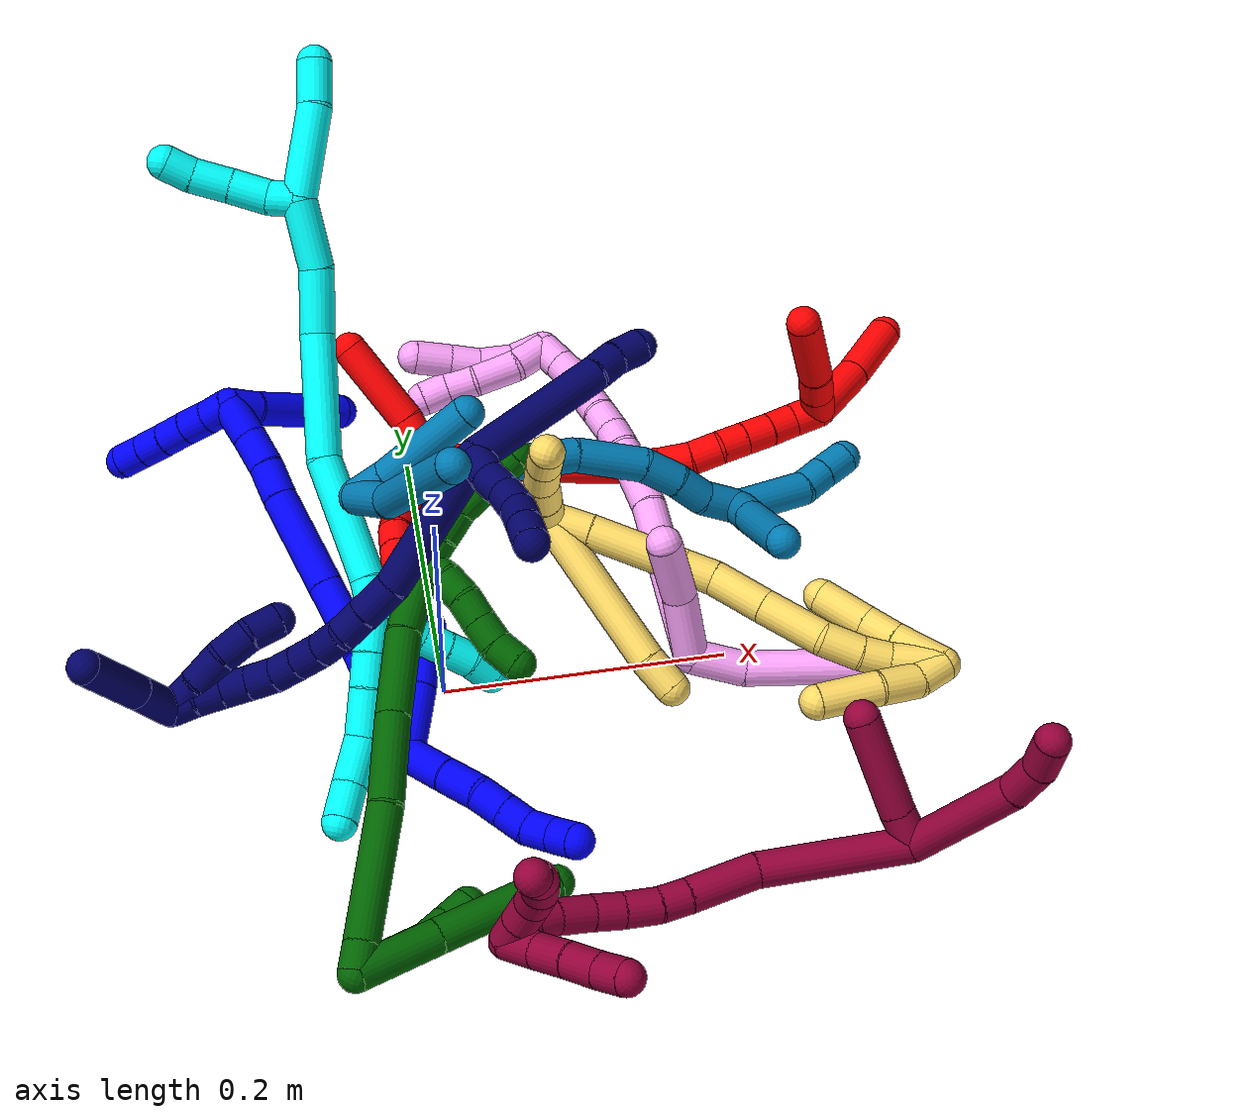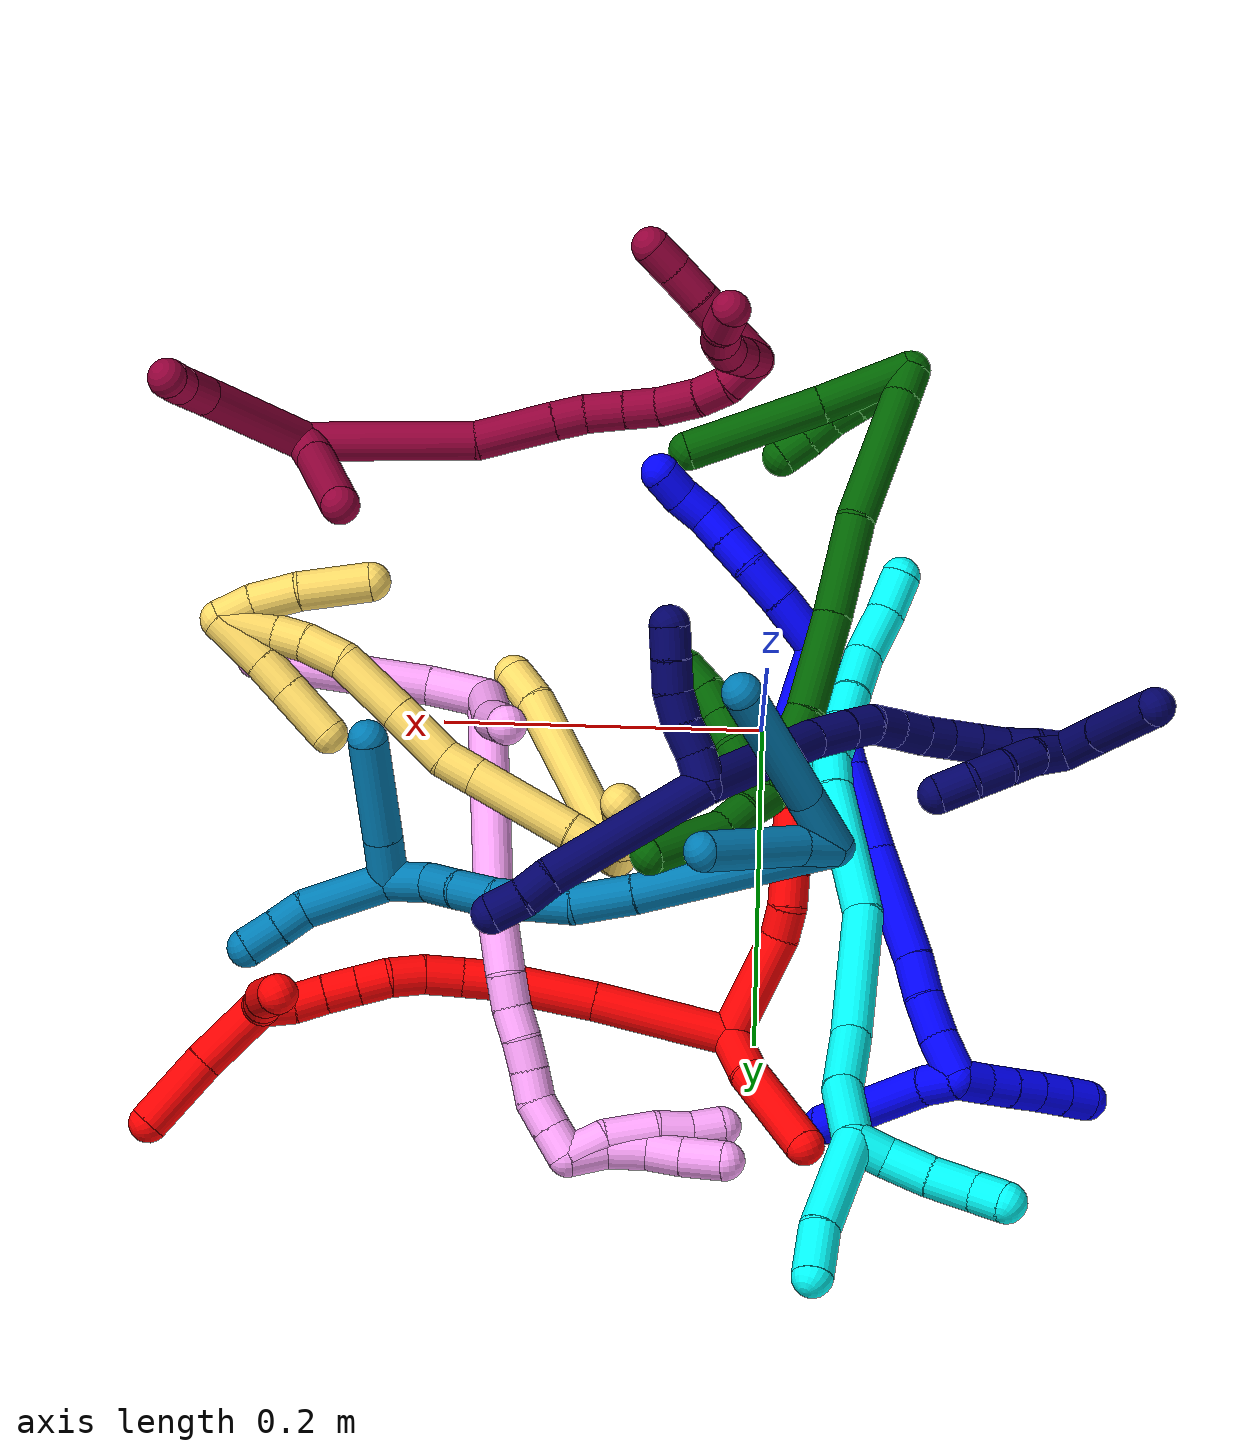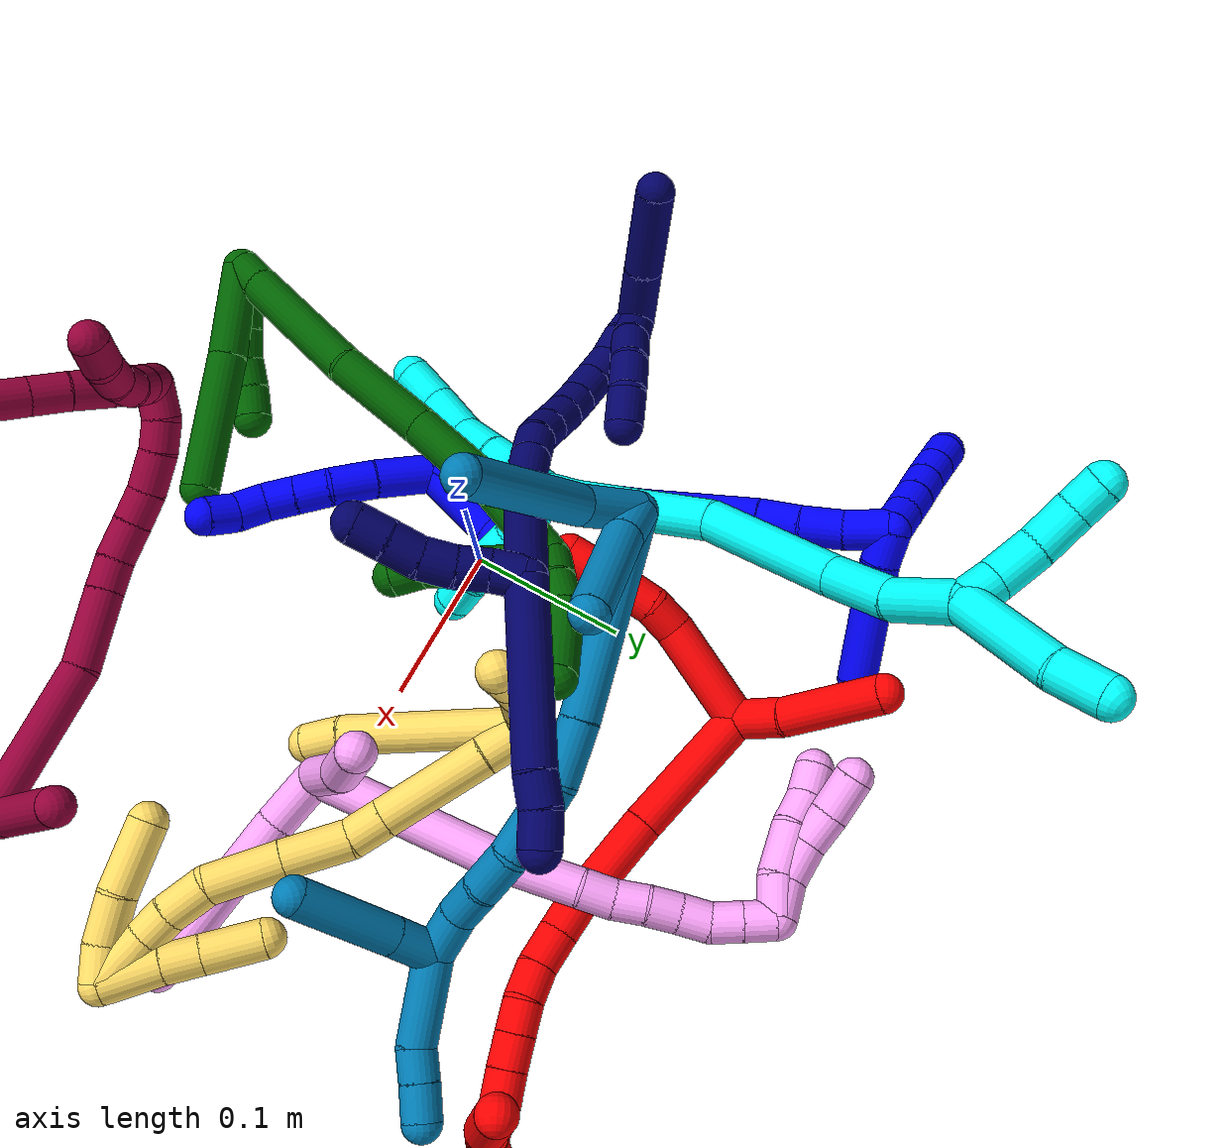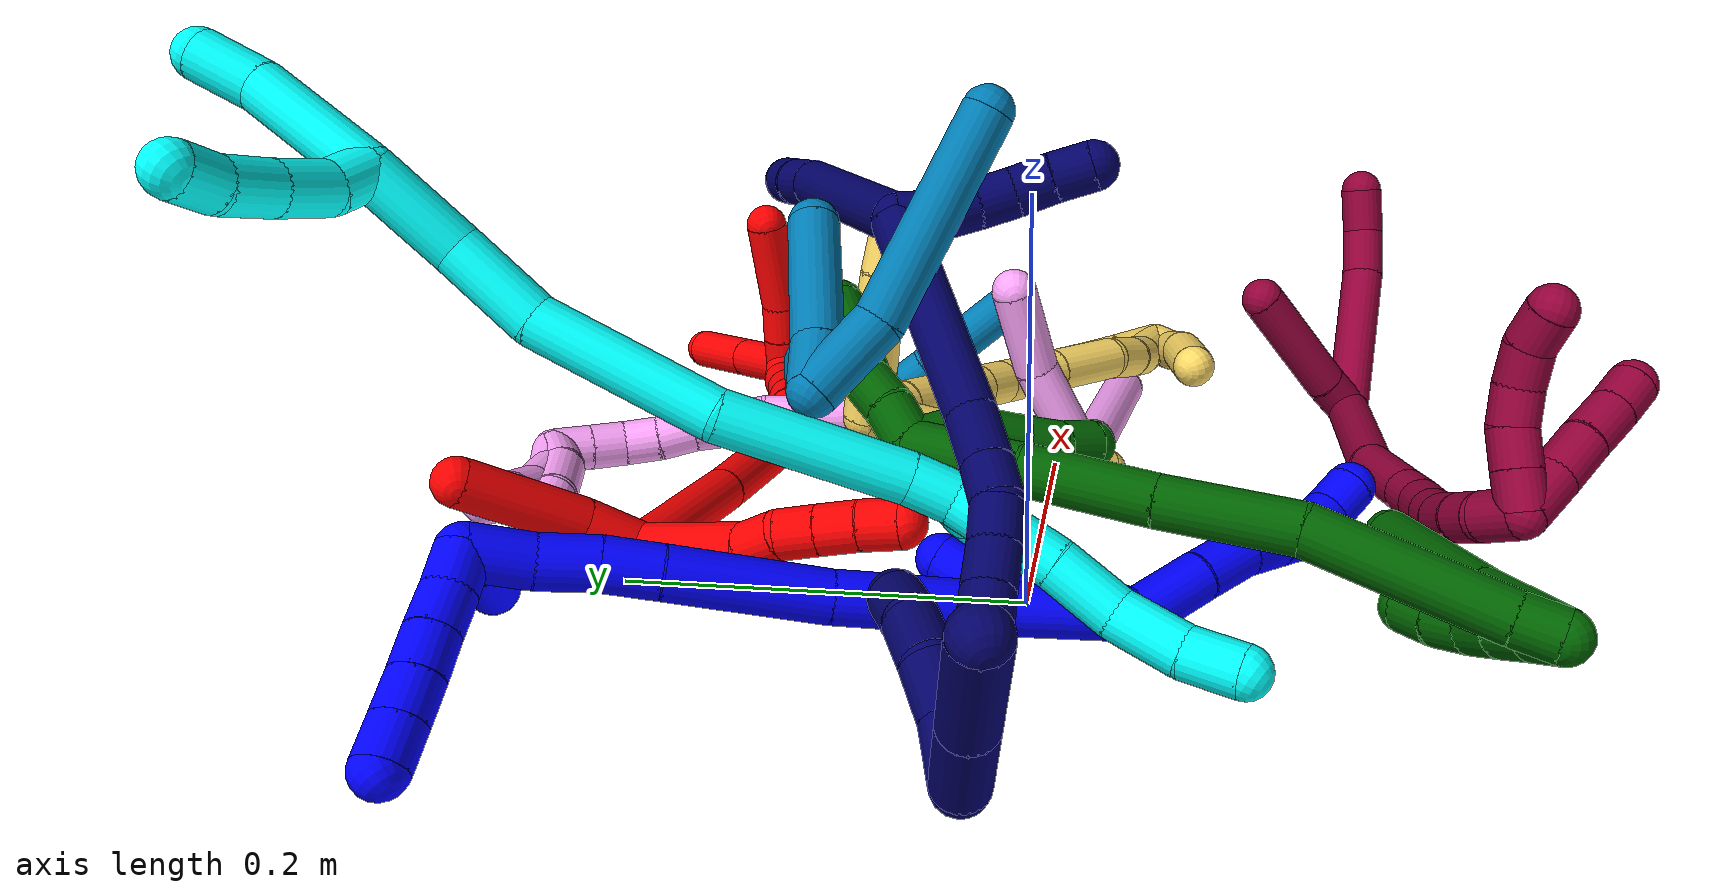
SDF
<sdf version="1.7">
 <world name="default">
  <plugin name="TubeGeneratorPlugin" filename="libtube_generator_plugin.so"/>
  <model name="photoneo_s_sensor">
   <static>1</static>
   <pose>0 0 2 1.57079 1.57079 3.14159</pose>
   <link name="link">
    <inertial><mass>0.1</mass></inertial>
    <sensor name="sensor" type="depth">
     <update_rate>30</update_rate>
     <camera>
      <horizontal_fov>1.22</horizontal_fov>
      <image><width>1920</width><height>1200</height><format>B8G8R8</format></image>
      <clip><near>0.1</near><far>4</far></clip>
      <depth_camera><output>points</output></depth_camera>
     </camera>
     <plugin name="camera_plugin" filename="libgazebo_ros_depth_camera.so">
      <baseline>0.2</baseline>
      <alwaysOn>1</alwaysOn>
      <updateRate>0.0</updateRate>
      <cameraName>camera_ir</cameraName>
      <imageTopicName>/camera/color/image_raw</imageTopicName>
      <cameraInfoTopicName>/camera/color/camera_info</cameraInfoTopicName>
      <depthImageTopicName>/camera/depth/image_raw</depthImageTopicName>
      <depthImageCameraInfoTopicName>/camera/depth/camera_info</depthImageCameraInfoTopicName>
      <pointCloudTopicName>/camera/depth/points</pointCloudTopicName>
      <frameName>fr_optical</frameName>
      <pointCloudCutoff>0.1</pointCloudCutoff>
      <pointCloudCutoffMax>2.0</pointCloudCutoffMax>
      <distortionK1>0</distortionK1>
      <distortionK2>0</distortionK2>
      <distortionK3>0</distortionK3>
      <distortionT1>0</distortionT1>
      <distortionT2>0</distortionT2>
      <CxPrime>0</CxPrime>
      <Cx>0</Cx>
      <Cy>0</Cy>
      <focalLength>0</focalLength>
      <hackBaseline>0</hackBaseline>
     </plugin>
    </sensor>
   </link>
  </model>
  <gravity>0 0 -9.8</gravity>
  <magnetic_field>6e-06 2.3e-05 -4.2e-05</magnetic_field>
  <atmosphere type="adiabatic"/>
  <physics name="default_physics" default="0" type="ode">
   <max_step_size>0.003</max_step_size>
   <real_time_factor>1</real_time_factor>
   <real_time_update_rate>1000</real_time_update_rate>
   <max_contacts>10000</max_contacts>
   <ode>
    <solver>
     <type>quick</type>
     <iters>100</iters>
     <sor>1.3</sor>
     <use_dynamic_moi_rescaling>0</use_dynamic_moi_rescaling>
    </solver>
    <constraints>
     <contact_max_correcting_vel>0</contact_max_correcting_vel>
     <contact_surface_layer>0.001</contact_surface_layer>
     <cfm>0</cfm>
     <erp>0.2</erp>
    </constraints>
   </ode>
  </physics>
  <scene><ambient>0.4 0.4 0.4 1</ambient><background>0.7 0.7 0.7 1</background><shadows>0</shadows></scene>
  <audio><device>default</device></audio>
  <spherical_coordinates>
   <surface_model>EARTH_WGS84</surface_model>
   <latitude_deg>0</latitude_deg>
   <longitude_deg>0</longitude_deg>
   <elevation>0</elevation>
   <heading_deg>0</heading_deg>
  </spherical_coordinates>
  <model name="bin">
   <static>1</static>
   <link name="bottom">
    <collision name="collision-bottom">
     <pose>0 0 -0.01 0 -0 0</pose>
     <geometry><box><size>0.8 0.6 0.02</size></box></geometry>
     <surface>
      <friction><ode><mu>100</mu><mu2>100</mu2></ode></friction>
      <contact><collide_bitmask>65535</collide_bitmask></contact>
     </surface>
    </collision>
   </link>
   <link name="west_wall">
    <collision name="collision-west_wall">
     <pose>-0.41 0 0.1 0 -0 0</pose>
     <geometry><box><size>0.02 0.6 0.2</size></box></geometry>
     <surface>
      <friction><ode><mu>100</mu><mu2>100</mu2></ode></friction>
      <contact><collide_bitmask>65535</collide_bitmask></contact>
     </surface>
    </collision>
   </link>
   <link name="east_wall">
    <collision name="collision-east_wall">
     <pose>0.41 0 0.1 0 -0 0</pose>
     <geometry><box><size>0.02 0.6 0.2</size></box></geometry>
     <surface>
      <friction><ode><mu>100</mu><mu2>100</mu2></ode></friction>
      <contact><collide_bitmask>65535</collide_bitmask></contact>
     </surface>
    </collision>
   </link>
   <link name="south_wall">
    <collision name="collision-south_wall">
     <pose>0 -0.31 0.1 0 -0 0</pose>
     <geometry><box><size>0.8 0.02 0.2</size></box></geometry>
     <surface>
      <friction><ode><mu>100</mu><mu2>100</mu2></ode></friction>
      <contact><collide_bitmask>65535</collide_bitmask></contact>
     </surface>
    </collision>
   </link>
   <link name="north_wall">
    <collision name="collision-north_wall">
     <pose>0 0.31 0.1 0 -0 0</pose>
     <geometry><box><size>0.8 0.02 0.2</size></box></geometry>
     <surface>
      <friction><ode><mu>100</mu><mu2>100</mu2></ode></friction>
      <contact><collide_bitmask>65535</collide_bitmask></contact>
     </surface>
    </collision>
   </link>
  </model>
  <model name="1">
   <static>0</static>
   <link name="1">
    <collision name="collision-cylinder-e_1_2_8">
     <pose>0.015125 -0.0118 -0.001164 1.6691 0.905895 0.985699</pose>
     <geometry><cylinder><radius>0.0125</radius><length>0.038438</length></cylinder></geometry>
     <surface>
      <friction><ode><mu>1.16</mu><mu2>1.16</mu2><slip1>0</slip1><slip2>0</slip2></ode></friction>
      <contact><ode><kp>1e+06</kp><kd>1</kd><max_vel>0</max_vel><min_depth>0.001</min_depth></ode></contact>
     </surface>
    </collision>
    <visual name="visual-cylinder-e_1_2_8">
     <pose>0.015125 -0.0118 -0.001164 1.6691 0.905895 0.985699</pose>
     <geometry><cylinder><radius>0.0125</radius><length>0.038438</length></cylinder></geometry>
     <material><ambient>0 0 1 1</ambient></material>
    </visual>
    <collision name="collision-cylinder-e_2_8_9">
     <pose>0.042337 -0.031429 -0.003347 1.70029 0.992233 1.10468</pose>
     <geometry><cylinder><radius>0.0125</radius><length>0.028874</length></cylinder></geometry>
     <surface>
      <friction><ode><mu>1.16</mu><mu2>1.16</mu2><slip1>0</slip1><slip2>0</slip2></ode></friction>
      <contact><ode><kp>1e+06</kp><kd>1</kd><max_vel>0</max_vel><min_depth>0.001</min_depth></ode></contact>
     </surface>
    </collision>
    <visual name="visual-cylinder-e_2_8_9">
     <pose>0.042337 -0.031429 -0.003347 1.70029 0.992233 1.10468</pose>
     <geometry><cylinder><radius>0.0125</radius><length>0.028874</length></cylinder></geometry>
     <material><ambient>0 0 1 1</ambient></material>
    </visual>
    <collision name="collision-cylinder-e_3_9_10">
     <pose>0.064183 -0.043684 -0.006765 2.06738 1.09453 1.59378</pose>
     <geometry><cylinder><radius>0.0125</radius><length>0.021961</length></cylinder></geometry>
     <surface>
      <friction><ode><mu>1.16</mu><mu2>1.16</mu2><slip1>0</slip1><slip2>0</slip2></ode></friction>
      <contact><ode><kp>1e+06</kp><kd>1</kd><max_vel>0</max_vel><min_depth>0.001</min_depth></ode></contact>
     </surface>
    </collision>
    <visual name="visual-cylinder-e_3_9_10">
     <pose>0.064183 -0.043684 -0.006765 2.06738 1.09453 1.59378</pose>
     <geometry><cylinder><radius>0.0125</radius><length>0.021961</length></cylinder></geometry>
     <material><ambient>0 0 1 1</ambient></material>
    </visual>
    <collision name="collision-cylinder-e_4_10_11">
     <pose>0.082854 -0.052142 -0.011391 2.07566 1.09373 1.60231</pose>
     <geometry><cylinder><radius>0.0125</radius><length>0.020065</length></cylinder></geometry>
     <surface>
      <friction><ode><mu>1.16</mu><mu2>1.16</mu2><slip1>0</slip1><slip2>0</slip2></ode></friction>
      <contact><ode><kp>1e+06</kp><kd>1</kd><max_vel>0</max_vel><min_depth>0.001</min_depth></ode></contact>
     </surface>
    </collision>
    <visual name="visual-cylinder-e_4_10_11">
     <pose>0.082854 -0.052142 -0.011391 2.07566 1.09373 1.60231</pose>
     <geometry><cylinder><radius>0.0125</radius><length>0.020065</length></cylinder></geometry>
     <material><ambient>0 0 1 1</ambient></material>
    </visual>
    <collision name="collision-cylinder-e_5_11_12">
     <pose>0.100702 -0.060924 -0.012621 1.36367 1.07322 0.899622</pose>
     <geometry><cylinder><radius>0.0125</radius><length>0.020339</length></cylinder></geometry>
     <surface>
      <friction><ode><mu>1.16</mu><mu2>1.16</mu2><slip1>0</slip1><slip2>0</slip2></ode></friction>
      <contact><ode><kp>1e+06</kp><kd>1</kd><max_vel>0</max_vel><min_depth>0.001</min_depth></ode></contact>
     </surface>
    </collision>
    <visual name="visual-cylinder-e_5_11_12">
     <pose>0.100702 -0.060924 -0.012621 1.36367 1.07322 0.899622</pose>
     <geometry><cylinder><radius>0.0125</radius><length>0.020339</length></cylinder></geometry>
     <material><ambient>0 0 1 1</ambient></material>
    </visual>
    <collision name="collision-cylinder-e_6_12_6">
     <pose>0.116811 -0.072673 -0.009943 1.33521 0.783629 0.629794</pose>
     <geometry><cylinder><radius>0.0125</radius><length>0.020324</length></cylinder></geometry>
     <surface>
      <friction><ode><mu>1.16</mu><mu2>1.16</mu2><slip1>0</slip1><slip2>0</slip2></ode></friction>
      <contact><ode><kp>1e+06</kp><kd>1</kd><max_vel>0</max_vel><min_depth>0.001</min_depth></ode></contact>
     </surface>
    </collision>
    <visual name="visual-cylinder-e_6_12_6">
     <pose>0.116811 -0.072673 -0.009943 1.33521 0.783629 0.629794</pose>
     <geometry><cylinder><radius>0.0125</radius><length>0.020324</length></cylinder></geometry>
     <material><ambient>0 0 1 1</ambient></material>
    </visual>
    <collision name="collision-cylinder-e_1_2_13">
     <pose>-0.002511 0.017706 0.019651 -0.733371 -0.094634 0.036368</pose>
     <geometry><cylinder><radius>0.0125</radius><length>0.05314</length></cylinder></geometry>
     <surface>
      <friction><ode><mu>1.16</mu><mu2>1.16</mu2><slip1>0</slip1><slip2>0</slip2></ode></friction>
      <contact><ode><kp>1e+06</kp><kd>1</kd><max_vel>0</max_vel><min_depth>0.001</min_depth></ode></contact>
     </surface>
    </collision>
    <visual name="visual-cylinder-e_1_2_13">
     <pose>-0.002511 0.017706 0.019651 -0.733371 -0.094634 0.036368</pose>
     <geometry><cylinder><radius>0.0125</radius><length>0.05314</length></cylinder></geometry>
     <material><ambient>0 0 1 1</ambient></material>
    </visual>
    <collision name="collision-cylinder-e_2_13_14">
     <pose>-0.007325 0.041914 0.050066 -0.54341 -0.181168 0.0506</pose>
     <geometry><cylinder><radius>0.0125</radius><length>0.02557</length></cylinder></geometry>
     <surface>
      <friction><ode><mu>1.16</mu><mu2>1.16</mu2><slip1>0</slip1><slip2>0</slip2></ode></friction>
      <contact><ode><kp>1e+06</kp><kd>1</kd><max_vel>0</max_vel><min_depth>0.001</min_depth></ode></contact>
     </surface>
    </collision>
    <visual name="visual-cylinder-e_2_13_14">
     <pose>-0.007325 0.041914 0.050066 -0.54341 -0.181168 0.0506</pose>
     <geometry><cylinder><radius>0.0125</radius><length>0.02557</length></cylinder></geometry>
     <material><ambient>0 0 1 1</ambient></material>
    </visual>
    <collision name="collision-cylinder-e_3_14_5">
     <pose>-0.010472 0.052167 0.070757 -0.361241 -0.07935 0.014497</pose>
     <geometry><cylinder><radius>0.0125</radius><length>0.02129</length></cylinder></geometry>
     <surface>
      <friction><ode><mu>1.16</mu><mu2>1.16</mu2><slip1>0</slip1><slip2>0</slip2></ode></friction>
      <contact><ode><kp>1e+06</kp><kd>1</kd><max_vel>0</max_vel><min_depth>0.001</min_depth></ode></contact>
     </surface>
    </collision>
    <visual name="visual-cylinder-e_3_14_5">
     <pose>-0.010472 0.052167 0.070757 -0.361241 -0.07935 0.014497</pose>
     <geometry><cylinder><radius>0.0125</radius><length>0.02129</length></cylinder></geometry>
     <material><ambient>0 0 1 1</ambient></material>
    </visual>
    <collision name="collision-cylinder-e_1_2_15">
     <pose>-0.025403 0.02142 0.024931 -0.709796 -0.657975 0.251696</pose>
     <geometry><cylinder><radius>0.0125</radius><length>0.083083</length></cylinder></geometry>
     <surface>
      <friction><ode><mu>1.16</mu><mu2>1.16</mu2><slip1>0</slip1><slip2>0</slip2></ode></friction>
      <contact><ode><kp>1e+06</kp><kd>1</kd><max_vel>0</max_vel><min_depth>0.001</min_depth></ode></contact>
     </surface>
    </collision>
    <visual name="visual-cylinder-e_1_2_15">
     <pose>-0.025403 0.02142 0.024931 -0.709796 -0.657975 0.251696</pose>
     <geometry><cylinder><radius>0.0125</radius><length>0.083083</length></cylinder></geometry>
     <material><ambient>0 0 1 1</ambient></material>
    </visual>
    <collision name="collision-cylinder-e_2_15_16">
     <pose>-0.070118 0.056251 0.067304 -0.655486 -0.720365 0.254713</pose>
     <geometry><cylinder><radius>0.0125</radius><length>0.058549</length></cylinder></geometry>
     <surface>
      <friction><ode><mu>1.16</mu><mu2>1.16</mu2><slip1>0</slip1><slip2>0</slip2></ode></friction>
      <contact><ode><kp>1e+06</kp><kd>1</kd><max_vel>0</max_vel><min_depth>0.001</min_depth></ode></contact>
     </surface>
    </collision>
    <visual name="visual-cylinder-e_2_15_16">
     <pose>-0.070118 0.056251 0.067304 -0.655486 -0.720365 0.254713</pose>
     <geometry><cylinder><radius>0.0125</radius><length>0.058549</length></cylinder></geometry>
     <material><ambient>0 0 1 1</ambient></material>
    </visual>
    <collision name="collision-cylinder-e_3_16_17">
     <pose>-0.114724 0.083919 0.108255 -0.545144 -0.743756 0.217189</pose>
     <geometry><cylinder><radius>0.0125</radius><length>0.074719</length></cylinder></geometry>
     <surface>
      <friction><ode><mu>1.16</mu><mu2>1.16</mu2><slip1>0</slip1><slip2>0</slip2></ode></friction>
      <contact><ode><kp>1e+06</kp><kd>1</kd><max_vel>0</max_vel><min_depth>0.001</min_depth></ode></contact>
     </surface>
    </collision>
    <visual name="visual-cylinder-e_3_16_17">
     <pose>-0.114724 0.083919 0.108255 -0.545144 -0.743756 0.217189</pose>
     <geometry><cylinder><radius>0.0125</radius><length>0.074719</length></cylinder></geometry>
     <material><ambient>0 0 1 1</ambient></material>
    </visual>
    <collision name="collision-cylinder-e_4_17_18">
     <pose>-0.148169 0.103928 0.140428 -0.586034 -0.664746 0.207534</pose>
     <geometry><cylinder><radius>0.0125</radius><length>0.026428</length></cylinder></geometry>
     <surface>
      <friction><ode><mu>1.16</mu><mu2>1.16</mu2><slip1>0</slip1><slip2>0</slip2></ode></friction>
      <contact><ode><kp>1e+06</kp><kd>1</kd><max_vel>0</max_vel><min_depth>0.001</min_depth></ode></contact>
     </surface>
    </collision>
    <visual name="visual-cylinder-e_4_17_18">
     <pose>-0.148169 0.103928 0.140428 -0.586034 -0.664746 0.207534</pose>
     <geometry><cylinder><radius>0.0125</radius><length>0.026428</length></cylinder></geometry>
     <material><ambient>0 0 1 1</ambient></material>
    </visual>
    <collision name="collision-cylinder-e_5_18_19">
     <pose>-0.165715 0.116268 0.156832 -0.705285 -0.746144 0.286124</pose>
     <geometry><cylinder><radius>0.0125</radius><length>0.02768</length></cylinder></geometry>
     <surface>
      <friction><ode><mu>1.16</mu><mu2>1.16</mu2><slip1>0</slip1><slip2>0</slip2></ode></friction>
      <contact><ode><kp>1e+06</kp><kd>1</kd><max_vel>0</max_vel><min_depth>0.001</min_depth></ode></contact>
     </surface>
    </collision>
    <visual name="visual-cylinder-e_5_18_19">
     <pose>-0.165715 0.116268 0.156832 -0.705285 -0.746144 0.286124</pose>
     <geometry><cylinder><radius>0.0125</radius><length>0.02768</length></cylinder></geometry>
     <material><ambient>0 0 1 1</ambient></material>
    </visual>
    <collision name="collision-cylinder-e_6_19_1">
     <pose>-0.18607 0.127523 0.173303 -0.4908 -0.836124 0.221611</pose>
     <geometry><cylinder><radius>0.0125</radius><length>0.02954</length></cylinder></geometry>
     <surface>
      <friction><ode><mu>1.16</mu><mu2>1.16</mu2><slip1>0</slip1><slip2>0</slip2></ode></friction>
      <contact><ode><kp>1e+06</kp><kd>1</kd><max_vel>0</max_vel><min_depth>0.001</min_depth></ode></contact>
     </surface>
    </collision>
    <visual name="visual-cylinder-e_6_19_1">
     <pose>-0.18607 0.127523 0.173303 -0.4908 -0.836124 0.221611</pose>
     <geometry><cylinder><radius>0.0125</radius><length>0.02954</length></cylinder></geometry>
     <material><ambient>0 0 1 1</ambient></material>
    </visual>
    <collision name="collision-cylinder-e_1_1_20">
     <pose>-0.203193 0.136105 0.175202 -2.62124 -0.66393 1.82642</pose>
     <geometry><cylinder><radius>0.0125</radius><length>0.02</length></cylinder></geometry>
     <surface>
      <friction><ode><mu>1.16</mu><mu2>1.16</mu2><slip1>0</slip1><slip2>0</slip2></ode></friction>
      <contact><ode><kp>1e+06</kp><kd>1</kd><max_vel>0</max_vel><min_depth>0.001</min_depth></ode></contact>
     </surface>
    </collision>
    <visual name="visual-cylinder-e_1_1_20">
     <pose>-0.203193 0.136105 0.175202 -2.62124 -0.66393 1.82642</pose>
     <geometry><cylinder><radius>0.0125</radius><length>0.02</length></cylinder></geometry>
     <material><ambient>0 0 1 1</ambient></material>
    </visual>
    <collision name="collision-cylinder-e_2_20_21">
     <pose>-0.216117 0.143416 0.16183 -2.66266 -0.742594 2.02143</pose>
     <geometry><cylinder><radius>0.0125</radius><length>0.02</length></cylinder></geometry>
     <surface>
      <friction><ode><mu>1.16</mu><mu2>1.16</mu2><slip1>0</slip1><slip2>0</slip2></ode></friction>
      <contact><ode><kp>1e+06</kp><kd>1</kd><max_vel>0</max_vel><min_depth>0.001</min_depth></ode></contact>
     </surface>
    </collision>
    <visual name="visual-cylinder-e_2_20_21">
     <pose>-0.216117 0.143416 0.16183 -2.66266 -0.742594 2.02143</pose>
     <geometry><cylinder><radius>0.0125</radius><length>0.02</length></cylinder></geometry>
     <material><ambient>0 0 1 1</ambient></material>
    </visual>
    <collision name="collision-cylinder-e_3_21_22">
     <pose>-0.229385 0.150255 0.148523 -2.67099 -0.708335 1.99113</pose>
     <geometry><cylinder><radius>0.0125</radius><length>0.02</length></cylinder></geometry>
     <surface>
      <friction><ode><mu>1.16</mu><mu2>1.16</mu2><slip1>0</slip1><slip2>0</slip2></ode></friction>
      <contact><ode><kp>1e+06</kp><kd>1</kd><max_vel>0</max_vel><min_depth>0.001</min_depth></ode></contact>
     </surface>
    </collision>
    <visual name="visual-cylinder-e_3_21_22">
     <pose>-0.229385 0.150255 0.148523 -2.67099 -0.708335 1.99113</pose>
     <geometry><cylinder><radius>0.0125</radius><length>0.02</length></cylinder></geometry>
     <material><ambient>0 0 1 1</ambient></material>
    </visual>
    <collision name="collision-cylinder-e_4_22_23">
     <pose>-0.242464 0.157373 0.135174 -2.63221 -0.717268 1.92748</pose>
     <geometry><cylinder><radius>0.0125</radius><length>0.02</length></cylinder></geometry>
     <surface>
      <friction><ode><mu>1.16</mu><mu2>1.16</mu2><slip1>0</slip1><slip2>0</slip2></ode></friction>
      <contact><ode><kp>1e+06</kp><kd>1</kd><max_vel>0</max_vel><min_depth>0.001</min_depth></ode></contact>
     </surface>
    </collision>
    <visual name="visual-cylinder-e_4_22_23">
     <pose>-0.242464 0.157373 0.135174 -2.63221 -0.717268 1.92748</pose>
     <geometry><cylinder><radius>0.0125</radius><length>0.02</length></cylinder></geometry>
     <material><ambient>0 0 1 1</ambient></material>
    </visual>
    <collision name="collision-cylinder-e_5_23_4">
     <pose>-0.255638 0.164769 0.12207 -2.62327 -0.720957 1.91567</pose>
     <geometry><cylinder><radius>0.0125</radius><length>0.02</length></cylinder></geometry>
     <surface>
      <friction><ode><mu>1.16</mu><mu2>1.16</mu2><slip1>0</slip1><slip2>0</slip2></ode></friction>
      <contact><ode><kp>1e+06</kp><kd>1</kd><max_vel>0</max_vel><min_depth>0.001</min_depth></ode></contact>
     </surface>
    </collision>
    <visual name="visual-cylinder-e_5_23_4">
     <pose>-0.255638 0.164769 0.12207 -2.62327 -0.720957 1.91567</pose>
     <geometry><cylinder><radius>0.0125</radius><length>0.02</length></cylinder></geometry>
     <material><ambient>0 0 1 1</ambient></material>
    </visual>
    <collision name="collision-cylinder-e_1_1_24">
     <pose>-0.187624 0.138455 0.183212 -1.38506 0.975191 -0.828911</pose>
     <geometry><cylinder><radius>0.0125</radius><length>0.022727</length></cylinder></geometry>
     <surface>
      <friction><ode><mu>1.16</mu><mu2>1.16</mu2><slip1>0</slip1><slip2>0</slip2></ode></friction>
      <contact><ode><kp>1e+06</kp><kd>1</kd><max_vel>0</max_vel><min_depth>0.001</min_depth></ode></contact>
     </surface>
    </collision>
    <visual name="visual-cylinder-e_1_1_24">
     <pose>-0.187624 0.138455 0.183212 -1.38506 0.975191 -0.828911</pose>
     <geometry><cylinder><radius>0.0125</radius><length>0.022727</length></cylinder></geometry>
     <material><ambient>0 0 1 1</ambient></material>
    </visual>
    <collision name="collision-cylinder-e_2_24_3">
     <pose>-0.149869 0.170231 0.190587 -1.33249 0.823748 -0.66164</pose>
     <geometry><cylinder><radius>0.0125</radius><length>0.077273</length></cylinder></geometry>
     <surface>
      <friction><ode><mu>1.16</mu><mu2>1.16</mu2><slip1>0</slip1><slip2>0</slip2></ode></friction>
      <contact><ode><kp>1e+06</kp><kd>1</kd><max_vel>0</max_vel><min_depth>0.001</min_depth></ode></contact>
     </surface>
    </collision>
    <visual name="visual-cylinder-e_2_24_3">
     <pose>-0.149869 0.170231 0.190587 -1.33249 0.823748 -0.66164</pose>
     <geometry><cylinder><radius>0.0125</radius><length>0.077273</length></cylinder></geometry>
     <material><ambient>0 0 1 1</ambient></material>
    </visual>
    <collision name="collision-sphere-3">
     <pose>-0.121522 0.195742 0.196784 0 -0 0</pose>
     <geometry><sphere><radius>0.0125</radius></sphere></geometry>
     <surface>
      <friction><ode><mu>1.16</mu><mu2>1.16</mu2><slip1>0</slip1><slip2>0</slip2></ode></friction>
      <contact><ode><kp>1e+06</kp><kd>1</kd><max_vel>0</max_vel><min_depth>0.001</min_depth></ode></contact>
     </surface>
    </collision>
    <visual name="visual-sphere-3">
     <pose>-0.121522 0.195742 0.196784 0 -0 0</pose>
     <geometry><sphere><radius>0.0125</radius></sphere></geometry>
     <material><ambient>0 0 1 1</ambient></material>
    </visual>
    <collision name="collision-sphere-24">
     <pose>-0.178217 0.144721 0.184389 0 -0 0</pose>
     <geometry><sphere><radius>0.0125</radius></sphere></geometry>
     <surface>
      <friction><ode><mu>1.16</mu><mu2>1.16</mu2><slip1>0</slip1><slip2>0</slip2></ode></friction>
      <contact><ode><kp>1e+06</kp><kd>1</kd><max_vel>0</max_vel><min_depth>0.001</min_depth></ode></contact>
     </surface>
    </collision>
    <visual name="visual-sphere-24">
     <pose>-0.178217 0.144721 0.184389 0 -0 0</pose>
     <geometry><sphere><radius>0.0125</radius></sphere></geometry>
     <material><ambient>0 0 1 1</ambient></material>
    </visual>
    <collision name="collision-sphere-4">
     <pose>-0.262239 0.168491 0.115545 0 -0 0</pose>
     <geometry><sphere><radius>0.0125</radius></sphere></geometry>
     <surface>
      <friction><ode><mu>1.16</mu><mu2>1.16</mu2><slip1>0</slip1><slip2>0</slip2></ode></friction>
      <contact><ode><kp>1e+06</kp><kd>1</kd><max_vel>0</max_vel><min_depth>0.001</min_depth></ode></contact>
     </surface>
    </collision>
    <visual name="visual-sphere-4">
     <pose>-0.262239 0.168491 0.115545 0 -0 0</pose>
     <geometry><sphere><radius>0.0125</radius></sphere></geometry>
     <material><ambient>0 0 1 1</ambient></material>
    </visual>
    <collision name="collision-sphere-23">
     <pose>-0.249037 0.161048 0.128595 0 -0 0</pose>
     <geometry><sphere><radius>0.0125</radius></sphere></geometry>
     <surface>
      <friction><ode><mu>1.16</mu><mu2>1.16</mu2><slip1>0</slip1><slip2>0</slip2></ode></friction>
      <contact><ode><kp>1e+06</kp><kd>1</kd><max_vel>0</max_vel><min_depth>0.001</min_depth></ode></contact>
     </surface>
    </collision>
    <visual name="visual-sphere-23">
     <pose>-0.249037 0.161048 0.128595 0 -0 0</pose>
     <geometry><sphere><radius>0.0125</radius></sphere></geometry>
     <material><ambient>0 0 1 1</ambient></material>
    </visual>
    <collision name="collision-sphere-22">
     <pose>-0.23589 0.153698 0.141754 0 -0 0</pose>
     <geometry><sphere><radius>0.0125</radius></sphere></geometry>
     <surface>
      <friction><ode><mu>1.16</mu><mu2>1.16</mu2><slip1>0</slip1><slip2>0</slip2></ode></friction>
      <contact><ode><kp>1e+06</kp><kd>1</kd><max_vel>0</max_vel><min_depth>0.001</min_depth></ode></contact>
     </surface>
    </collision>
    <visual name="visual-sphere-22">
     <pose>-0.23589 0.153698 0.141754 0 -0 0</pose>
     <geometry><sphere><radius>0.0125</radius></sphere></geometry>
     <material><ambient>0 0 1 1</ambient></material>
    </visual>
    <collision name="collision-sphere-21">
     <pose>-0.222879 0.146811 0.155292 0 -0 0</pose>
     <geometry><sphere><radius>0.0125</radius></sphere></geometry>
     <surface>
      <friction><ode><mu>1.16</mu><mu2>1.16</mu2><slip1>0</slip1><slip2>0</slip2></ode></friction>
      <contact><ode><kp>1e+06</kp><kd>1</kd><max_vel>0</max_vel><min_depth>0.001</min_depth></ode></contact>
     </surface>
    </collision>
    <visual name="visual-sphere-21">
     <pose>-0.222879 0.146811 0.155292 0 -0 0</pose>
     <geometry><sphere><radius>0.0125</radius></sphere></geometry>
     <material><ambient>0 0 1 1</ambient></material>
    </visual>
    <collision name="collision-sphere-20">
     <pose>-0.209355 0.140021 0.168368 0 -0 0</pose>
     <geometry><sphere><radius>0.0125</radius></sphere></geometry>
     <surface>
      <friction><ode><mu>1.16</mu><mu2>1.16</mu2><slip1>0</slip1><slip2>0</slip2></ode></friction>
      <contact><ode><kp>1e+06</kp><kd>1</kd><max_vel>0</max_vel><min_depth>0.001</min_depth></ode></contact>
     </surface>
    </collision>
    <visual name="visual-sphere-20">
     <pose>-0.209355 0.140021 0.168368 0 -0 0</pose>
     <geometry><sphere><radius>0.0125</radius></sphere></geometry>
     <material><ambient>0 0 1 1</ambient></material>
    </visual>
    <collision name="collision-sphere-12">
     <pose>0.109639 -0.065674 -0.011623 0 -0 0</pose>
     <geometry><sphere><radius>0.0125</radius></sphere></geometry>
     <surface>
      <friction><ode><mu>1.16</mu><mu2>1.16</mu2><slip1>0</slip1><slip2>0</slip2></ode></friction>
      <contact><ode><kp>1e+06</kp><kd>1</kd><max_vel>0</max_vel><min_depth>0.001</min_depth></ode></contact>
     </surface>
    </collision>
    <visual name="visual-sphere-12">
     <pose>0.109639 -0.065674 -0.011623 0 -0 0</pose>
     <geometry><sphere><radius>0.0125</radius></sphere></geometry>
     <material><ambient>0 0 1 1</ambient></material>
    </visual>
    <collision name="collision-sphere-11">
     <pose>0.091766 -0.056174 -0.01362 0 -0 0</pose>
     <geometry><sphere><radius>0.0125</radius></sphere></geometry>
     <surface>
      <friction><ode><mu>1.16</mu><mu2>1.16</mu2><slip1>0</slip1><slip2>0</slip2></ode></friction>
      <contact><ode><kp>1e+06</kp><kd>1</kd><max_vel>0</max_vel><min_depth>0.001</min_depth></ode></contact>
     </surface>
    </collision>
    <visual name="visual-sphere-11">
     <pose>0.091766 -0.056174 -0.01362 0 -0 0</pose>
     <geometry><sphere><radius>0.0125</radius></sphere></geometry>
     <material><ambient>0 0 1 1</ambient></material>
    </visual>
    <collision name="collision-sphere-10">
     <pose>0.073941 -0.04811 -0.009163 0 -0 0</pose>
     <geometry><sphere><radius>0.0125</radius></sphere></geometry>
     <surface>
      <friction><ode><mu>1.16</mu><mu2>1.16</mu2><slip1>0</slip1><slip2>0</slip2></ode></friction>
      <contact><ode><kp>1e+06</kp><kd>1</kd><max_vel>0</max_vel><min_depth>0.001</min_depth></ode></contact>
     </surface>
    </collision>
    <visual name="visual-sphere-10">
     <pose>0.073941 -0.04811 -0.009163 0 -0 0</pose>
     <geometry><sphere><radius>0.0125</radius></sphere></geometry>
     <material><ambient>0 0 1 1</ambient></material>
    </visual>
    <collision name="collision-sphere-9">
     <pose>0.054424 -0.039257 -0.004366 0 -0 0</pose>
     <geometry><sphere><radius>0.0125</radius></sphere></geometry>
     <surface>
      <friction><ode><mu>1.16</mu><mu2>1.16</mu2><slip1>0</slip1><slip2>0</slip2></ode></friction>
      <contact><ode><kp>1e+06</kp><kd>1</kd><max_vel>0</max_vel><min_depth>0.001</min_depth></ode></contact>
     </surface>
    </collision>
    <visual name="visual-sphere-9">
     <pose>0.054424 -0.039257 -0.004366 0 -0 0</pose>
     <geometry><sphere><radius>0.0125</radius></sphere></geometry>
     <material><ambient>0 0 1 1</ambient></material>
    </visual>
    <collision name="collision-sphere-2">
     <geometry><sphere><radius>0.0125</radius></sphere></geometry>
     <surface>
      <friction><ode><mu>1.16</mu><mu2>1.16</mu2><slip1>0</slip1><slip2>0</slip2></ode></friction>
      <contact><ode><kp>1e+06</kp><kd>1</kd><max_vel>0</max_vel><min_depth>0.001</min_depth></ode></contact>
     </surface>
    </collision>
    <visual name="visual-sphere-2">
     <geometry><sphere><radius>0.0125</radius></sphere></geometry>
     <material><ambient>0 0 1 1</ambient></material>
    </visual>
    <collision name="collision-sphere-19">
     <pose>-0.17511 0.122856 0.16457 0 -0 0</pose>
     <geometry><sphere><radius>0.0125</radius></sphere></geometry>
     <surface>
      <friction><ode><mu>1.16</mu><mu2>1.16</mu2><slip1>0</slip1><slip2>0</slip2></ode></friction>
      <contact><ode><kp>1e+06</kp><kd>1</kd><max_vel>0</max_vel><min_depth>0.001</min_depth></ode></contact>
     </surface>
    </collision>
    <visual name="visual-sphere-19">
     <pose>-0.17511 0.122856 0.16457 0 -0 0</pose>
     <geometry><sphere><radius>0.0125</radius></sphere></geometry>
     <material><ambient>0 0 1 1</ambient></material>
    </visual>
    <collision name="collision-sphere-8">
     <pose>0.03025 -0.023601 -0.002327 0 -0 0</pose>
     <geometry><sphere><radius>0.0125</radius></sphere></geometry>
     <surface>
      <friction><ode><mu>1.16</mu><mu2>1.16</mu2><slip1>0</slip1><slip2>0</slip2></ode></friction>
      <contact><ode><kp>1e+06</kp><kd>1</kd><max_vel>0</max_vel><min_depth>0.001</min_depth></ode></contact>
     </surface>
    </collision>
    <visual name="visual-sphere-8">
     <pose>0.03025 -0.023601 -0.002327 0 -0 0</pose>
     <geometry><sphere><radius>0.0125</radius></sphere></geometry>
     <material><ambient>0 0 1 1</ambient></material>
    </visual>
    <collision name="collision-sphere-6">
     <pose>0.123984 -0.079673 -0.008263 0 -0 0</pose>
     <geometry><sphere><radius>0.0125</radius></sphere></geometry>
     <surface>
      <friction><ode><mu>1.16</mu><mu2>1.16</mu2><slip1>0</slip1><slip2>0</slip2></ode></friction>
      <contact><ode><kp>1e+06</kp><kd>1</kd><max_vel>0</max_vel><min_depth>0.001</min_depth></ode></contact>
     </surface>
    </collision>
    <visual name="visual-sphere-6">
     <pose>0.123984 -0.079673 -0.008263 0 -0 0</pose>
     <geometry><sphere><radius>0.0125</radius></sphere></geometry>
     <material><ambient>0 0 1 1</ambient></material>
    </visual>
    <collision name="collision-sphere-13">
     <pose>-0.005021 0.035412 0.039302 0 -0 0</pose>
     <geometry><sphere><radius>0.0125</radius></sphere></geometry>
     <surface>
      <friction><ode><mu>1.16</mu><mu2>1.16</mu2><slip1>0</slip1><slip2>0</slip2></ode></friction>
      <contact><ode><kp>1e+06</kp><kd>1</kd><max_vel>0</max_vel><min_depth>0.001</min_depth></ode></contact>
     </surface>
    </collision>
    <visual name="visual-sphere-13">
     <pose>-0.005021 0.035412 0.039302 0 -0 0</pose>
     <geometry><sphere><radius>0.0125</radius></sphere></geometry>
     <material><ambient>0 0 1 1</ambient></material>
    </visual>
    <collision name="collision-sphere-14">
     <pose>-0.009628 0.048416 0.06083 0 -0 0</pose>
     <geometry><sphere><radius>0.0125</radius></sphere></geometry>
     <surface>
      <friction><ode><mu>1.16</mu><mu2>1.16</mu2><slip1>0</slip1><slip2>0</slip2></ode></friction>
      <contact><ode><kp>1e+06</kp><kd>1</kd><max_vel>0</max_vel><min_depth>0.001</min_depth></ode></contact>
     </surface>
    </collision>
    <visual name="visual-sphere-14">
     <pose>-0.009628 0.048416 0.06083 0 -0 0</pose>
     <geometry><sphere><radius>0.0125</radius></sphere></geometry>
     <material><ambient>0 0 1 1</ambient></material>
    </visual>
    <collision name="collision-sphere-5">
     <pose>-0.011316 0.055917 0.080684 0 -0 0</pose>
     <geometry><sphere><radius>0.0125</radius></sphere></geometry>
     <surface>
      <friction><ode><mu>1.16</mu><mu2>1.16</mu2><slip1>0</slip1><slip2>0</slip2></ode></friction>
      <contact><ode><kp>1e+06</kp><kd>1</kd><max_vel>0</max_vel><min_depth>0.001</min_depth></ode></contact>
     </surface>
    </collision>
    <visual name="visual-sphere-5">
     <pose>-0.011316 0.055917 0.080684 0 -0 0</pose>
     <geometry><sphere><radius>0.0125</radius></sphere></geometry>
     <material><ambient>0 0 1 1</ambient></material>
    </visual>
    <collision name="collision-sphere-15">
     <pose>-0.050807 0.04284 0.049862 0 -0 0</pose>
     <geometry><sphere><radius>0.0125</radius></sphere></geometry>
     <surface>
      <friction><ode><mu>1.16</mu><mu2>1.16</mu2><slip1>0</slip1><slip2>0</slip2></ode></friction>
      <contact><ode><kp>1e+06</kp><kd>1</kd><max_vel>0</max_vel><min_depth>0.001</min_depth></ode></contact>
     </surface>
    </collision>
    <visual name="visual-sphere-15">
     <pose>-0.050807 0.04284 0.049862 0 -0 0</pose>
     <geometry><sphere><radius>0.0125</radius></sphere></geometry>
     <material><ambient>0 0 1 1</ambient></material>
    </visual>
    <collision name="collision-sphere-16">
     <pose>-0.089429 0.069662 0.084746 0 -0 0</pose>
     <geometry><sphere><radius>0.0125</radius></sphere></geometry>
     <surface>
      <friction><ode><mu>1.16</mu><mu2>1.16</mu2><slip1>0</slip1><slip2>0</slip2></ode></friction>
      <contact><ode><kp>1e+06</kp><kd>1</kd><max_vel>0</max_vel><min_depth>0.001</min_depth></ode></contact>
     </surface>
    </collision>
    <visual name="visual-sphere-16">
     <pose>-0.089429 0.069662 0.084746 0 -0 0</pose>
     <geometry><sphere><radius>0.0125</radius></sphere></geometry>
     <material><ambient>0 0 1 1</ambient></material>
    </visual>
    <collision name="collision-sphere-17">
     <pose>-0.140018 0.098176 0.131763 0 -0 0</pose>
     <geometry><sphere><radius>0.0125</radius></sphere></geometry>
     <surface>
      <friction><ode><mu>1.16</mu><mu2>1.16</mu2><slip1>0</slip1><slip2>0</slip2></ode></friction>
      <contact><ode><kp>1e+06</kp><kd>1</kd><max_vel>0</max_vel><min_depth>0.001</min_depth></ode></contact>
     </surface>
    </collision>
    <visual name="visual-sphere-17">
     <pose>-0.140018 0.098176 0.131763 0 -0 0</pose>
     <geometry><sphere><radius>0.0125</radius></sphere></geometry>
     <material><ambient>0 0 1 1</ambient></material>
    </visual>
    <collision name="collision-sphere-18">
     <pose>-0.156321 0.10968 0.149093 0 -0 0</pose>
     <geometry><sphere><radius>0.0125</radius></sphere></geometry>
     <surface>
      <friction><ode><mu>1.16</mu><mu2>1.16</mu2><slip1>0</slip1><slip2>0</slip2></ode></friction>
      <contact><ode><kp>1e+06</kp><kd>1</kd><max_vel>0</max_vel><min_depth>0.001</min_depth></ode></contact>
     </surface>
    </collision>
    <visual name="visual-sphere-18">
     <pose>-0.156321 0.10968 0.149093 0 -0 0</pose>
     <geometry><sphere><radius>0.0125</radius></sphere></geometry>
     <material><ambient>0 0 1 1</ambient></material>
    </visual>
    <collision name="collision-sphere-1">
     <pose>-0.197031 0.13219 0.182035 0 -0 0</pose>
     <geometry><sphere><radius>0.0125</radius></sphere></geometry>
     <surface>
      <friction><ode><mu>1.16</mu><mu2>1.16</mu2><slip1>0</slip1><slip2>0</slip2></ode></friction>
      <contact><ode><kp>1e+06</kp><kd>1</kd><max_vel>0</max_vel><min_depth>0.001</min_depth></ode></contact>
     </surface>
    </collision>
    <visual name="visual-sphere-1">
     <pose>-0.197031 0.13219 0.182035 0 -0 0</pose>
     <geometry><sphere><radius>0.0125</radius></sphere></geometry>
     <material><ambient>0 0 1 1</ambient></material>
    </visual>
    <inertial>
     <pose>-0.078419 0.06594 0.085164 0 -0 0</pose>
     <mass>0.75</mass>
     <inertia><ixx>0.00014</ixx><ixy>0</ixy><ixz>0</ixz><iyy>0.00019</iyy><iyz>0</iyz><izz>-3.4e-05</izz></inertia>
    </inertial>
   </link>
   <pose>-0.033138 -0.053144 0.012532 -0.879082 0.207115 -0.385425</pose>
  </model>
  <model name="2">
   <static>0</static>
   <link name="2">
    <collision name="collision-cylinder-e_1_2_8">
     <pose>-0.011632 -0.021554 -0.024527 2.42062 -0.342219 -0.859636</pose>
     <geometry><cylinder><radius>0.0125</radius><length>0.069324</length></cylinder></geometry>
     <surface>
      <friction><ode><mu>1.16</mu><mu2>1.16</mu2><slip1>0</slip1><slip2>0</slip2></ode></friction>
      <contact><ode><kp>1e+06</kp><kd>1</kd><max_vel>0</max_vel><min_depth>0.001</min_depth></ode></contact>
     </surface>
    </collision>
    <visual name="visual-cylinder-e_1_2_8">
     <pose>-0.011632 -0.021554 -0.024527 2.42062 -0.342219 -0.859636</pose>
     <geometry><cylinder><radius>0.0125</radius><length>0.069324</length></cylinder></geometry>
     <material><ambient>1 0 0 1</ambient></material>
    </visual>
    <collision name="collision-cylinder-e_2_8_9">
     <pose>-0.028386 -0.050543 -0.053748 2.13403 -0.527475 -0.911021</pose>
     <geometry><cylinder><radius>0.0125</radius><length>0.020351</length></cylinder></geometry>
     <surface>
      <friction><ode><mu>1.16</mu><mu2>1.16</mu2><slip1>0</slip1><slip2>0</slip2></ode></friction>
      <contact><ode><kp>1e+06</kp><kd>1</kd><max_vel>0</max_vel><min_depth>0.001</min_depth></ode></contact>
     </surface>
    </collision>
    <visual name="visual-cylinder-e_2_8_9">
     <pose>-0.028386 -0.050543 -0.053748 2.13403 -0.527475 -0.911021</pose>
     <geometry><cylinder><radius>0.0125</radius><length>0.020351</length></cylinder></geometry>
     <material><ambient>1 0 0 1</ambient></material>
    </visual>
    <collision name="collision-cylinder-e_3_9_10">
     <pose>-0.035683 -0.066725 -0.062854 2.0379 -0.218562 -0.352726</pose>
     <geometry><cylinder><radius>0.0125</radius><length>0.020072</length></cylinder></geometry>
     <surface>
      <friction><ode><mu>1.16</mu><mu2>1.16</mu2><slip1>0</slip1><slip2>0</slip2></ode></friction>
      <contact><ode><kp>1e+06</kp><kd>1</kd><max_vel>0</max_vel><min_depth>0.001</min_depth></ode></contact>
     </surface>
    </collision>
    <visual name="visual-cylinder-e_3_9_10">
     <pose>-0.035683 -0.066725 -0.062854 2.0379 -0.218562 -0.352726</pose>
     <geometry><cylinder><radius>0.0125</radius><length>0.020072</length></cylinder></geometry>
     <material><ambient>1 0 0 1</ambient></material>
    </visual>
    <collision name="collision-cylinder-e_4_10_11">
     <pose>-0.039859 -0.084264 -0.071656 2.0339 -0.200742 -0.322872</pose>
     <geometry><cylinder><radius>0.0125</radius><length>0.020056</length></cylinder></geometry>
     <surface>
      <friction><ode><mu>1.16</mu><mu2>1.16</mu2><slip1>0</slip1><slip2>0</slip2></ode></friction>
      <contact><ode><kp>1e+06</kp><kd>1</kd><max_vel>0</max_vel><min_depth>0.001</min_depth></ode></contact>
     </surface>
    </collision>
    <visual name="visual-cylinder-e_4_10_11">
     <pose>-0.039859 -0.084264 -0.071656 2.0339 -0.200742 -0.322872</pose>
     <geometry><cylinder><radius>0.0125</radius><length>0.020056</length></cylinder></geometry>
     <material><ambient>1 0 0 1</ambient></material>
    </visual>
    <collision name="collision-cylinder-e_5_11_6">
     <pose>-0.043169 -0.102018 -0.080511 2.03301 -0.130149 -0.209772</pose>
     <geometry><cylinder><radius>0.0125</radius><length>0.020197</length></cylinder></geometry>
     <surface>
      <friction><ode><mu>1.16</mu><mu2>1.16</mu2><slip1>0</slip1><slip2>0</slip2></ode></friction>
      <contact><ode><kp>1e+06</kp><kd>1</kd><max_vel>0</max_vel><min_depth>0.001</min_depth></ode></contact>
     </surface>
    </collision>
    <visual name="visual-cylinder-e_5_11_6">
     <pose>-0.043169 -0.102018 -0.080511 2.03301 -0.130149 -0.209772</pose>
     <geometry><cylinder><radius>0.0125</radius><length>0.020197</length></cylinder></geometry>
     <material><ambient>1 0 0 1</ambient></material>
    </visual>
    <collision name="collision-cylinder-e_1_2_12">
     <pose>-0.009583 0.01335 0.0028 -1.36403 -0.612453 0.502609</pose>
     <geometry><cylinder><radius>0.0125</radius><length>0.033341</length></cylinder></geometry>
     <surface>
      <friction><ode><mu>1.16</mu><mu2>1.16</mu2><slip1>0</slip1><slip2>0</slip2></ode></friction>
      <contact><ode><kp>1e+06</kp><kd>1</kd><max_vel>0</max_vel><min_depth>0.001</min_depth></ode></contact>
     </surface>
    </collision>
    <visual name="visual-cylinder-e_1_2_12">
     <pose>-0.009583 0.01335 0.0028 -1.36403 -0.612453 0.502609</pose>
     <geometry><cylinder><radius>0.0125</radius><length>0.033341</length></cylinder></geometry>
     <material><ambient>1 0 0 1</ambient></material>
    </visual>
    <collision name="collision-cylinder-e_2_12_5">
     <pose>-0.03856 0.053804 0.005211 -1.58518 -0.620997 0.629413</pose>
     <geometry><cylinder><radius>0.0125</radius><length>0.066659</length></cylinder></geometry>
     <surface>
      <friction><ode><mu>1.16</mu><mu2>1.16</mu2><slip1>0</slip1><slip2>0</slip2></ode></friction>
      <contact><ode><kp>1e+06</kp><kd>1</kd><max_vel>0</max_vel><min_depth>0.001</min_depth></ode></contact>
     </surface>
    </collision>
    <visual name="visual-cylinder-e_2_12_5">
     <pose>-0.03856 0.053804 0.005211 -1.58518 -0.620997 0.629413</pose>
     <geometry><cylinder><radius>0.0125</radius><length>0.066659</length></cylinder></geometry>
     <material><ambient>1 0 0 1</ambient></material>
    </visual>
    <collision name="collision-cylinder-e_1_2_13">
     <pose>0.011339 -0.027467 0.032049 0.708555 0.262439 0.097556</pose>
     <geometry><cylinder><radius>0.0125</radius><length>0.08741</length></cylinder></geometry>
     <surface>
      <friction><ode><mu>1.16</mu><mu2>1.16</mu2><slip1>0</slip1><slip2>0</slip2></ode></friction>
      <contact><ode><kp>1e+06</kp><kd>1</kd><max_vel>0</max_vel><min_depth>0.001</min_depth></ode></contact>
     </surface>
    </collision>
    <visual name="visual-cylinder-e_1_2_13">
     <pose>0.011339 -0.027467 0.032049 0.708555 0.262439 0.097556</pose>
     <geometry><cylinder><radius>0.0125</radius><length>0.08741</length></cylinder></geometry>
     <material><ambient>1 0 0 1</ambient></material>
    </visual>
    <collision name="collision-cylinder-e_2_13_14">
     <pose>0.030832 -0.073797 0.08831 0.661874 0.259694 0.089668</pose>
     <geometry><cylinder><radius>0.0125</radius><length>0.063514</length></cylinder></geometry>
     <surface>
      <friction><ode><mu>1.16</mu><mu2>1.16</mu2><slip1>0</slip1><slip2>0</slip2></ode></friction>
      <contact><ode><kp>1e+06</kp><kd>1</kd><max_vel>0</max_vel><min_depth>0.001</min_depth></ode></contact>
     </surface>
    </collision>
    <visual name="visual-cylinder-e_2_13_14">
     <pose>0.030832 -0.073797 0.08831 0.661874 0.259694 0.089668</pose>
     <geometry><cylinder><radius>0.0125</radius><length>0.063514</length></cylinder></geometry>
     <material><ambient>1 0 0 1</ambient></material>
    </visual>
    <collision name="collision-cylinder-e_3_14_15">
     <pose>0.041352 -0.097705 0.12097 0.538285 0.235829 0.06533</pose>
     <geometry><cylinder><radius>0.0125</radius><length>0.020241</length></cylinder></geometry>
     <surface>
      <friction><ode><mu>1.16</mu><mu2>1.16</mu2><slip1>0</slip1><slip2>0</slip2></ode></friction>
      <contact><ode><kp>1e+06</kp><kd>1</kd><max_vel>0</max_vel><min_depth>0.001</min_depth></ode></contact>
     </surface>
    </collision>
    <visual name="visual-cylinder-e_3_14_15">
     <pose>0.041352 -0.097705 0.12097 0.538285 0.235829 0.06533</pose>
     <geometry><cylinder><radius>0.0125</radius><length>0.020241</length></cylinder></geometry>
     <material><ambient>1 0 0 1</ambient></material>
    </visual>
    <collision name="collision-cylinder-e_4_15_16">
     <pose>0.045142 -0.108613 0.139989 0.506409 0.11742 0.030416</pose>
     <geometry><cylinder><radius>0.0125</radius><length>0.024342</length></cylinder></geometry>
     <surface>
      <friction><ode><mu>1.16</mu><mu2>1.16</mu2><slip1>0</slip1><slip2>0</slip2></ode></friction>
      <contact><ode><kp>1e+06</kp><kd>1</kd><max_vel>0</max_vel><min_depth>0.001</min_depth></ode></contact>
     </surface>
    </collision>
    <visual name="visual-cylinder-e_4_15_16">
     <pose>0.045142 -0.108613 0.139989 0.506409 0.11742 0.030416</pose>
     <geometry><cylinder><radius>0.0125</radius><length>0.024342</length></cylinder></geometry>
     <material><ambient>1 0 0 1</ambient></material>
    </visual>
    <collision name="collision-cylinder-e_5_16_17">
     <pose>0.047366 -0.11788 0.16089 0.318381 0.073211 0.011759</pose>
     <geometry><cylinder><radius>0.0125</radius><length>0.021814</length></cylinder></geometry>
     <surface>
      <friction><ode><mu>1.16</mu><mu2>1.16</mu2><slip1>0</slip1><slip2>0</slip2></ode></friction>
      <contact><ode><kp>1e+06</kp><kd>1</kd><max_vel>0</max_vel><min_depth>0.001</min_depth></ode></contact>
     </surface>
    </collision>
    <visual name="visual-cylinder-e_5_16_17">
     <pose>0.047366 -0.11788 0.16089 0.318381 0.073211 0.011759</pose>
     <geometry><cylinder><radius>0.0125</radius><length>0.021814</length></cylinder></geometry>
     <material><ambient>1 0 0 1</ambient></material>
    </visual>
    <collision name="collision-cylinder-e_6_17_18">
     <pose>0.050955 -0.123099 0.180736 0.188372 0.280618 0.026683</pose>
     <geometry><cylinder><radius>0.0125</radius><length>0.02016</length></cylinder></geometry>
     <surface>
      <friction><ode><mu>1.16</mu><mu2>1.16</mu2><slip1>0</slip1><slip2>0</slip2></ode></friction>
      <contact><ode><kp>1e+06</kp><kd>1</kd><max_vel>0</max_vel><min_depth>0.001</min_depth></ode></contact>
     </surface>
    </collision>
    <visual name="visual-cylinder-e_6_17_18">
     <pose>0.050955 -0.123099 0.180736 0.188372 0.280618 0.026683</pose>
     <geometry><cylinder><radius>0.0125</radius><length>0.02016</length></cylinder></geometry>
     <material><ambient>1 0 0 1</ambient></material>
    </visual>
    <collision name="collision-cylinder-e_7_18_19">
     <pose>0.056794 -0.126776 0.200214 0.184815 0.291999 0.027252</pose>
     <geometry><cylinder><radius>0.0125</radius><length>0.021171</length></cylinder></geometry>
     <surface>
      <friction><ode><mu>1.16</mu><mu2>1.16</mu2><slip1>0</slip1><slip2>0</slip2></ode></friction>
      <contact><ode><kp>1e+06</kp><kd>1</kd><max_vel>0</max_vel><min_depth>0.001</min_depth></ode></contact>
     </surface>
    </collision>
    <visual name="visual-cylinder-e_7_18_19">
     <pose>0.056794 -0.126776 0.200214 0.184815 0.291999 0.027252</pose>
     <geometry><cylinder><radius>0.0125</radius><length>0.021171</length></cylinder></geometry>
     <material><ambient>1 0 0 1</ambient></material>
    </visual>
    <collision name="collision-cylinder-e_8_19_20">
     <pose>0.062826 -0.129973 0.21994 0.135812 0.294153 0.02015</pose>
     <geometry><cylinder><radius>0.0125</radius><length>0.020589</length></cylinder></geometry>
     <surface>
      <friction><ode><mu>1.16</mu><mu2>1.16</mu2><slip1>0</slip1><slip2>0</slip2></ode></friction>
      <contact><ode><kp>1e+06</kp><kd>1</kd><max_vel>0</max_vel><min_depth>0.001</min_depth></ode></contact>
     </surface>
    </collision>
    <visual name="visual-cylinder-e_8_19_20">
     <pose>0.062826 -0.129973 0.21994 0.135812 0.294153 0.02015</pose>
     <geometry><cylinder><radius>0.0125</radius><length>0.020589</length></cylinder></geometry>
     <material><ambient>1 0 0 1</ambient></material>
    </visual>
    <collision name="collision-cylinder-e_9_20_1">
     <pose>0.066589 -0.134538 0.239535 0.317486 0.075078 0.012025</pose>
     <geometry><cylinder><radius>0.0125</radius><length>0.02076</length></cylinder></geometry>
     <surface>
      <friction><ode><mu>1.16</mu><mu2>1.16</mu2><slip1>0</slip1><slip2>0</slip2></ode></friction>
      <contact><ode><kp>1e+06</kp><kd>1</kd><max_vel>0</max_vel><min_depth>0.001</min_depth></ode></contact>
     </surface>
    </collision>
    <visual name="visual-cylinder-e_9_20_1">
     <pose>0.066589 -0.134538 0.239535 0.317486 0.075078 0.012025</pose>
     <geometry><cylinder><radius>0.0125</radius><length>0.02076</length></cylinder></geometry>
     <material><ambient>1 0 0 1</ambient></material>
    </visual>
    <collision name="collision-cylinder-e_1_1_21">
     <pose>0.074941 -0.129804 0.271086 -0.351508 0.316393 -0.056645</pose>
     <geometry><cylinder><radius>0.0125</radius><length>0.048681</length></cylinder></geometry>
     <surface>
      <friction><ode><mu>1.16</mu><mu2>1.16</mu2><slip1>0</slip1><slip2>0</slip2></ode></friction>
      <contact><ode><kp>1e+06</kp><kd>1</kd><max_vel>0</max_vel><min_depth>0.001</min_depth></ode></contact>
     </surface>
    </collision>
    <visual name="visual-cylinder-e_1_1_21">
     <pose>0.074941 -0.129804 0.271086 -0.351508 0.316393 -0.056645</pose>
     <geometry><cylinder><radius>0.0125</radius><length>0.048681</length></cylinder></geometry>
     <material><ambient>1 0 0 1</ambient></material>
    </visual>
    <collision name="collision-cylinder-e_2_21_4">
     <pose>0.089377 -0.11166 0.315336 -0.424314 0.270755 -0.058662</pose>
     <geometry><cylinder><radius>0.0125</radius><length>0.051319</length></cylinder></geometry>
     <surface>
      <friction><ode><mu>1.16</mu><mu2>1.16</mu2><slip1>0</slip1><slip2>0</slip2></ode></friction>
      <contact><ode><kp>1e+06</kp><kd>1</kd><max_vel>0</max_vel><min_depth>0.001</min_depth></ode></contact>
     </surface>
    </collision>
    <visual name="visual-cylinder-e_2_21_4">
     <pose>0.089377 -0.11166 0.315336 -0.424314 0.270755 -0.058662</pose>
     <geometry><cylinder><radius>0.0125</radius><length>0.051319</length></cylinder></geometry>
     <material><ambient>1 0 0 1</ambient></material>
    </visual>
    <collision name="collision-cylinder-e_1_1_22">
     <pose>0.05727 -0.137946 0.250674 0.134503 -1.44104 -0.118133</pose>
     <geometry><cylinder><radius>0.0125</radius><length>0.020366</length></cylinder></geometry>
     <surface>
      <friction><ode><mu>1.16</mu><mu2>1.16</mu2><slip1>0</slip1><slip2>0</slip2></ode></friction>
      <contact><ode><kp>1e+06</kp><kd>1</kd><max_vel>0</max_vel><min_depth>0.001</min_depth></ode></contact>
     </surface>
    </collision>
    <visual name="visual-cylinder-e_1_1_22">
     <pose>0.05727 -0.137946 0.250674 0.134503 -1.44104 -0.118133</pose>
     <geometry><cylinder><radius>0.0125</radius><length>0.020366</length></cylinder></geometry>
     <material><ambient>1 0 0 1</ambient></material>
    </visual>
    <collision name="collision-cylinder-e_2_22_23">
     <pose>0.03573 -0.138793 0.253629 0.386211 -1.41642 -0.331852</pose>
     <geometry><cylinder><radius>0.0125</radius><length>0.023161</length></cylinder></geometry>
     <surface>
      <friction><ode><mu>1.16</mu><mu2>1.16</mu2><slip1>0</slip1><slip2>0</slip2></ode></friction>
      <contact><ode><kp>1e+06</kp><kd>1</kd><max_vel>0</max_vel><min_depth>0.001</min_depth></ode></contact>
     </surface>
    </collision>
    <visual name="visual-cylinder-e_2_22_23">
     <pose>0.03573 -0.138793 0.253629 0.386211 -1.41642 -0.331852</pose>
     <geometry><cylinder><radius>0.0125</radius><length>0.023161</length></cylinder></geometry>
     <material><ambient>1 0 0 1</ambient></material>
    </visual>
    <collision name="collision-cylinder-e_3_23_3">
     <pose>-0.003726 -0.137431 0.258186 -0.610184 -1.44484 0.541491</pose>
     <geometry><cylinder><radius>0.0125</radius><length>0.056473</length></cylinder></geometry>
     <surface>
      <friction><ode><mu>1.16</mu><mu2>1.16</mu2><slip1>0</slip1><slip2>0</slip2></ode></friction>
      <contact><ode><kp>1e+06</kp><kd>1</kd><max_vel>0</max_vel><min_depth>0.001</min_depth></ode></contact>
     </surface>
    </collision>
    <visual name="visual-cylinder-e_3_23_3">
     <pose>-0.003726 -0.137431 0.258186 -0.610184 -1.44484 0.541491</pose>
     <geometry><cylinder><radius>0.0125</radius><length>0.056473</length></cylinder></geometry>
     <material><ambient>1 0 0 1</ambient></material>
    </visual>
    <collision name="collision-sphere-3">
     <pose>-0.031739 -0.135399 0.261093 0 -0 0</pose>
     <geometry><sphere><radius>0.0125</radius></sphere></geometry>
     <surface>
      <friction><ode><mu>1.16</mu><mu2>1.16</mu2><slip1>0</slip1><slip2>0</slip2></ode></friction>
      <contact><ode><kp>1e+06</kp><kd>1</kd><max_vel>0</max_vel><min_depth>0.001</min_depth></ode></contact>
     </surface>
    </collision>
    <visual name="visual-sphere-3">
     <pose>-0.031739 -0.135399 0.261093 0 -0 0</pose>
     <geometry><sphere><radius>0.0125</radius></sphere></geometry>
     <material><ambient>1 0 0 1</ambient></material>
    </visual>
    <collision name="collision-sphere-23">
     <pose>0.024287 -0.139464 0.255279 0 -0 0</pose>
     <geometry><sphere><radius>0.0125</radius></sphere></geometry>
     <surface>
      <friction><ode><mu>1.16</mu><mu2>1.16</mu2><slip1>0</slip1><slip2>0</slip2></ode></friction>
      <contact><ode><kp>1e+06</kp><kd>1</kd><max_vel>0</max_vel><min_depth>0.001</min_depth></ode></contact>
     </surface>
    </collision>
    <visual name="visual-sphere-23">
     <pose>0.024287 -0.139464 0.255279 0 -0 0</pose>
     <geometry><sphere><radius>0.0125</radius></sphere></geometry>
     <material><ambient>1 0 0 1</ambient></material>
    </visual>
    <collision name="collision-sphere-22">
     <pose>0.047172 -0.138122 0.25198 0 -0 0</pose>
     <geometry><sphere><radius>0.0125</radius></sphere></geometry>
     <surface>
      <friction><ode><mu>1.16</mu><mu2>1.16</mu2><slip1>0</slip1><slip2>0</slip2></ode></friction>
      <contact><ode><kp>1e+06</kp><kd>1</kd><max_vel>0</max_vel><min_depth>0.001</min_depth></ode></contact>
     </surface>
    </collision>
    <visual name="visual-sphere-22">
     <pose>0.047172 -0.138122 0.25198 0 -0 0</pose>
     <geometry><sphere><radius>0.0125</radius></sphere></geometry>
     <material><ambient>1 0 0 1</ambient></material>
    </visual>
    <collision name="collision-sphere-4">
     <pose>0.09624 -0.101481 0.337868 0 -0 0</pose>
     <geometry><sphere><radius>0.0125</radius></sphere></geometry>
     <surface>
      <friction><ode><mu>1.16</mu><mu2>1.16</mu2><slip1>0</slip1><slip2>0</slip2></ode></friction>
      <contact><ode><kp>1e+06</kp><kd>1</kd><max_vel>0</max_vel><min_depth>0.001</min_depth></ode></contact>
     </surface>
    </collision>
    <visual name="visual-sphere-4">
     <pose>0.09624 -0.101481 0.337868 0 -0 0</pose>
     <geometry><sphere><radius>0.0125</radius></sphere></geometry>
     <material><ambient>1 0 0 1</ambient></material>
    </visual>
    <collision name="collision-sphere-21">
     <pose>0.082514 -0.121839 0.292804 0 -0 0</pose>
     <geometry><sphere><radius>0.0125</radius></sphere></geometry>
     <surface>
      <friction><ode><mu>1.16</mu><mu2>1.16</mu2><slip1>0</slip1><slip2>0</slip2></ode></friction>
      <contact><ode><kp>1e+06</kp><kd>1</kd><max_vel>0</max_vel><min_depth>0.001</min_depth></ode></contact>
     </surface>
    </collision>
    <visual name="visual-sphere-21">
     <pose>0.082514 -0.121839 0.292804 0 -0 0</pose>
     <geometry><sphere><radius>0.0125</radius></sphere></geometry>
     <material><ambient>1 0 0 1</ambient></material>
    </visual>
    <collision name="collision-sphere-1">
     <pose>0.067367 -0.137769 0.249368 0 -0 0</pose>
     <geometry><sphere><radius>0.0125</radius></sphere></geometry>
     <surface>
      <friction><ode><mu>1.16</mu><mu2>1.16</mu2><slip1>0</slip1><slip2>0</slip2></ode></friction>
      <contact><ode><kp>1e+06</kp><kd>1</kd><max_vel>0</max_vel><min_depth>0.001</min_depth></ode></contact>
     </surface>
    </collision>
    <visual name="visual-sphere-1">
     <pose>0.067367 -0.137769 0.249368 0 -0 0</pose>
     <geometry><sphere><radius>0.0125</radius></sphere></geometry>
     <material><ambient>1 0 0 1</ambient></material>
    </visual>
    <collision name="collision-sphere-6">
     <pose>-0.04448 -0.110981 -0.084976 0 -0 0</pose>
     <geometry><sphere><radius>0.0125</radius></sphere></geometry>
     <surface>
      <friction><ode><mu>1.16</mu><mu2>1.16</mu2><slip1>0</slip1><slip2>0</slip2></ode></friction>
      <contact><ode><kp>1e+06</kp><kd>1</kd><max_vel>0</max_vel><min_depth>0.001</min_depth></ode></contact>
     </surface>
    </collision>
    <visual name="visual-sphere-6">
     <pose>-0.04448 -0.110981 -0.084976 0 -0 0</pose>
     <geometry><sphere><radius>0.0125</radius></sphere></geometry>
     <material><ambient>1 0 0 1</ambient></material>
    </visual>
    <collision name="collision-sphere-11">
     <pose>-0.041859 -0.093056 -0.076046 0 -0 0</pose>
     <geometry><sphere><radius>0.0125</radius></sphere></geometry>
     <surface>
      <friction><ode><mu>1.16</mu><mu2>1.16</mu2><slip1>0</slip1><slip2>0</slip2></ode></friction>
      <contact><ode><kp>1e+06</kp><kd>1</kd><max_vel>0</max_vel><min_depth>0.001</min_depth></ode></contact>
     </surface>
    </collision>
    <visual name="visual-sphere-11">
     <pose>-0.041859 -0.093056 -0.076046 0 -0 0</pose>
     <geometry><sphere><radius>0.0125</radius></sphere></geometry>
     <material><ambient>1 0 0 1</ambient></material>
    </visual>
    <collision name="collision-sphere-10">
     <pose>-0.037859 -0.075472 -0.067266 0 -0 0</pose>
     <geometry><sphere><radius>0.0125</radius></sphere></geometry>
     <surface>
      <friction><ode><mu>1.16</mu><mu2>1.16</mu2><slip1>0</slip1><slip2>0</slip2></ode></friction>
      <contact><ode><kp>1e+06</kp><kd>1</kd><max_vel>0</max_vel><min_depth>0.001</min_depth></ode></contact>
     </surface>
    </collision>
    <visual name="visual-sphere-10">
     <pose>-0.037859 -0.075472 -0.067266 0 -0 0</pose>
     <geometry><sphere><radius>0.0125</radius></sphere></geometry>
     <material><ambient>1 0 0 1</ambient></material>
    </visual>
    <collision name="collision-sphere-9">
     <pose>-0.033507 -0.057977 -0.058443 0 -0 0</pose>
     <geometry><sphere><radius>0.0125</radius></sphere></geometry>
     <surface>
      <friction><ode><mu>1.16</mu><mu2>1.16</mu2><slip1>0</slip1><slip2>0</slip2></ode></friction>
      <contact><ode><kp>1e+06</kp><kd>1</kd><max_vel>0</max_vel><min_depth>0.001</min_depth></ode></contact>
     </surface>
    </collision>
    <visual name="visual-sphere-9">
     <pose>-0.033507 -0.057977 -0.058443 0 -0 0</pose>
     <geometry><sphere><radius>0.0125</radius></sphere></geometry>
     <material><ambient>1 0 0 1</ambient></material>
    </visual>
    <collision name="collision-sphere-2">
     <geometry><sphere><radius>0.0125</radius></sphere></geometry>
     <surface>
      <friction><ode><mu>1.16</mu><mu2>1.16</mu2><slip1>0</slip1><slip2>0</slip2></ode></friction>
      <contact><ode><kp>1e+06</kp><kd>1</kd><max_vel>0</max_vel><min_depth>0.001</min_depth></ode></contact>
     </surface>
    </collision>
    <visual name="visual-sphere-2">
     <geometry><sphere><radius>0.0125</radius></sphere></geometry>
     <material><ambient>1 0 0 1</ambient></material>
    </visual>
    <collision name="collision-sphere-19">
     <pose>0.059841 -0.128639 0.210179 0 -0 0</pose>
     <geometry><sphere><radius>0.0125</radius></sphere></geometry>
     <surface>
      <friction><ode><mu>1.16</mu><mu2>1.16</mu2><slip1>0</slip1><slip2>0</slip2></ode></friction>
      <contact><ode><kp>1e+06</kp><kd>1</kd><max_vel>0</max_vel><min_depth>0.001</min_depth></ode></contact>
     </surface>
    </collision>
    <visual name="visual-sphere-19">
     <pose>0.059841 -0.128639 0.210179 0 -0 0</pose>
     <geometry><sphere><radius>0.0125</radius></sphere></geometry>
     <material><ambient>1 0 0 1</ambient></material>
    </visual>
    <collision name="collision-sphere-8">
     <pose>-0.023264 -0.043109 -0.049054 0 -0 0</pose>
     <geometry><sphere><radius>0.0125</radius></sphere></geometry>
     <surface>
      <friction><ode><mu>1.16</mu><mu2>1.16</mu2><slip1>0</slip1><slip2>0</slip2></ode></friction>
      <contact><ode><kp>1e+06</kp><kd>1</kd><max_vel>0</max_vel><min_depth>0.001</min_depth></ode></contact>
     </surface>
    </collision>
    <visual name="visual-sphere-8">
     <pose>-0.023264 -0.043109 -0.049054 0 -0 0</pose>
     <geometry><sphere><radius>0.0125</radius></sphere></geometry>
     <material><ambient>1 0 0 1</ambient></material>
    </visual>
    <collision name="collision-sphere-12">
     <pose>-0.019167 0.0267 0.005601 0 -0 0</pose>
     <geometry><sphere><radius>0.0125</radius></sphere></geometry>
     <surface>
      <friction><ode><mu>1.16</mu><mu2>1.16</mu2><slip1>0</slip1><slip2>0</slip2></ode></friction>
      <contact><ode><kp>1e+06</kp><kd>1</kd><max_vel>0</max_vel><min_depth>0.001</min_depth></ode></contact>
     </surface>
    </collision>
    <visual name="visual-sphere-12">
     <pose>-0.019167 0.0267 0.005601 0 -0 0</pose>
     <geometry><sphere><radius>0.0125</radius></sphere></geometry>
     <material><ambient>1 0 0 1</ambient></material>
    </visual>
    <collision name="collision-sphere-5">
     <pose>-0.057952 0.080908 0.004821 0 -0 0</pose>
     <geometry><sphere><radius>0.0125</radius></sphere></geometry>
     <surface>
      <friction><ode><mu>1.16</mu><mu2>1.16</mu2><slip1>0</slip1><slip2>0</slip2></ode></friction>
      <contact><ode><kp>1e+06</kp><kd>1</kd><max_vel>0</max_vel><min_depth>0.001</min_depth></ode></contact>
     </surface>
    </collision>
    <visual name="visual-sphere-5">
     <pose>-0.057952 0.080908 0.004821 0 -0 0</pose>
     <geometry><sphere><radius>0.0125</radius></sphere></geometry>
     <material><ambient>1 0 0 1</ambient></material>
    </visual>
    <collision name="collision-sphere-13">
     <pose>0.022678 -0.054934 0.064098 0 -0 0</pose>
     <geometry><sphere><radius>0.0125</radius></sphere></geometry>
     <surface>
      <friction><ode><mu>1.16</mu><mu2>1.16</mu2><slip1>0</slip1><slip2>0</slip2></ode></friction>
      <contact><ode><kp>1e+06</kp><kd>1</kd><max_vel>0</max_vel><min_depth>0.001</min_depth></ode></contact>
     </surface>
    </collision>
    <visual name="visual-sphere-13">
     <pose>0.022678 -0.054934 0.064098 0 -0 0</pose>
     <geometry><sphere><radius>0.0125</radius></sphere></geometry>
     <material><ambient>1 0 0 1</ambient></material>
    </visual>
    <collision name="collision-sphere-14">
     <pose>0.038987 -0.09266 0.112521 0 -0 0</pose>
     <geometry><sphere><radius>0.0125</radius></sphere></geometry>
     <surface>
      <friction><ode><mu>1.16</mu><mu2>1.16</mu2><slip1>0</slip1><slip2>0</slip2></ode></friction>
      <contact><ode><kp>1e+06</kp><kd>1</kd><max_vel>0</max_vel><min_depth>0.001</min_depth></ode></contact>
     </surface>
    </collision>
    <visual name="visual-sphere-14">
     <pose>0.038987 -0.09266 0.112521 0 -0 0</pose>
     <geometry><sphere><radius>0.0125</radius></sphere></geometry>
     <material><ambient>1 0 0 1</ambient></material>
    </visual>
    <collision name="collision-sphere-15">
     <pose>0.043716 -0.10275 0.129419 0 -0 0</pose>
     <geometry><sphere><radius>0.0125</radius></sphere></geometry>
     <surface>
      <friction><ode><mu>1.16</mu><mu2>1.16</mu2><slip1>0</slip1><slip2>0</slip2></ode></friction>
      <contact><ode><kp>1e+06</kp><kd>1</kd><max_vel>0</max_vel><min_depth>0.001</min_depth></ode></contact>
     </surface>
    </collision>
    <visual name="visual-sphere-15">
     <pose>0.043716 -0.10275 0.129419 0 -0 0</pose>
     <geometry><sphere><radius>0.0125</radius></sphere></geometry>
     <material><ambient>1 0 0 1</ambient></material>
    </visual>
    <collision name="collision-sphere-16">
     <pose>0.046568 -0.114475 0.150559 0 -0 0</pose>
     <geometry><sphere><radius>0.0125</radius></sphere></geometry>
     <surface>
      <friction><ode><mu>1.16</mu><mu2>1.16</mu2><slip1>0</slip1><slip2>0</slip2></ode></friction>
      <contact><ode><kp>1e+06</kp><kd>1</kd><max_vel>0</max_vel><min_depth>0.001</min_depth></ode></contact>
     </surface>
    </collision>
    <visual name="visual-sphere-16">
     <pose>0.046568 -0.114475 0.150559 0 -0 0</pose>
     <geometry><sphere><radius>0.0125</radius></sphere></geometry>
     <material><ambient>1 0 0 1</ambient></material>
    </visual>
    <collision name="collision-sphere-17">
     <pose>0.048163 -0.121286 0.171221 0 -0 0</pose>
     <geometry><sphere><radius>0.0125</radius></sphere></geometry>
     <surface>
      <friction><ode><mu>1.16</mu><mu2>1.16</mu2><slip1>0</slip1><slip2>0</slip2></ode></friction>
      <contact><ode><kp>1e+06</kp><kd>1</kd><max_vel>0</max_vel><min_depth>0.001</min_depth></ode></contact>
     </surface>
    </collision>
    <visual name="visual-sphere-17">
     <pose>0.048163 -0.121286 0.171221 0 -0 0</pose>
     <geometry><sphere><radius>0.0125</radius></sphere></geometry>
     <material><ambient>1 0 0 1</ambient></material>
    </visual>
    <collision name="collision-sphere-18">
     <pose>0.053747 -0.124913 0.19025 0 -0 0</pose>
     <geometry><sphere><radius>0.0125</radius></sphere></geometry>
     <surface>
      <friction><ode><mu>1.16</mu><mu2>1.16</mu2><slip1>0</slip1><slip2>0</slip2></ode></friction>
      <contact><ode><kp>1e+06</kp><kd>1</kd><max_vel>0</max_vel><min_depth>0.001</min_depth></ode></contact>
     </surface>
    </collision>
    <visual name="visual-sphere-18">
     <pose>0.053747 -0.124913 0.19025 0 -0 0</pose>
     <geometry><sphere><radius>0.0125</radius></sphere></geometry>
     <material><ambient>1 0 0 1</ambient></material>
    </visual>
    <collision name="collision-sphere-20">
     <pose>0.06581 -0.131307 0.229702 0 -0 0</pose>
     <geometry><sphere><radius>0.0125</radius></sphere></geometry>
     <surface>
      <friction><ode><mu>1.16</mu><mu2>1.16</mu2><slip1>0</slip1><slip2>0</slip2></ode></friction>
      <contact><ode><kp>1e+06</kp><kd>1</kd><max_vel>0</max_vel><min_depth>0.001</min_depth></ode></contact>
     </surface>
    </collision>
    <visual name="visual-sphere-20">
     <pose>0.06581 -0.131307 0.229702 0 -0 0</pose>
     <geometry><sphere><radius>0.0125</radius></sphere></geometry>
     <material><ambient>1 0 0 1</ambient></material>
    </visual>
    <inertial>
     <pose>0.018908 -0.072441 0.111227 0 -0 0</pose>
     <mass>0.75</mass>
     <inertia>
      <ixx>0.000152</ixx>
      <ixy>0</ixy>
      <ixz>0</ixz>
      <iyy>0.000107</iyy>
      <iyz>0</iyz>
      <izz>8.4e-05</izz>
     </inertia>
    </inertial>
   </link>
   <pose>0.014992 0.19563 0.012498 -0.408271 1.30554 0.065907</pose>
  </model>
  <model name="3">
   <static>0</static>
   <link name="3">
    <collision name="collision-cylinder-e_1_2_8">
     <pose>-0.000328 -0.001591 -0.014697 3.03376 -0.022193 -0.405601</pose>
     <geometry><cylinder><radius>0.0125</radius><length>0.029572</length></cylinder></geometry>
     <surface>
      <friction><ode><mu>1.16</mu><mu2>1.16</mu2><slip1>0</slip1><slip2>0</slip2></ode></friction>
      <contact><ode><kp>1e+06</kp><kd>1</kd><max_vel>0</max_vel><min_depth>0.001</min_depth></ode></contact>
     </surface>
    </collision>
    <visual name="visual-cylinder-e_1_2_8">
     <pose>-0.000328 -0.001591 -0.014697 3.03376 -0.022193 -0.405601</pose>
     <geometry><cylinder><radius>0.0125</radius><length>0.029572</length></cylinder></geometry>
     <material><ambient>0.003922 1 0.996078 1</ambient></material>
    </visual>
    <collision name="collision-cylinder-e_2_8_9">
     <pose>-0.000599 -0.004884 -0.041396 3.00075 0.004739 0.067162</pose>
     <geometry><cylinder><radius>0.0125</radius><length>0.024246</length></cylinder></geometry>
     <surface>
      <friction><ode><mu>1.16</mu><mu2>1.16</mu2><slip1>0</slip1><slip2>0</slip2></ode></friction>
      <contact><ode><kp>1e+06</kp><kd>1</kd><max_vel>0</max_vel><min_depth>0.001</min_depth></ode></contact>
     </surface>
    </collision>
    <visual name="visual-cylinder-e_2_8_9">
     <pose>-0.000599 -0.004884 -0.041396 3.00075 0.004739 0.067162</pose>
     <geometry><cylinder><radius>0.0125</radius><length>0.024246</length></cylinder></geometry>
     <material><ambient>0.003922 1 0.996078 1</ambient></material>
    </visual>
    <collision name="collision-cylinder-e_3_9_10">
     <pose>0.001238 -0.008702 -0.070191 3.01619 0.104759 1.39152</pose>
     <geometry><cylinder><radius>0.0125</radius><length>0.034037</length></cylinder></geometry>
     <surface>
      <friction><ode><mu>1.16</mu><mu2>1.16</mu2><slip1>0</slip1><slip2>0</slip2></ode></friction>
      <contact><ode><kp>1e+06</kp><kd>1</kd><max_vel>0</max_vel><min_depth>0.001</min_depth></ode></contact>
     </surface>
    </collision>
    <visual name="visual-cylinder-e_3_9_10">
     <pose>0.001238 -0.008702 -0.070191 3.01619 0.104759 1.39152</pose>
     <geometry><cylinder><radius>0.0125</radius><length>0.034037</length></cylinder></geometry>
     <material><ambient>0.003922 1 0.996078 1</ambient></material>
    </visual>
    <collision name="collision-cylinder-e_4_10_11">
     <pose>0.000408 -0.010017 -0.104098 -3.09478 -0.151168 2.54194</pose>
     <geometry><cylinder><radius>0.0125</radius><length>0.034661</length></cylinder></geometry>
     <surface>
      <friction><ode><mu>1.16</mu><mu2>1.16</mu2><slip1>0</slip1><slip2>0</slip2></ode></friction>
      <contact><ode><kp>1e+06</kp><kd>1</kd><max_vel>0</max_vel><min_depth>0.001</min_depth></ode></contact>
     </surface>
    </collision>
    <visual name="visual-cylinder-e_4_10_11">
     <pose>0.000408 -0.010017 -0.104098 -3.09478 -0.151168 2.54194</pose>
     <geometry><cylinder><radius>0.0125</radius><length>0.034661</length></cylinder></geometry>
     <material><ambient>0.003922 1 0.996078 1</ambient></material>
    </visual>
    <collision name="collision-cylinder-e_5_11_6">
     <pose>-0.006914 -0.008938 -0.134117 -3.12008 -0.350021 3.02007</pose>
     <geometry><cylinder><radius>0.0125</radius><length>0.027484</length></cylinder></geometry>
     <surface>
      <friction><ode><mu>1.16</mu><mu2>1.16</mu2><slip1>0</slip1><slip2>0</slip2></ode></friction>
      <contact><ode><kp>1e+06</kp><kd>1</kd><max_vel>0</max_vel><min_depth>0.001</min_depth></ode></contact>
     </surface>
    </collision>
    <visual name="visual-cylinder-e_5_11_6">
     <pose>-0.006914 -0.008938 -0.134117 -3.12008 -0.350021 3.02007</pose>
     <geometry><cylinder><radius>0.0125</radius><length>0.027484</length></cylinder></geometry>
     <material><ambient>0.003922 1 0.996078 1</ambient></material>
    </visual>
    <collision name="collision-cylinder-e_1_2_12">
     <pose>0.004784 -0.008608 -0.001735 1.76969 0.498833 0.603371</pose>
     <geometry><cylinder><radius>0.0125</radius><length>0.02</length></cylinder></geometry>
     <surface>
      <friction><ode><mu>1.16</mu><mu2>1.16</mu2><slip1>0</slip1><slip2>0</slip2></ode></friction>
      <contact><ode><kp>1e+06</kp><kd>1</kd><max_vel>0</max_vel><min_depth>0.001</min_depth></ode></contact>
     </surface>
    </collision>
    <visual name="visual-cylinder-e_1_2_12">
     <pose>0.004784 -0.008608 -0.001735 1.76969 0.498833 0.603371</pose>
     <geometry><cylinder><radius>0.0125</radius><length>0.02</length></cylinder></geometry>
     <material><ambient>0.003922 1 0.996078 1</ambient></material>
    </visual>
    <collision name="collision-cylinder-e_2_12_13">
     <pose>0.013558 -0.025966 -0.006215 1.8748 0.410382 0.552344</pose>
     <geometry><cylinder><radius>0.0125</radius><length>0.02</length></cylinder></geometry>
     <surface>
      <friction><ode><mu>1.16</mu><mu2>1.16</mu2><slip1>0</slip1><slip2>0</slip2></ode></friction>
      <contact><ode><kp>1e+06</kp><kd>1</kd><max_vel>0</max_vel><min_depth>0.001</min_depth></ode></contact>
     </surface>
    </collision>
    <visual name="visual-cylinder-e_2_12_13">
     <pose>0.013558 -0.025966 -0.006215 1.8748 0.410382 0.552344</pose>
     <geometry><cylinder><radius>0.0125</radius><length>0.02</length></cylinder></geometry>
     <material><ambient>0.003922 1 0.996078 1</ambient></material>
    </visual>
    <collision name="collision-cylinder-e_3_13_14">
     <pose>0.020136 -0.044205 -0.010758 1.75803 0.26186 0.315308</pose>
     <geometry><cylinder><radius>0.0125</radius><length>0.02</length></cylinder></geometry>
     <surface>
      <friction><ode><mu>1.16</mu><mu2>1.16</mu2><slip1>0</slip1><slip2>0</slip2></ode></friction>
      <contact><ode><kp>1e+06</kp><kd>1</kd><max_vel>0</max_vel><min_depth>0.001</min_depth></ode></contact>
     </surface>
    </collision>
    <visual name="visual-cylinder-e_3_13_14">
     <pose>0.020136 -0.044205 -0.010758 1.75803 0.26186 0.315308</pose>
     <geometry><cylinder><radius>0.0125</radius><length>0.02</length></cylinder></geometry>
     <material><ambient>0.003922 1 0.996078 1</ambient></material>
    </visual>
    <collision name="collision-cylinder-e_4_14_15">
     <pose>0.02587 -0.063025 -0.014308 1.7565 0.319944 0.384178</pose>
     <geometry><cylinder><radius>0.0125</radius><length>0.02</length></cylinder></geometry>
     <surface>
      <friction><ode><mu>1.16</mu><mu2>1.16</mu2><slip1>0</slip1><slip2>0</slip2></ode></friction>
      <contact><ode><kp>1e+06</kp><kd>1</kd><max_vel>0</max_vel><min_depth>0.001</min_depth></ode></contact>
     </surface>
    </collision>
    <visual name="visual-cylinder-e_4_14_15">
     <pose>0.02587 -0.063025 -0.014308 1.7565 0.319944 0.384178</pose>
     <geometry><cylinder><radius>0.0125</radius><length>0.02</length></cylinder></geometry>
     <material><ambient>0.003922 1 0.996078 1</ambient></material>
    </visual>
    <collision name="collision-cylinder-e_5_15_5">
     <pose>0.03385 -0.080577 -0.019062 1.9207 0.504644 0.706174</pose>
     <geometry><cylinder><radius>0.0125</radius><length>0.02</length></cylinder></geometry>
     <surface>
      <friction><ode><mu>1.16</mu><mu2>1.16</mu2><slip1>0</slip1><slip2>0</slip2></ode></friction>
      <contact><ode><kp>1e+06</kp><kd>1</kd><max_vel>0</max_vel><min_depth>0.001</min_depth></ode></contact>
     </surface>
    </collision>
    <visual name="visual-cylinder-e_5_15_5">
     <pose>0.03385 -0.080577 -0.019062 1.9207 0.504644 0.706174</pose>
     <geometry><cylinder><radius>0.0125</radius><length>0.02</length></cylinder></geometry>
     <material><ambient>0.003922 1 0.996078 1</ambient></material>
    </visual>
    <collision name="collision-cylinder-e_1_2_16">
     <pose>0.00069 0.00483 0.010362 -0.436166 0.060258 -0.013358</pose>
     <geometry><cylinder><radius>0.0125</radius><length>0.022906</length></cylinder></geometry>
     <surface>
      <friction><ode><mu>1.16</mu><mu2>1.16</mu2><slip1>0</slip1><slip2>0</slip2></ode></friction>
      <contact><ode><kp>1e+06</kp><kd>1</kd><max_vel>0</max_vel><min_depth>0.001</min_depth></ode></contact>
     </surface>
    </collision>
    <visual name="visual-cylinder-e_1_2_16">
     <pose>0.00069 0.00483 0.010362 -0.436166 0.060258 -0.013358</pose>
     <geometry><cylinder><radius>0.0125</radius><length>0.022906</length></cylinder></geometry>
     <material><ambient>0.003922 1 0.996078 1</ambient></material>
    </visual>
    <collision name="collision-cylinder-e_2_16_17">
     <pose>0.006194 0.033739 0.058672 -0.565426 0.106719 -0.031028</pose>
     <geometry><cylinder><radius>0.0125</radius><length>0.090399</length></cylinder></geometry>
     <surface>
      <friction><ode><mu>1.16</mu><mu2>1.16</mu2><slip1>0</slip1><slip2>0</slip2></ode></friction>
      <contact><ode><kp>1e+06</kp><kd>1</kd><max_vel>0</max_vel><min_depth>0.001</min_depth></ode></contact>
     </surface>
    </collision>
    <visual name="visual-cylinder-e_2_16_17">
     <pose>0.006194 0.033739 0.058672 -0.565426 0.106719 -0.031028</pose>
     <geometry><cylinder><radius>0.0125</radius><length>0.090399</length></cylinder></geometry>
     <material><ambient>0.003922 1 0.996078 1</ambient></material>
    </visual>
    <collision name="collision-cylinder-e_3_17_18">
     <pose>0.013304 0.070129 0.140113 -0.275829 0.050734 -0.007043</pose>
     <geometry><cylinder><radius>0.0125</radius><length>0.090522</length></cylinder></geometry>
     <surface>
      <friction><ode><mu>1.16</mu><mu2>1.16</mu2><slip1>0</slip1><slip2>0</slip2></ode></friction>
      <contact><ode><kp>1e+06</kp><kd>1</kd><max_vel>0</max_vel><min_depth>0.001</min_depth></ode></contact>
     </surface>
    </collision>
    <visual name="visual-cylinder-e_3_17_18">
     <pose>0.013304 0.070129 0.140113 -0.275829 0.050734 -0.007043</pose>
     <geometry><cylinder><radius>0.0125</radius><length>0.090522</length></cylinder></geometry>
     <material><ambient>0.003922 1 0.996078 1</ambient></material>
    </visual>
    <collision name="collision-cylinder-e_4_18_19">
     <pose>0.010672 0.087769 0.205791 -0.235787 -0.212677 0.025284</pose>
     <geometry><cylinder><radius>0.0125</radius><length>0.046682</length></cylinder></geometry>
     <surface>
      <friction><ode><mu>1.16</mu><mu2>1.16</mu2><slip1>0</slip1><slip2>0</slip2></ode></friction>
      <contact><ode><kp>1e+06</kp><kd>1</kd><max_vel>0</max_vel><min_depth>0.001</min_depth></ode></contact>
     </surface>
    </collision>
    <visual name="visual-cylinder-e_4_18_19">
     <pose>0.010672 0.087769 0.205791 -0.235787 -0.212677 0.025284</pose>
     <geometry><cylinder><radius>0.0125</radius><length>0.046682</length></cylinder></geometry>
     <material><ambient>0.003922 1 0.996078 1</ambient></material>
    </visual>
    <collision name="collision-cylinder-e_5_19_1">
     <pose>-0.001731 0.103915 0.248938 -0.476328 -0.306938 0.075071</pose>
     <geometry><cylinder><radius>0.0125</radius><length>0.04949</length></cylinder></geometry>
     <surface>
      <friction><ode><mu>1.16</mu><mu2>1.16</mu2><slip1>0</slip1><slip2>0</slip2></ode></friction>
      <contact><ode><kp>1e+06</kp><kd>1</kd><max_vel>0</max_vel><min_depth>0.001</min_depth></ode></contact>
     </surface>
    </collision>
    <visual name="visual-cylinder-e_5_19_1">
     <pose>-0.001731 0.103915 0.248938 -0.476328 -0.306938 0.075071</pose>
     <geometry><cylinder><radius>0.0125</radius><length>0.04949</length></cylinder></geometry>
     <material><ambient>0.003922 1 0.996078 1</ambient></material>
    </visual>
    <collision name="collision-cylinder-e_1_1_20">
     <pose>-0.010514 0.116784 0.303597 -0.060875 -0.038689 0.001178</pose>
     <geometry><cylinder><radius>0.0125</radius><length>0.067568</length></cylinder></geometry>
     <surface>
      <friction><ode><mu>1.16</mu><mu2>1.16</mu2><slip1>0</slip1><slip2>0</slip2></ode></friction>
      <contact><ode><kp>1e+06</kp><kd>1</kd><max_vel>0</max_vel><min_depth>0.001</min_depth></ode></contact>
     </surface>
    </collision>
    <visual name="visual-cylinder-e_1_1_20">
     <pose>-0.010514 0.116784 0.303597 -0.060875 -0.038689 0.001178</pose>
     <geometry><cylinder><radius>0.0125</radius><length>0.067568</length></cylinder></geometry>
     <material><ambient>0.003922 1 0.996078 1</ambient></material>
    </visual>
    <collision name="collision-cylinder-e_2_20_4">
     <pose>-0.010802 0.122585 0.353038 -0.233628 0.062891 -0.007383</pose>
     <geometry><cylinder><radius>0.0125</radius><length>0.032432</length></cylinder></geometry>
     <surface>
      <friction><ode><mu>1.16</mu><mu2>1.16</mu2><slip1>0</slip1><slip2>0</slip2></ode></friction>
      <contact><ode><kp>1e+06</kp><kd>1</kd><max_vel>0</max_vel><min_depth>0.001</min_depth></ode></contact>
     </surface>
    </collision>
    <visual name="visual-cylinder-e_2_20_4">
     <pose>-0.010802 0.122585 0.353038 -0.233628 0.062891 -0.007383</pose>
     <geometry><cylinder><radius>0.0125</radius><length>0.032432</length></cylinder></geometry>
     <material><ambient>0.003922 1 0.996078 1</ambient></material>
    </visual>
    <collision name="collision-cylinder-e_1_1_21">
     <pose>-0.005521 0.125026 0.269212 -1.63766 0.343163 -0.366399</pose>
     <geometry><cylinder><radius>0.0125</radius><length>0.021915</length></cylinder></geometry>
     <surface>
      <friction><ode><mu>1.16</mu><mu2>1.16</mu2><slip1>0</slip1><slip2>0</slip2></ode></friction>
      <contact><ode><kp>1e+06</kp><kd>1</kd><max_vel>0</max_vel><min_depth>0.001</min_depth></ode></contact>
     </surface>
    </collision>
    <visual name="visual-cylinder-e_1_1_21">
     <pose>-0.005521 0.125026 0.269212 -1.63766 0.343163 -0.366399</pose>
     <geometry><cylinder><radius>0.0125</radius><length>0.021915</length></cylinder></geometry>
     <material><ambient>0.003922 1 0.996078 1</ambient></material>
    </visual>
    <collision name="collision-cylinder-e_2_21_22">
     <pose>-0.001311 0.149764 0.269664 -1.49193 0.036092 -0.033353</pose>
     <geometry><cylinder><radius>0.0125</radius><length>0.028993</length></cylinder></geometry>
     <surface>
      <friction><ode><mu>1.16</mu><mu2>1.16</mu2><slip1>0</slip1><slip2>0</slip2></ode></friction>
      <contact><ode><kp>1e+06</kp><kd>1</kd><max_vel>0</max_vel><min_depth>0.001</min_depth></ode></contact>
     </surface>
    </collision>
    <visual name="visual-cylinder-e_2_21_22">
     <pose>-0.001311 0.149764 0.269664 -1.49193 0.036092 -0.033353</pose>
     <geometry><cylinder><radius>0.0125</radius><length>0.028993</length></cylinder></geometry>
     <material><ambient>0.003922 1 0.996078 1</ambient></material>
    </visual>
    <collision name="collision-cylinder-e_3_22_23">
     <pose>-0.001613 0.178287 0.271286 -1.53664 -0.058519 0.056555</pose>
     <geometry><cylinder><radius>0.0125</radius><length>0.028226</length></cylinder></geometry>
     <surface>
      <friction><ode><mu>1.16</mu><mu2>1.16</mu2><slip1>0</slip1><slip2>0</slip2></ode></friction>
      <contact><ode><kp>1e+06</kp><kd>1</kd><max_vel>0</max_vel><min_depth>0.001</min_depth></ode></contact>
     </surface>
    </collision>
    <visual name="visual-cylinder-e_3_22_23">
     <pose>-0.001613 0.178287 0.271286 -1.53664 -0.058519 0.056555</pose>
     <geometry><cylinder><radius>0.0125</radius><length>0.028226</length></cylinder></geometry>
     <material><ambient>0.003922 1 0.996078 1</ambient></material>
    </visual>
    <collision name="collision-cylinder-e_4_23_3">
     <pose>-0.005043 0.202314 0.273535 -1.39493 -0.252308 0.211759</pose>
     <geometry><cylinder><radius>0.0125</radius><length>0.020865</length></cylinder></geometry>
     <surface>
      <friction><ode><mu>1.16</mu><mu2>1.16</mu2><slip1>0</slip1><slip2>0</slip2></ode></friction>
      <contact><ode><kp>1e+06</kp><kd>1</kd><max_vel>0</max_vel><min_depth>0.001</min_depth></ode></contact>
     </surface>
    </collision>
    <visual name="visual-cylinder-e_4_23_3">
     <pose>-0.005043 0.202314 0.273535 -1.39493 -0.252308 0.211759</pose>
     <geometry><cylinder><radius>0.0125</radius><length>0.020865</length></cylinder></geometry>
     <material><ambient>0.003922 1 0.996078 1</ambient></material>
    </visual>
    <collision name="collision-sphere-3">
     <pose>-0.007647 0.212261 0.275302 0 -0 0</pose>
     <geometry><sphere><radius>0.0125</radius></sphere></geometry>
     <surface>
      <friction><ode><mu>1.16</mu><mu2>1.16</mu2><slip1>0</slip1><slip2>0</slip2></ode></friction>
      <contact><ode><kp>1e+06</kp><kd>1</kd><max_vel>0</max_vel><min_depth>0.001</min_depth></ode></contact>
     </surface>
    </collision>
    <visual name="visual-sphere-3">
     <pose>-0.007647 0.212261 0.275302 0 -0 0</pose>
     <geometry><sphere><radius>0.0125</radius></sphere></geometry>
     <material><ambient>0.003922 1 0.996078 1</ambient></material>
    </visual>
    <collision name="collision-sphere-23">
     <pose>-0.002439 0.192368 0.271767 0 -0 0</pose>
     <geometry><sphere><radius>0.0125</radius></sphere></geometry>
     <surface>
      <friction><ode><mu>1.16</mu><mu2>1.16</mu2><slip1>0</slip1><slip2>0</slip2></ode></friction>
      <contact><ode><kp>1e+06</kp><kd>1</kd><max_vel>0</max_vel><min_depth>0.001</min_depth></ode></contact>
     </surface>
    </collision>
    <visual name="visual-sphere-23">
     <pose>-0.002439 0.192368 0.271767 0 -0 0</pose>
     <geometry><sphere><radius>0.0125</radius></sphere></geometry>
     <material><ambient>0.003922 1 0.996078 1</ambient></material>
    </visual>
    <collision name="collision-sphere-22">
     <pose>-0.000788 0.164206 0.270805 0 -0 0</pose>
     <geometry><sphere><radius>0.0125</radius></sphere></geometry>
     <surface>
      <friction><ode><mu>1.16</mu><mu2>1.16</mu2><slip1>0</slip1><slip2>0</slip2></ode></friction>
      <contact><ode><kp>1e+06</kp><kd>1</kd><max_vel>0</max_vel><min_depth>0.001</min_depth></ode></contact>
     </surface>
    </collision>
    <visual name="visual-sphere-22">
     <pose>-0.000788 0.164206 0.270805 0 -0 0</pose>
     <geometry><sphere><radius>0.0125</radius></sphere></geometry>
     <material><ambient>0.003922 1 0.996078 1</ambient></material>
    </visual>
    <collision name="collision-sphere-21">
     <pose>-0.001834 0.135322 0.268522 0 -0 0</pose>
     <geometry><sphere><radius>0.0125</radius></sphere></geometry>
     <surface>
      <friction><ode><mu>1.16</mu><mu2>1.16</mu2><slip1>0</slip1><slip2>0</slip2></ode></friction>
      <contact><ode><kp>1e+06</kp><kd>1</kd><max_vel>0</max_vel><min_depth>0.001</min_depth></ode></contact>
     </surface>
    </collision>
    <visual name="visual-sphere-21">
     <pose>-0.001834 0.135322 0.268522 0 -0 0</pose>
     <geometry><sphere><radius>0.0125</radius></sphere></geometry>
     <material><ambient>0.003922 1 0.996078 1</ambient></material>
    </visual>
    <collision name="collision-sphere-4">
     <pose>-0.009783 0.126332 0.368782 0 -0 0</pose>
     <geometry><sphere><radius>0.0125</radius></sphere></geometry>
     <surface>
      <friction><ode><mu>1.16</mu><mu2>1.16</mu2><slip1>0</slip1><slip2>0</slip2></ode></friction>
      <contact><ode><kp>1e+06</kp><kd>1</kd><max_vel>0</max_vel><min_depth>0.001</min_depth></ode></contact>
     </surface>
    </collision>
    <visual name="visual-sphere-4">
     <pose>-0.009783 0.126332 0.368782 0 -0 0</pose>
     <geometry><sphere><radius>0.0125</radius></sphere></geometry>
     <material><ambient>0.003922 1 0.996078 1</ambient></material>
    </visual>
    <collision name="collision-sphere-20">
     <pose>-0.011821 0.118838 0.337293 0 -0 0</pose>
     <geometry><sphere><radius>0.0125</radius></sphere></geometry>
     <surface>
      <friction><ode><mu>1.16</mu><mu2>1.16</mu2><slip1>0</slip1><slip2>0</slip2></ode></friction>
      <contact><ode><kp>1e+06</kp><kd>1</kd><max_vel>0</max_vel><min_depth>0.001</min_depth></ode></contact>
     </surface>
    </collision>
    <visual name="visual-sphere-20">
     <pose>-0.011821 0.118838 0.337293 0 -0 0</pose>
     <geometry><sphere><radius>0.0125</radius></sphere></geometry>
     <material><ambient>0.003922 1 0.996078 1</ambient></material>
    </visual>
    <collision name="collision-sphere-6">
     <pose>-0.011627 -0.00866 -0.147023 0 -0 0</pose>
     <geometry><sphere><radius>0.0125</radius></sphere></geometry>
     <surface>
      <friction><ode><mu>1.16</mu><mu2>1.16</mu2><slip1>0</slip1><slip2>0</slip2></ode></friction>
      <contact><ode><kp>1e+06</kp><kd>1</kd><max_vel>0</max_vel><min_depth>0.001</min_depth></ode></contact>
     </surface>
    </collision>
    <visual name="visual-sphere-6">
     <pose>-0.011627 -0.00866 -0.147023 0 -0 0</pose>
     <geometry><sphere><radius>0.0125</radius></sphere></geometry>
     <material><ambient>0.003922 1 0.996078 1</ambient></material>
    </visual>
    <collision name="collision-sphere-11">
     <pose>-0.002202 -0.009216 -0.121212 0 -0 0</pose>
     <geometry><sphere><radius>0.0125</radius></sphere></geometry>
     <surface>
      <friction><ode><mu>1.16</mu><mu2>1.16</mu2><slip1>0</slip1><slip2>0</slip2></ode></friction>
      <contact><ode><kp>1e+06</kp><kd>1</kd><max_vel>0</max_vel><min_depth>0.001</min_depth></ode></contact>
     </surface>
    </collision>
    <visual name="visual-sphere-11">
     <pose>-0.002202 -0.009216 -0.121212 0 -0 0</pose>
     <geometry><sphere><radius>0.0125</radius></sphere></geometry>
     <material><ambient>0.003922 1 0.996078 1</ambient></material>
    </visual>
    <collision name="collision-sphere-10">
     <pose>0.003018 -0.010819 -0.086984 0 -0 0</pose>
     <geometry><sphere><radius>0.0125</radius></sphere></geometry>
     <surface>
      <friction><ode><mu>1.16</mu><mu2>1.16</mu2><slip1>0</slip1><slip2>0</slip2></ode></friction>
      <contact><ode><kp>1e+06</kp><kd>1</kd><max_vel>0</max_vel><min_depth>0.001</min_depth></ode></contact>
     </surface>
    </collision>
    <visual name="visual-sphere-10">
     <pose>0.003018 -0.010819 -0.086984 0 -0 0</pose>
     <geometry><sphere><radius>0.0125</radius></sphere></geometry>
     <material><ambient>0.003922 1 0.996078 1</ambient></material>
    </visual>
    <collision name="collision-sphere-9">
     <pose>-0.000541 -0.006585 -0.053399 0 -0 0</pose>
     <geometry><sphere><radius>0.0125</radius></sphere></geometry>
     <surface>
      <friction><ode><mu>1.16</mu><mu2>1.16</mu2><slip1>0</slip1><slip2>0</slip2></ode></friction>
      <contact><ode><kp>1e+06</kp><kd>1</kd><max_vel>0</max_vel><min_depth>0.001</min_depth></ode></contact>
     </surface>
    </collision>
    <visual name="visual-sphere-9">
     <pose>-0.000541 -0.006585 -0.053399 0 -0 0</pose>
     <geometry><sphere><radius>0.0125</radius></sphere></geometry>
     <material><ambient>0.003922 1 0.996078 1</ambient></material>
    </visual>
    <collision name="collision-sphere-2">
     <geometry><sphere><radius>0.0125</radius></sphere></geometry>
     <surface>
      <friction><ode><mu>1.16</mu><mu2>1.16</mu2><slip1>0</slip1><slip2>0</slip2></ode></friction>
      <contact><ode><kp>1e+06</kp><kd>1</kd><max_vel>0</max_vel><min_depth>0.001</min_depth></ode></contact>
     </surface>
    </collision>
    <visual name="visual-sphere-2">
     <geometry><sphere><radius>0.0125</radius></sphere></geometry>
     <material><ambient>0.003922 1 0.996078 1</ambient></material>
    </visual>
    <collision name="collision-sphere-19">
     <pose>0.005745 0.093099 0.227975 0 -0 0</pose>
     <geometry><sphere><radius>0.0125</radius></sphere></geometry>
     <surface>
      <friction><ode><mu>1.16</mu><mu2>1.16</mu2><slip1>0</slip1><slip2>0</slip2></ode></friction>
      <contact><ode><kp>1e+06</kp><kd>1</kd><max_vel>0</max_vel><min_depth>0.001</min_depth></ode></contact>
     </surface>
    </collision>
    <visual name="visual-sphere-19">
     <pose>0.005745 0.093099 0.227975 0 -0 0</pose>
     <geometry><sphere><radius>0.0125</radius></sphere></geometry>
     <material><ambient>0.003922 1 0.996078 1</ambient></material>
    </visual>
    <collision name="collision-sphere-8">
     <pose>-0.000656 -0.003182 -0.029393 0 -0 0</pose>
     <geometry><sphere><radius>0.0125</radius></sphere></geometry>
     <surface>
      <friction><ode><mu>1.16</mu><mu2>1.16</mu2><slip1>0</slip1><slip2>0</slip2></ode></friction>
      <contact><ode><kp>1e+06</kp><kd>1</kd><max_vel>0</max_vel><min_depth>0.001</min_depth></ode></contact>
     </surface>
    </collision>
    <visual name="visual-sphere-8">
     <pose>-0.000656 -0.003182 -0.029393 0 -0 0</pose>
     <geometry><sphere><radius>0.0125</radius></sphere></geometry>
     <material><ambient>0.003922 1 0.996078 1</ambient></material>
    </visual>
    <collision name="collision-sphere-12">
     <pose>0.009568 -0.017217 -0.00347 0 -0 0</pose>
     <geometry><sphere><radius>0.0125</radius></sphere></geometry>
     <surface>
      <friction><ode><mu>1.16</mu><mu2>1.16</mu2><slip1>0</slip1><slip2>0</slip2></ode></friction>
      <contact><ode><kp>1e+06</kp><kd>1</kd><max_vel>0</max_vel><min_depth>0.001</min_depth></ode></contact>
     </surface>
    </collision>
    <visual name="visual-sphere-12">
     <pose>0.009568 -0.017217 -0.00347 0 -0 0</pose>
     <geometry><sphere><radius>0.0125</radius></sphere></geometry>
     <material><ambient>0.003922 1 0.996078 1</ambient></material>
    </visual>
    <collision name="collision-sphere-13">
     <pose>0.017547 -0.034715 -0.00896 0 -0 0</pose>
     <geometry><sphere><radius>0.0125</radius></sphere></geometry>
     <surface>
      <friction><ode><mu>1.16</mu><mu2>1.16</mu2><slip1>0</slip1><slip2>0</slip2></ode></friction>
      <contact><ode><kp>1e+06</kp><kd>1</kd><max_vel>0</max_vel><min_depth>0.001</min_depth></ode></contact>
     </surface>
    </collision>
    <visual name="visual-sphere-13">
     <pose>0.017547 -0.034715 -0.00896 0 -0 0</pose>
     <geometry><sphere><radius>0.0125</radius></sphere></geometry>
     <material><ambient>0.003922 1 0.996078 1</ambient></material>
    </visual>
    <collision name="collision-sphere-14">
     <pose>0.022725 -0.053696 -0.012556 0 -0 0</pose>
     <geometry><sphere><radius>0.0125</radius></sphere></geometry>
     <surface>
      <friction><ode><mu>1.16</mu><mu2>1.16</mu2><slip1>0</slip1><slip2>0</slip2></ode></friction>
      <contact><ode><kp>1e+06</kp><kd>1</kd><max_vel>0</max_vel><min_depth>0.001</min_depth></ode></contact>
     </surface>
    </collision>
    <visual name="visual-sphere-14">
     <pose>0.022725 -0.053696 -0.012556 0 -0 0</pose>
     <geometry><sphere><radius>0.0125</radius></sphere></geometry>
     <material><ambient>0.003922 1 0.996078 1</ambient></material>
    </visual>
    <collision name="collision-sphere-15">
     <pose>0.029015 -0.072354 -0.016061 0 -0 0</pose>
     <geometry><sphere><radius>0.0125</radius></sphere></geometry>
     <surface>
      <friction><ode><mu>1.16</mu><mu2>1.16</mu2><slip1>0</slip1><slip2>0</slip2></ode></friction>
      <contact><ode><kp>1e+06</kp><kd>1</kd><max_vel>0</max_vel><min_depth>0.001</min_depth></ode></contact>
     </surface>
    </collision>
    <visual name="visual-sphere-15">
     <pose>0.029015 -0.072354 -0.016061 0 -0 0</pose>
     <geometry><sphere><radius>0.0125</radius></sphere></geometry>
     <material><ambient>0.003922 1 0.996078 1</ambient></material>
    </visual>
    <collision name="collision-sphere-5">
     <pose>0.038685 -0.0888 -0.022063 0 -0 0</pose>
     <geometry><sphere><radius>0.0125</radius></sphere></geometry>
     <surface>
      <friction><ode><mu>1.16</mu><mu2>1.16</mu2><slip1>0</slip1><slip2>0</slip2></ode></friction>
      <contact><ode><kp>1e+06</kp><kd>1</kd><max_vel>0</max_vel><min_depth>0.001</min_depth></ode></contact>
     </surface>
    </collision>
    <visual name="visual-sphere-5">
     <pose>0.038685 -0.0888 -0.022063 0 -0 0</pose>
     <geometry><sphere><radius>0.0125</radius></sphere></geometry>
     <material><ambient>0.003922 1 0.996078 1</ambient></material>
    </visual>
    <collision name="collision-sphere-16">
     <pose>0.001379 0.00966 0.020724 0 -0 0</pose>
     <geometry><sphere><radius>0.0125</radius></sphere></geometry>
     <surface>
      <friction><ode><mu>1.16</mu><mu2>1.16</mu2><slip1>0</slip1><slip2>0</slip2></ode></friction>
      <contact><ode><kp>1e+06</kp><kd>1</kd><max_vel>0</max_vel><min_depth>0.001</min_depth></ode></contact>
     </surface>
    </collision>
    <visual name="visual-sphere-16">
     <pose>0.001379 0.00966 0.020724 0 -0 0</pose>
     <geometry><sphere><radius>0.0125</radius></sphere></geometry>
     <material><ambient>0.003922 1 0.996078 1</ambient></material>
    </visual>
    <collision name="collision-sphere-17">
     <pose>0.011008 0.057818 0.096619 0 -0 0</pose>
     <geometry><sphere><radius>0.0125</radius></sphere></geometry>
     <surface>
      <friction><ode><mu>1.16</mu><mu2>1.16</mu2><slip1>0</slip1><slip2>0</slip2></ode></friction>
      <contact><ode><kp>1e+06</kp><kd>1</kd><max_vel>0</max_vel><min_depth>0.001</min_depth></ode></contact>
     </surface>
    </collision>
    <visual name="visual-sphere-17">
     <pose>0.011008 0.057818 0.096619 0 -0 0</pose>
     <geometry><sphere><radius>0.0125</radius></sphere></geometry>
     <material><ambient>0.003922 1 0.996078 1</ambient></material>
    </visual>
    <collision name="collision-sphere-18">
     <pose>0.015599 0.082439 0.183607 0 -0 0</pose>
     <geometry><sphere><radius>0.0125</radius></sphere></geometry>
     <surface>
      <friction><ode><mu>1.16</mu><mu2>1.16</mu2><slip1>0</slip1><slip2>0</slip2></ode></friction>
      <contact><ode><kp>1e+06</kp><kd>1</kd><max_vel>0</max_vel><min_depth>0.001</min_depth></ode></contact>
     </surface>
    </collision>
    <visual name="visual-sphere-18">
     <pose>0.015599 0.082439 0.183607 0 -0 0</pose>
     <geometry><sphere><radius>0.0125</radius></sphere></geometry>
     <material><ambient>0.003922 1 0.996078 1</ambient></material>
    </visual>
    <collision name="collision-sphere-1">
     <pose>-0.009208 0.114731 0.269901 0 -0 0</pose>
     <geometry><sphere><radius>0.0125</radius></sphere></geometry>
     <surface>
      <friction><ode><mu>1.16</mu><mu2>1.16</mu2><slip1>0</slip1><slip2>0</slip2></ode></friction>
      <contact><ode><kp>1e+06</kp><kd>1</kd><max_vel>0</max_vel><min_depth>0.001</min_depth></ode></contact>
     </surface>
    </collision>
    <visual name="visual-sphere-1">
     <pose>-0.009208 0.114731 0.269901 0 -0 0</pose>
     <geometry><sphere><radius>0.0125</radius></sphere></geometry>
     <material><ambient>0.003922 1 0.996078 1</ambient></material>
    </visual>
    <inertial>
     <pose>0.003504 0.055265 0.116046 0 -0 0</pose>
     <mass>0.75</mass>
     <inertia>
      <ixx>0.00021</ixx>
      <ixy>0</ixy>
      <ixz>0</ixz>
      <iyy>0.000192</iyy>
      <iyz>0</iyz>
      <izz>-5.5e-05</izz>
     </inertia>
    </inertial>
   </link>
   <pose>-0.042336 0.029516 0.068748 0.325679 1.08413 1.54044</pose>
  </model>
  <model name="4">
   <static>0</static>
   <link name="4">
    <collision name="collision-cylinder-e_1_2_8">
     <pose>0.003963 -0.010553 -0.016032 2.55944 0.203629 0.657322</pose>
     <geometry><cylinder><radius>0.0125</radius><length>0.039198</length></cylinder></geometry>
     <surface>
      <friction><ode><mu>1.16</mu><mu2>1.16</mu2><slip1>0</slip1><slip2>0</slip2></ode></friction>
      <contact><ode><kp>1e+06</kp><kd>1</kd><max_vel>0</max_vel><min_depth>0.001</min_depth></ode></contact>
     </surface>
    </collision>
    <visual name="visual-cylinder-e_1_2_8">
     <pose>0.003963 -0.010553 -0.016032 2.55944 0.203629 0.657322</pose>
     <geometry><cylinder><radius>0.0125</radius><length>0.039198</length></cylinder></geometry>
     <material><ambient>1 0.65098 0.996078 1</ambient></material>
    </visual>
    <collision name="collision-cylinder-e_2_8_6">
     <pose>0.020075 -0.035864 -0.084064 2.86507 0.221075 1.34658</pose>
     <geometry><cylinder><radius>0.0125</radius><length>0.110802</length></cylinder></geometry>
     <surface>
      <friction><ode><mu>1.16</mu><mu2>1.16</mu2><slip1>0</slip1><slip2>0</slip2></ode></friction>
      <contact><ode><kp>1e+06</kp><kd>1</kd><max_vel>0</max_vel><min_depth>0.001</min_depth></ode></contact>
     </surface>
    </collision>
    <visual name="visual-cylinder-e_2_8_6">
     <pose>0.020075 -0.035864 -0.084064 2.86507 0.221075 1.34658</pose>
     <geometry><cylinder><radius>0.0125</radius><length>0.110802</length></cylinder></geometry>
     <material><ambient>1 0.65098 0.996078 1</ambient></material>
    </visual>
    <collision name="collision-cylinder-e_1_2_9">
     <pose>-0.001085 0.025272 -0.002677 -1.67632 -0.042655 0.04741</pose>
     <geometry><cylinder><radius>0.0125</radius><length>0.050874</length></cylinder></geometry>
     <surface>
      <friction><ode><mu>1.16</mu><mu2>1.16</mu2><slip1>0</slip1><slip2>0</slip2></ode></friction>
      <contact><ode><kp>1e+06</kp><kd>1</kd><max_vel>0</max_vel><min_depth>0.001</min_depth></ode></contact>
     </surface>
    </collision>
    <visual name="visual-cylinder-e_1_2_9">
     <pose>-0.001085 0.025272 -0.002677 -1.67632 -0.042655 0.04741</pose>
     <geometry><cylinder><radius>0.0125</radius><length>0.050874</length></cylinder></geometry>
     <material><ambient>1 0.65098 0.996078 1</ambient></material>
    </visual>
    <collision name="collision-cylinder-e_2_9_5">
     <pose>0.001546 0.074825 -0.005226 -1.56554 0.151831 -0.151037</pose>
     <geometry><cylinder><radius>0.0125</radius><length>0.049126</length></cylinder></geometry>
     <surface>
      <friction><ode><mu>1.16</mu><mu2>1.16</mu2><slip1>0</slip1><slip2>0</slip2></ode></friction>
      <contact><ode><kp>1e+06</kp><kd>1</kd><max_vel>0</max_vel><min_depth>0.001</min_depth></ode></contact>
     </surface>
    </collision>
    <visual name="visual-cylinder-e_2_9_5">
     <pose>0.001546 0.074825 -0.005226 -1.56554 0.151831 -0.151037</pose>
     <geometry><cylinder><radius>0.0125</radius><length>0.049126</length></cylinder></geometry>
     <material><ambient>1 0.65098 0.996078 1</ambient></material>
    </visual>
    <collision name="collision-cylinder-e_1_2_10">
     <pose>-0.052964 0.030767 -0.008453 -1.83891 -1.02859 1.27565</pose>
     <geometry><cylinder><radius>0.0125</radius><length>0.123665</length></cylinder></geometry>
     <surface>
      <friction><ode><mu>1.16</mu><mu2>1.16</mu2><slip1>0</slip1><slip2>0</slip2></ode></friction>
      <contact><ode><kp>1e+06</kp><kd>1</kd><max_vel>0</max_vel><min_depth>0.001</min_depth></ode></contact>
     </surface>
    </collision>
    <visual name="visual-cylinder-e_1_2_10">
     <pose>-0.052964 0.030767 -0.008453 -1.83891 -1.02859 1.27565</pose>
     <geometry><cylinder><radius>0.0125</radius><length>0.123665</length></cylinder></geometry>
     <material><ambient>1 0.65098 0.996078 1</ambient></material>
    </visual>
    <collision name="collision-cylinder-e_2_10_11">
     <pose>-0.130867 0.072982 -0.017305 -1.60574 -1.14025 1.17224</pose>
     <geometry><cylinder><radius>0.0125</radius><length>0.054886</length></cylinder></geometry>
     <surface>
      <friction><ode><mu>1.16</mu><mu2>1.16</mu2><slip1>0</slip1><slip2>0</slip2></ode></friction>
      <contact><ode><kp>1e+06</kp><kd>1</kd><max_vel>0</max_vel><min_depth>0.001</min_depth></ode></contact>
     </surface>
    </collision>
    <visual name="visual-cylinder-e_2_10_11">
     <pose>-0.130867 0.072982 -0.017305 -1.60574 -1.14025 1.17224</pose>
     <geometry><cylinder><radius>0.0125</radius><length>0.054886</length></cylinder></geometry>
     <material><ambient>1 0.65098 0.996078 1</ambient></material>
    </visual>
    <collision name="collision-cylinder-e_3_11_12">
     <pose>-0.166018 0.086894 -0.017237 -1.38293 -1.3298 1.15132</pose>
     <geometry><cylinder><radius>0.0125</radius><length>0.021034</length></cylinder></geometry>
     <surface>
      <friction><ode><mu>1.16</mu><mu2>1.16</mu2><slip1>0</slip1><slip2>0</slip2></ode></friction>
      <contact><ode><kp>1e+06</kp><kd>1</kd><max_vel>0</max_vel><min_depth>0.001</min_depth></ode></contact>
     </surface>
    </collision>
    <visual name="visual-cylinder-e_3_11_12">
     <pose>-0.166018 0.086894 -0.017237 -1.38293 -1.3298 1.15132</pose>
     <geometry><cylinder><radius>0.0125</radius><length>0.021034</length></cylinder></geometry>
     <material><ambient>1 0.65098 0.996078 1</ambient></material>
    </visual>
    <collision name="collision-cylinder-e_4_12_13">
     <pose>-0.185477 0.093253 -0.01524 -1.19667 -1.146 0.82874</pose>
     <geometry><cylinder><radius>0.0125</radius><length>0.020295</length></cylinder></geometry>
     <surface>
      <friction><ode><mu>1.16</mu><mu2>1.16</mu2><slip1>0</slip1><slip2>0</slip2></ode></friction>
      <contact><ode><kp>1e+06</kp><kd>1</kd><max_vel>0</max_vel><min_depth>0.001</min_depth></ode></contact>
     </surface>
    </collision>
    <visual name="visual-cylinder-e_4_12_13">
     <pose>-0.185477 0.093253 -0.01524 -1.19667 -1.146 0.82874</pose>
     <geometry><cylinder><radius>0.0125</radius><length>0.020295</length></cylinder></geometry>
     <material><ambient>1 0.65098 0.996078 1</ambient></material>
    </visual>
    <collision name="collision-cylinder-e_5_13_14">
     <pose>-0.204436 0.099398 -0.012517 -1.08313 -1.31417 0.86898</pose>
     <geometry><cylinder><radius>0.0125</radius><length>0.020085</length></cylinder></geometry>
     <surface>
      <friction><ode><mu>1.16</mu><mu2>1.16</mu2><slip1>0</slip1><slip2>0</slip2></ode></friction>
      <contact><ode><kp>1e+06</kp><kd>1</kd><max_vel>0</max_vel><min_depth>0.001</min_depth></ode></contact>
     </surface>
    </collision>
    <visual name="visual-cylinder-e_5_13_14">
     <pose>-0.204436 0.099398 -0.012517 -1.08313 -1.31417 0.86898</pose>
     <geometry><cylinder><radius>0.0125</radius><length>0.020085</length></cylinder></geometry>
     <material><ambient>1 0.65098 0.996078 1</ambient></material>
    </visual>
    <collision name="collision-cylinder-e_6_14_15">
     <pose>-0.223616 0.104844 -0.010736 -1.38921 -1.24034 1.07343</pose>
     <geometry><cylinder><radius>0.0125</radius><length>0.020015</length></cylinder></geometry>
     <surface>
      <friction><ode><mu>1.16</mu><mu2>1.16</mu2><slip1>0</slip1><slip2>0</slip2></ode></friction>
      <contact><ode><kp>1e+06</kp><kd>1</kd><max_vel>0</max_vel><min_depth>0.001</min_depth></ode></contact>
     </surface>
    </collision>
    <visual name="visual-cylinder-e_6_14_15">
     <pose>-0.223616 0.104844 -0.010736 -1.38921 -1.24034 1.07343</pose>
     <geometry><cylinder><radius>0.0125</radius><length>0.020015</length></cylinder></geometry>
     <material><ambient>1 0.65098 0.996078 1</ambient></material>
    </visual>
    <collision name="collision-cylinder-e_7_15_16">
     <pose>-0.241288 0.112639 -0.00674 -0.933074 -0.961457 0.513706</pose>
     <geometry><cylinder><radius>0.0125</radius><length>0.020013</length></cylinder></geometry>
     <surface>
      <friction><ode><mu>1.16</mu><mu2>1.16</mu2><slip1>0</slip1><slip2>0</slip2></ode></friction>
      <contact><ode><kp>1e+06</kp><kd>1</kd><max_vel>0</max_vel><min_depth>0.001</min_depth></ode></contact>
     </surface>
    </collision>
    <visual name="visual-cylinder-e_7_15_16">
     <pose>-0.241288 0.112639 -0.00674 -0.933074 -0.961457 0.513706</pose>
     <geometry><cylinder><radius>0.0125</radius><length>0.020013</length></cylinder></geometry>
     <material><ambient>1 0.65098 0.996078 1</ambient></material>
    </visual>
    <collision name="collision-cylinder-e_8_16_1">
     <pose>-0.257616 0.121926 0.000152 -0.931668 -0.947545 0.504544</pose>
     <geometry><cylinder><radius>0.0125</radius><length>0.020006</length></cylinder></geometry>
     <surface>
      <friction><ode><mu>1.16</mu><mu2>1.16</mu2><slip1>0</slip1><slip2>0</slip2></ode></friction>
      <contact><ode><kp>1e+06</kp><kd>1</kd><max_vel>0</max_vel><min_depth>0.001</min_depth></ode></contact>
     </surface>
    </collision>
    <visual name="visual-cylinder-e_8_16_1">
     <pose>-0.257616 0.121926 0.000152 -0.931668 -0.947545 0.504544</pose>
     <geometry><cylinder><radius>0.0125</radius><length>0.020006</length></cylinder></geometry>
     <material><ambient>1 0.65098 0.996078 1</ambient></material>
    </visual>
    <collision name="collision-cylinder-e_1_1_17">
     <pose>-0.261808 0.126109 0.01599 0.040701 0.307772 0.006314</pose>
     <geometry><cylinder><radius>0.0125</radius><length>0.02595</length></cylinder></geometry>
     <surface>
      <friction><ode><mu>1.16</mu><mu2>1.16</mu2><slip1>0</slip1><slip2>0</slip2></ode></friction>
      <contact><ode><kp>1e+06</kp><kd>1</kd><max_vel>0</max_vel><min_depth>0.001</min_depth></ode></contact>
     </surface>
    </collision>
    <visual name="visual-cylinder-e_1_1_17">
     <pose>-0.261808 0.126109 0.01599 0.040701 0.307772 0.006314</pose>
     <geometry><cylinder><radius>0.0125</radius><length>0.02595</length></cylinder></geometry>
     <material><ambient>1 0.65098 0.996078 1</ambient></material>
    </visual>
    <collision name="collision-cylinder-e_2_17_18">
     <pose>-0.25733 0.126248 0.044577 -0.03951 0.03366 -0.000665</pose>
     <geometry><cylinder><radius>0.0125</radius><length>0.032506</length></cylinder></geometry>
     <surface>
      <friction><ode><mu>1.16</mu><mu2>1.16</mu2><slip1>0</slip1><slip2>0</slip2></ode></friction>
      <contact><ode><kp>1e+06</kp><kd>1</kd><max_vel>0</max_vel><min_depth>0.001</min_depth></ode></contact>
     </surface>
    </collision>
    <visual name="visual-cylinder-e_2_17_18">
     <pose>-0.25733 0.126248 0.044577 -0.03951 0.03366 -0.000665</pose>
     <geometry><cylinder><radius>0.0125</radius><length>0.032506</length></cylinder></geometry>
     <material><ambient>1 0.65098 0.996078 1</ambient></material>
    </visual>
    <collision name="collision-cylinder-e_3_18_19">
     <pose>-0.258779 0.126546 0.071274 0.032845 -0.18841 -0.003104</pose>
     <geometry><cylinder><radius>0.0125</radius><length>0.021319</length></cylinder></geometry>
     <surface>
      <friction><ode><mu>1.16</mu><mu2>1.16</mu2><slip1>0</slip1><slip2>0</slip2></ode></friction>
      <contact><ode><kp>1e+06</kp><kd>1</kd><max_vel>0</max_vel><min_depth>0.001</min_depth></ode></contact>
     </surface>
    </collision>
    <visual name="visual-cylinder-e_3_18_19">
     <pose>-0.258779 0.126546 0.071274 0.032845 -0.18841 -0.003104</pose>
     <geometry><cylinder><radius>0.0125</radius><length>0.021319</length></cylinder></geometry>
     <material><ambient>1 0.65098 0.996078 1</ambient></material>
    </visual>
    <collision name="collision-cylinder-e_4_19_4">
     <pose>-0.260669 0.125811 0.091843 0.038687 0.010568 0.000204</pose>
     <geometry><cylinder><radius>0.0125</radius><length>0.020224</length></cylinder></geometry>
     <surface>
      <friction><ode><mu>1.16</mu><mu2>1.16</mu2><slip1>0</slip1><slip2>0</slip2></ode></friction>
      <contact><ode><kp>1e+06</kp><kd>1</kd><max_vel>0</max_vel><min_depth>0.001</min_depth></ode></contact>
     </surface>
    </collision>
    <visual name="visual-cylinder-e_4_19_4">
     <pose>-0.260669 0.125811 0.091843 0.038687 0.010568 0.000204</pose>
     <geometry><cylinder><radius>0.0125</radius><length>0.020224</length></cylinder></geometry>
     <material><ambient>1 0.65098 0.996078 1</ambient></material>
    </visual>
    <collision name="collision-cylinder-e_1_1_20">
     <pose>-0.264856 0.126485 0.015923 0.010409 0.07165 0.000373</pose>
     <geometry><cylinder><radius>0.0125</radius><length>0.024639</length></cylinder></geometry>
     <surface>
      <friction><ode><mu>1.16</mu><mu2>1.16</mu2><slip1>0</slip1><slip2>0</slip2></ode></friction>
      <contact><ode><kp>1e+06</kp><kd>1</kd><max_vel>0</max_vel><min_depth>0.001</min_depth></ode></contact>
     </surface>
    </collision>
    <visual name="visual-cylinder-e_1_1_20">
     <pose>-0.264856 0.126485 0.015923 0.010409 0.07165 0.000373</pose>
     <geometry><cylinder><radius>0.0125</radius><length>0.024639</length></cylinder></geometry>
     <material><ambient>1 0.65098 0.996078 1</ambient></material>
    </visual>
    <collision name="collision-cylinder-e_2_20_21">
     <pose>-0.265507 0.12915 0.040661 -0.220675 -0.119506 0.013255</pose>
     <geometry><cylinder><radius>0.0125</radius><length>0.025704</length></cylinder></geometry>
     <surface>
      <friction><ode><mu>1.16</mu><mu2>1.16</mu2><slip1>0</slip1><slip2>0</slip2></ode></friction>
      <contact><ode><kp>1e+06</kp><kd>1</kd><max_vel>0</max_vel><min_depth>0.001</min_depth></ode></contact>
     </surface>
    </collision>
    <visual name="visual-cylinder-e_2_20_21">
     <pose>-0.265507 0.12915 0.040661 -0.220675 -0.119506 0.013255</pose>
     <geometry><cylinder><radius>0.0125</radius><length>0.025704</length></cylinder></geometry>
     <material><ambient>1 0.65098 0.996078 1</ambient></material>
    </visual>
    <collision name="collision-cylinder-e_3_21_22">
     <pose>-0.2691 0.13687 0.063028 -0.461168 -0.184079 0.04333</pose>
     <geometry><cylinder><radius>0.0125</radius><length>0.022526</length></cylinder></geometry>
     <surface>
      <friction><ode><mu>1.16</mu><mu2>1.16</mu2><slip1>0</slip1><slip2>0</slip2></ode></friction>
      <contact><ode><kp>1e+06</kp><kd>1</kd><max_vel>0</max_vel><min_depth>0.001</min_depth></ode></contact>
     </surface>
    </collision>
    <visual name="visual-cylinder-e_3_21_22">
     <pose>-0.2691 0.13687 0.063028 -0.461168 -0.184079 0.04333</pose>
     <geometry><cylinder><radius>0.0125</radius><length>0.022526</length></cylinder></geometry>
     <material><ambient>1 0.65098 0.996078 1</ambient></material>
    </visual>
    <collision name="collision-cylinder-e_4_22_3">
     <pose>-0.27239 0.148114 0.084886 -0.486545 -0.090636 0.022509</pose>
     <geometry><cylinder><radius>0.0125</radius><length>0.027131</length></cylinder></geometry>
     <surface>
      <friction><ode><mu>1.16</mu><mu2>1.16</mu2><slip1>0</slip1><slip2>0</slip2></ode></friction>
      <contact><ode><kp>1e+06</kp><kd>1</kd><max_vel>0</max_vel><min_depth>0.001</min_depth></ode></contact>
     </surface>
    </collision>
    <visual name="visual-cylinder-e_4_22_3">
     <pose>-0.27239 0.148114 0.084886 -0.486545 -0.090636 0.022509</pose>
     <geometry><cylinder><radius>0.0125</radius><length>0.027131</length></cylinder></geometry>
     <material><ambient>1 0.65098 0.996078 1</ambient></material>
    </visual>
    <collision name="collision-sphere-3">
     <pose>-0.273618 0.154431 0.096828 0 -0 0</pose>
     <geometry><sphere><radius>0.0125</radius></sphere></geometry>
     <surface>
      <friction><ode><mu>1.16</mu><mu2>1.16</mu2><slip1>0</slip1><slip2>0</slip2></ode></friction>
      <contact><ode><kp>1e+06</kp><kd>1</kd><max_vel>0</max_vel><min_depth>0.001</min_depth></ode></contact>
     </surface>
    </collision>
    <visual name="visual-sphere-3">
     <pose>-0.273618 0.154431 0.096828 0 -0 0</pose>
     <geometry><sphere><radius>0.0125</radius></sphere></geometry>
     <material><ambient>1 0.65098 0.996078 1</ambient></material>
    </visual>
    <collision name="collision-sphere-22">
     <pose>-0.271162 0.141797 0.072944 0 -0 0</pose>
     <geometry><sphere><radius>0.0125</radius></sphere></geometry>
     <surface>
      <friction><ode><mu>1.16</mu><mu2>1.16</mu2><slip1>0</slip1><slip2>0</slip2></ode></friction>
      <contact><ode><kp>1e+06</kp><kd>1</kd><max_vel>0</max_vel><min_depth>0.001</min_depth></ode></contact>
     </surface>
    </collision>
    <visual name="visual-sphere-22">
     <pose>-0.271162 0.141797 0.072944 0 -0 0</pose>
     <geometry><sphere><radius>0.0125</radius></sphere></geometry>
     <material><ambient>1 0.65098 0.996078 1</ambient></material>
    </visual>
    <collision name="collision-sphere-21">
     <pose>-0.267039 0.131943 0.053112 0 -0 0</pose>
     <geometry><sphere><radius>0.0125</radius></sphere></geometry>
     <surface>
      <friction><ode><mu>1.16</mu><mu2>1.16</mu2><slip1>0</slip1><slip2>0</slip2></ode></friction>
      <contact><ode><kp>1e+06</kp><kd>1</kd><max_vel>0</max_vel><min_depth>0.001</min_depth></ode></contact>
     </surface>
    </collision>
    <visual name="visual-sphere-21">
     <pose>-0.267039 0.131943 0.053112 0 -0 0</pose>
     <geometry><sphere><radius>0.0125</radius></sphere></geometry>
     <material><ambient>1 0.65098 0.996078 1</ambient></material>
    </visual>
    <collision name="collision-sphere-20">
     <pose>-0.263974 0.126357 0.02821 0 -0 0</pose>
     <geometry><sphere><radius>0.0125</radius></sphere></geometry>
     <surface>
      <friction><ode><mu>1.16</mu><mu2>1.16</mu2><slip1>0</slip1><slip2>0</slip2></ode></friction>
      <contact><ode><kp>1e+06</kp><kd>1</kd><max_vel>0</max_vel><min_depth>0.001</min_depth></ode></contact>
     </surface>
    </collision>
    <visual name="visual-sphere-20">
     <pose>-0.263974 0.126357 0.02821 0 -0 0</pose>
     <geometry><sphere><radius>0.0125</radius></sphere></geometry>
     <material><ambient>1 0.65098 0.996078 1</ambient></material>
    </visual>
    <collision name="collision-sphere-4">
     <pose>-0.260562 0.12542 0.101947 0 -0 0</pose>
     <geometry><sphere><radius>0.0125</radius></sphere></geometry>
     <surface>
      <friction><ode><mu>1.16</mu><mu2>1.16</mu2><slip1>0</slip1><slip2>0</slip2></ode></friction>
      <contact><ode><kp>1e+06</kp><kd>1</kd><max_vel>0</max_vel><min_depth>0.001</min_depth></ode></contact>
     </surface>
    </collision>
    <visual name="visual-sphere-4">
     <pose>-0.260562 0.12542 0.101947 0 -0 0</pose>
     <geometry><sphere><radius>0.0125</radius></sphere></geometry>
     <material><ambient>1 0.65098 0.996078 1</ambient></material>
    </visual>
    <collision name="collision-sphere-10">
     <pose>-0.105928 0.061535 -0.016905 0 -0 0</pose>
     <geometry><sphere><radius>0.0125</radius></sphere></geometry>
     <surface>
      <friction><ode><mu>1.16</mu><mu2>1.16</mu2><slip1>0</slip1><slip2>0</slip2></ode></friction>
      <contact><ode><kp>1e+06</kp><kd>1</kd><max_vel>0</max_vel><min_depth>0.001</min_depth></ode></contact>
     </surface>
    </collision>
    <visual name="visual-sphere-10">
     <pose>-0.105928 0.061535 -0.016905 0 -0 0</pose>
     <geometry><sphere><radius>0.0125</radius></sphere></geometry>
     <material><ambient>1 0.65098 0.996078 1</ambient></material>
    </visual>
    <collision name="collision-sphere-5">
     <pose>0.005261 0.099105 -0.005098 0 -0 0</pose>
     <geometry><sphere><radius>0.0125</radius></sphere></geometry>
     <surface>
      <friction><ode><mu>1.16</mu><mu2>1.16</mu2><slip1>0</slip1><slip2>0</slip2></ode></friction>
      <contact><ode><kp>1e+06</kp><kd>1</kd><max_vel>0</max_vel><min_depth>0.001</min_depth></ode></contact>
     </surface>
    </collision>
    <visual name="visual-sphere-5">
     <pose>0.005261 0.099105 -0.005098 0 -0 0</pose>
     <geometry><sphere><radius>0.0125</radius></sphere></geometry>
     <material><ambient>1 0.65098 0.996078 1</ambient></material>
    </visual>
    <collision name="collision-sphere-6">
     <pose>0.032223 -0.050621 -0.136063 0 -0 0</pose>
     <geometry><sphere><radius>0.0125</radius></sphere></geometry>
     <surface>
      <friction><ode><mu>1.16</mu><mu2>1.16</mu2><slip1>0</slip1><slip2>0</slip2></ode></friction>
      <contact><ode><kp>1e+06</kp><kd>1</kd><max_vel>0</max_vel><min_depth>0.001</min_depth></ode></contact>
     </surface>
    </collision>
    <visual name="visual-sphere-6">
     <pose>0.032223 -0.050621 -0.136063 0 -0 0</pose>
     <geometry><sphere><radius>0.0125</radius></sphere></geometry>
     <material><ambient>1 0.65098 0.996078 1</ambient></material>
    </visual>
    <collision name="collision-sphere-9">
     <pose>-0.002169 0.050545 -0.005354 0 -0 0</pose>
     <geometry><sphere><radius>0.0125</radius></sphere></geometry>
     <surface>
      <friction><ode><mu>1.16</mu><mu2>1.16</mu2><slip1>0</slip1><slip2>0</slip2></ode></friction>
      <contact><ode><kp>1e+06</kp><kd>1</kd><max_vel>0</max_vel><min_depth>0.001</min_depth></ode></contact>
     </surface>
    </collision>
    <visual name="visual-sphere-9">
     <pose>-0.002169 0.050545 -0.005354 0 -0 0</pose>
     <geometry><sphere><radius>0.0125</radius></sphere></geometry>
     <material><ambient>1 0.65098 0.996078 1</ambient></material>
    </visual>
    <collision name="collision-sphere-2">
     <geometry><sphere><radius>0.0125</radius></sphere></geometry>
     <surface>
      <friction><ode><mu>1.16</mu><mu2>1.16</mu2><slip1>0</slip1><slip2>0</slip2></ode></friction>
      <contact><ode><kp>1e+06</kp><kd>1</kd><max_vel>0</max_vel><min_depth>0.001</min_depth></ode></contact>
     </surface>
    </collision>
    <visual name="visual-sphere-2">
     <geometry><sphere><radius>0.0125</radius></sphere></geometry>
     <material><ambient>1 0.65098 0.996078 1</ambient></material>
    </visual>
    <collision name="collision-sphere-19">
     <pose>-0.260776 0.126202 0.081739 0 -0 0</pose>
     <geometry><sphere><radius>0.0125</radius></sphere></geometry>
     <surface>
      <friction><ode><mu>1.16</mu><mu2>1.16</mu2><slip1>0</slip1><slip2>0</slip2></ode></friction>
      <contact><ode><kp>1e+06</kp><kd>1</kd><max_vel>0</max_vel><min_depth>0.001</min_depth></ode></contact>
     </surface>
    </collision>
    <visual name="visual-sphere-19">
     <pose>-0.260776 0.126202 0.081739 0 -0 0</pose>
     <geometry><sphere><radius>0.0125</radius></sphere></geometry>
     <material><ambient>1 0.65098 0.996078 1</ambient></material>
    </visual>
    <collision name="collision-sphere-8">
     <pose>0.007927 -0.021107 -0.032065 0 -0 0</pose>
     <geometry><sphere><radius>0.0125</radius></sphere></geometry>
     <surface>
      <friction><ode><mu>1.16</mu><mu2>1.16</mu2><slip1>0</slip1><slip2>0</slip2></ode></friction>
      <contact><ode><kp>1e+06</kp><kd>1</kd><max_vel>0</max_vel><min_depth>0.001</min_depth></ode></contact>
     </surface>
    </collision>
    <visual name="visual-sphere-8">
     <pose>0.007927 -0.021107 -0.032065 0 -0 0</pose>
     <geometry><sphere><radius>0.0125</radius></sphere></geometry>
     <material><ambient>1 0.65098 0.996078 1</ambient></material>
    </visual>
    <collision name="collision-sphere-11">
     <pose>-0.155805 0.084428 -0.017706 0 -0 0</pose>
     <geometry><sphere><radius>0.0125</radius></sphere></geometry>
     <surface>
      <friction><ode><mu>1.16</mu><mu2>1.16</mu2><slip1>0</slip1><slip2>0</slip2></ode></friction>
      <contact><ode><kp>1e+06</kp><kd>1</kd><max_vel>0</max_vel><min_depth>0.001</min_depth></ode></contact>
     </surface>
    </collision>
    <visual name="visual-sphere-11">
     <pose>-0.155805 0.084428 -0.017706 0 -0 0</pose>
     <geometry><sphere><radius>0.0125</radius></sphere></geometry>
     <material><ambient>1 0.65098 0.996078 1</ambient></material>
    </visual>
    <collision name="collision-sphere-12">
     <pose>-0.176232 0.08936 -0.016768 0 -0 0</pose>
     <geometry><sphere><radius>0.0125</radius></sphere></geometry>
     <surface>
      <friction><ode><mu>1.16</mu><mu2>1.16</mu2><slip1>0</slip1><slip2>0</slip2></ode></friction>
      <contact><ode><kp>1e+06</kp><kd>1</kd><max_vel>0</max_vel><min_depth>0.001</min_depth></ode></contact>
     </surface>
    </collision>
    <visual name="visual-sphere-12">
     <pose>-0.176232 0.08936 -0.016768 0 -0 0</pose>
     <geometry><sphere><radius>0.0125</radius></sphere></geometry>
     <material><ambient>1 0.65098 0.996078 1</ambient></material>
    </visual>
    <collision name="collision-sphere-13">
     <pose>-0.194723 0.097146 -0.013711 0 -0 0</pose>
     <geometry><sphere><radius>0.0125</radius></sphere></geometry>
     <surface>
      <friction><ode><mu>1.16</mu><mu2>1.16</mu2><slip1>0</slip1><slip2>0</slip2></ode></friction>
      <contact><ode><kp>1e+06</kp><kd>1</kd><max_vel>0</max_vel><min_depth>0.001</min_depth></ode></contact>
     </surface>
    </collision>
    <visual name="visual-sphere-13">
     <pose>-0.194723 0.097146 -0.013711 0 -0 0</pose>
     <geometry><sphere><radius>0.0125</radius></sphere></geometry>
     <material><ambient>1 0.65098 0.996078 1</ambient></material>
    </visual>
    <collision name="collision-sphere-14">
     <pose>-0.21415 0.10165 -0.011322 0 -0 0</pose>
     <geometry><sphere><radius>0.0125</radius></sphere></geometry>
     <surface>
      <friction><ode><mu>1.16</mu><mu2>1.16</mu2><slip1>0</slip1><slip2>0</slip2></ode></friction>
      <contact><ode><kp>1e+06</kp><kd>1</kd><max_vel>0</max_vel><min_depth>0.001</min_depth></ode></contact>
     </surface>
    </collision>
    <visual name="visual-sphere-14">
     <pose>-0.21415 0.10165 -0.011322 0 -0 0</pose>
     <geometry><sphere><radius>0.0125</radius></sphere></geometry>
     <material><ambient>1 0.65098 0.996078 1</ambient></material>
    </visual>
    <collision name="collision-sphere-15">
     <pose>-0.233082 0.108037 -0.01015 0 -0 0</pose>
     <geometry><sphere><radius>0.0125</radius></sphere></geometry>
     <surface>
      <friction><ode><mu>1.16</mu><mu2>1.16</mu2><slip1>0</slip1><slip2>0</slip2></ode></friction>
      <contact><ode><kp>1e+06</kp><kd>1</kd><max_vel>0</max_vel><min_depth>0.001</min_depth></ode></contact>
     </surface>
    </collision>
    <visual name="visual-sphere-15">
     <pose>-0.233082 0.108037 -0.01015 0 -0 0</pose>
     <geometry><sphere><radius>0.0125</radius></sphere></geometry>
     <material><ambient>1 0.65098 0.996078 1</ambient></material>
    </visual>
    <collision name="collision-sphere-16">
     <pose>-0.249493 0.11724 -0.00333 0 -0 0</pose>
     <geometry><sphere><radius>0.0125</radius></sphere></geometry>
     <surface>
      <friction><ode><mu>1.16</mu><mu2>1.16</mu2><slip1>0</slip1><slip2>0</slip2></ode></friction>
      <contact><ode><kp>1e+06</kp><kd>1</kd><max_vel>0</max_vel><min_depth>0.001</min_depth></ode></contact>
     </surface>
    </collision>
    <visual name="visual-sphere-16">
     <pose>-0.249493 0.11724 -0.00333 0 -0 0</pose>
     <geometry><sphere><radius>0.0125</radius></sphere></geometry>
     <material><ambient>1 0.65098 0.996078 1</ambient></material>
    </visual>
    <collision name="collision-sphere-1">
     <pose>-0.265738 0.126613 0.003635 0 -0 0</pose>
     <geometry><sphere><radius>0.0125</radius></sphere></geometry>
     <surface>
      <friction><ode><mu>1.16</mu><mu2>1.16</mu2><slip1>0</slip1><slip2>0</slip2></ode></friction>
      <contact><ode><kp>1e+06</kp><kd>1</kd><max_vel>0</max_vel><min_depth>0.001</min_depth></ode></contact>
     </surface>
    </collision>
    <visual name="visual-sphere-1">
     <pose>-0.265738 0.126613 0.003635 0 -0 0</pose>
     <geometry><sphere><radius>0.0125</radius></sphere></geometry>
     <material><ambient>1 0.65098 0.996078 1</ambient></material>
    </visual>
    <collision name="collision-sphere-18">
     <pose>-0.256783 0.126889 0.060808 0 -0 0</pose>
     <geometry><sphere><radius>0.0125</radius></sphere></geometry>
     <surface>
      <friction><ode><mu>1.16</mu><mu2>1.16</mu2><slip1>0</slip1><slip2>0</slip2></ode></friction>
      <contact><ode><kp>1e+06</kp><kd>1</kd><max_vel>0</max_vel><min_depth>0.001</min_depth></ode></contact>
     </surface>
    </collision>
    <visual name="visual-sphere-18">
     <pose>-0.256783 0.126889 0.060808 0 -0 0</pose>
     <geometry><sphere><radius>0.0125</radius></sphere></geometry>
     <material><ambient>1 0.65098 0.996078 1</ambient></material>
    </visual>
    <collision name="collision-sphere-17">
     <pose>-0.257877 0.125606 0.028346 0 -0 0</pose>
     <geometry><sphere><radius>0.0125</radius></sphere></geometry>
     <surface>
      <friction><ode><mu>1.16</mu><mu2>1.16</mu2><slip1>0</slip1><slip2>0</slip2></ode></friction>
      <contact><ode><kp>1e+06</kp><kd>1</kd><max_vel>0</max_vel><min_depth>0.001</min_depth></ode></contact>
     </surface>
    </collision>
    <visual name="visual-sphere-17">
     <pose>-0.257877 0.125606 0.028346 0 -0 0</pose>
     <geometry><sphere><radius>0.0125</radius></sphere></geometry>
     <material><ambient>1 0.65098 0.996078 1</ambient></material>
    </visual>
    <inertial>
     <pose>-0.119871 0.062733 -0.004266 0 -0 0</pose>
     <mass>0.75</mass>
     <inertia>
      <ixx>0.000289</ixx>
      <ixy>0</ixy>
      <ixz>0</ixz>
      <iyy>0.000351</iyy>
      <iyz>0</iyz>
      <izz>5.5e-05</izz>
     </inertia>
    </inertial>
   </link>
   <pose>0.173343 -0.012275 0.022984 1.73685 -0.428856 -1.44998</pose>
  </model>
  <model name="5">
   <static>0</static>
   <link name="5">
    <collision name="collision-cylinder-e_1_2_8">
     <pose>0.002382 -0.034576 0.051373 0.592393 0.038443 0.011733</pose>
     <geometry><cylinder><radius>0.0125</radius><length>0.123941</length></cylinder></geometry>
     <surface>
      <friction><ode><mu>1.16</mu><mu2>1.16</mu2><slip1>0</slip1><slip2>0</slip2></ode></friction>
      <contact><ode><kp>1e+06</kp><kd>1</kd><max_vel>0</max_vel><min_depth>0.001</min_depth></ode></contact>
     </surface>
    </collision>
    <visual name="visual-cylinder-e_1_2_8">
     <pose>0.002382 -0.034576 0.051373 0.592393 0.038443 0.011733</pose>
     <geometry><cylinder><radius>0.0125</radius><length>0.123941</length></cylinder></geometry>
     <material><ambient>1 0.858824 0.4 1</ambient></material>
    </visual>
    <collision name="collision-cylinder-e_2_8_6">
     <pose>0.007338 -0.075636 0.113751 0.532497 0.198889 0.054408</pose>
     <geometry><cylinder><radius>0.0125</radius><length>0.026059</length></cylinder></geometry>
     <surface>
      <friction><ode><mu>1.16</mu><mu2>1.16</mu2><slip1>0</slip1><slip2>0</slip2></ode></friction>
      <contact><ode><kp>1e+06</kp><kd>1</kd><max_vel>0</max_vel><min_depth>0.001</min_depth></ode></contact>
     </surface>
    </collision>
    <visual name="visual-cylinder-e_2_8_6">
     <pose>0.007338 -0.075636 0.113751 0.532497 0.198889 0.054408</pose>
     <geometry><cylinder><radius>0.0125</radius><length>0.026059</length></cylinder></geometry>
     <material><ambient>1 0.858824 0.4 1</ambient></material>
    </visual>
    <collision name="collision-cylinder-e_1_2_9">
     <pose>-0.011684 0.007449 0.001854 -1.32681 -0.989533 0.798112</pose>
     <geometry><cylinder><radius>0.0125</radius><length>0.02796</length></cylinder></geometry>
     <surface>
      <friction><ode><mu>1.16</mu><mu2>1.16</mu2><slip1>0</slip1><slip2>0</slip2></ode></friction>
      <contact><ode><kp>1e+06</kp><kd>1</kd><max_vel>0</max_vel><min_depth>0.001</min_depth></ode></contact>
     </surface>
    </collision>
    <visual name="visual-cylinder-e_1_2_9">
     <pose>-0.011684 0.007449 0.001854 -1.32681 -0.989533 0.798112</pose>
     <geometry><cylinder><radius>0.0125</radius><length>0.02796</length></cylinder></geometry>
     <material><ambient>1 0.858824 0.4 1</ambient></material>
    </visual>
    <collision name="collision-cylinder-e_2_9_10">
     <pose>-0.034146 0.02271 0.005111 -1.39321 -0.936011 0.800042</pose>
     <geometry><cylinder><radius>0.0125</radius><length>0.026769</length></cylinder></geometry>
     <surface>
      <friction><ode><mu>1.16</mu><mu2>1.16</mu2><slip1>0</slip1><slip2>0</slip2></ode></friction>
      <contact><ode><kp>1e+06</kp><kd>1</kd><max_vel>0</max_vel><min_depth>0.001</min_depth></ode></contact>
     </surface>
    </collision>
    <visual name="visual-cylinder-e_2_9_10">
     <pose>-0.034146 0.02271 0.005111 -1.39321 -0.936011 0.800042</pose>
     <geometry><cylinder><radius>0.0125</radius><length>0.026769</length></cylinder></geometry>
     <material><ambient>1 0.858824 0.4 1</ambient></material>
    </visual>
    <collision name="collision-cylinder-e_3_10_11">
     <pose>-0.054153 0.03792 0.009496 -1.18748 -0.858143 0.599028</pose>
     <geometry><cylinder><radius>0.0125</radius><length>0.024398</length></cylinder></geometry>
     <surface>
      <friction><ode><mu>1.16</mu><mu2>1.16</mu2><slip1>0</slip1><slip2>0</slip2></ode></friction>
      <contact><ode><kp>1e+06</kp><kd>1</kd><max_vel>0</max_vel><min_depth>0.001</min_depth></ode></contact>
     </surface>
    </collision>
    <visual name="visual-cylinder-e_3_10_11">
     <pose>-0.054153 0.03792 0.009496 -1.18748 -0.858143 0.599028</pose>
     <geometry><cylinder><radius>0.0125</radius><length>0.024398</length></cylinder></geometry>
     <material><ambient>1 0.858824 0.4 1</ambient></material>
    </visual>
    <collision name="collision-cylinder-e_4_11_5">
     <pose>-0.071273 0.051366 0.015653 -1.08765 -0.857239 0.539131</pose>
     <geometry><cylinder><radius>0.0125</radius><length>0.020872</length></cylinder></geometry>
     <surface>
      <friction><ode><mu>1.16</mu><mu2>1.16</mu2><slip1>0</slip1><slip2>0</slip2></ode></friction>
      <contact><ode><kp>1e+06</kp><kd>1</kd><max_vel>0</max_vel><min_depth>0.001</min_depth></ode></contact>
     </surface>
    </collision>
    <visual name="visual-cylinder-e_4_11_5">
     <pose>-0.071273 0.051366 0.015653 -1.08765 -0.857239 0.539131</pose>
     <geometry><cylinder><radius>0.0125</radius><length>0.020872</length></cylinder></geometry>
     <material><ambient>1 0.858824 0.4 1</ambient></material>
    </visual>
    <collision name="collision-cylinder-e_1_2_12">
     <pose>0.003886 0.000343 0.015753 -0.021781 0.241791 -0.002646</pose>
     <geometry><cylinder><radius>0.0125</radius><length>0.032458</length></cylinder></geometry>
     <surface>
      <friction><ode><mu>1.16</mu><mu2>1.16</mu2><slip1>0</slip1><slip2>0</slip2></ode></friction>
      <contact><ode><kp>1e+06</kp><kd>1</kd><max_vel>0</max_vel><min_depth>0.001</min_depth></ode></contact>
     </surface>
    </collision>
    <visual name="visual-cylinder-e_1_2_12">
     <pose>0.003886 0.000343 0.015753 -0.021781 0.241791 -0.002646</pose>
     <geometry><cylinder><radius>0.0125</radius><length>0.032458</length></cylinder></geometry>
     <material><ambient>1 0.858824 0.4 1</ambient></material>
    </visual>
    <collision name="collision-cylinder-e_2_12_13">
     <pose>0.017457 -0.000585 0.064953 0.037987 0.281679 0.005386</pose>
     <geometry><cylinder><radius>0.0125</radius><length>0.069687</length></cylinder></geometry>
     <surface>
      <friction><ode><mu>1.16</mu><mu2>1.16</mu2><slip1>0</slip1><slip2>0</slip2></ode></friction>
      <contact><ode><kp>1e+06</kp><kd>1</kd><max_vel>0</max_vel><min_depth>0.001</min_depth></ode></contact>
     </surface>
    </collision>
    <visual name="visual-cylinder-e_2_12_13">
     <pose>0.017457 -0.000585 0.064953 0.037987 0.281679 0.005386</pose>
     <geometry><cylinder><radius>0.0125</radius><length>0.069687</length></cylinder></geometry>
     <material><ambient>1 0.858824 0.4 1</ambient></material>
    </visual>
    <collision name="collision-cylinder-e_3_13_14">
     <pose>0.030398 -0.002242 0.109521 0.034724 0.284586 0.004975</pose>
     <geometry><cylinder><radius>0.0125</radius><length>0.023189</length></cylinder></geometry>
     <surface>
      <friction><ode><mu>1.16</mu><mu2>1.16</mu2><slip1>0</slip1><slip2>0</slip2></ode></friction>
      <contact><ode><kp>1e+06</kp><kd>1</kd><max_vel>0</max_vel><min_depth>0.001</min_depth></ode></contact>
     </surface>
    </collision>
    <visual name="visual-cylinder-e_3_13_14">
     <pose>0.030398 -0.002242 0.109521 0.034724 0.284586 0.004975</pose>
     <geometry><cylinder><radius>0.0125</radius><length>0.023189</length></cylinder></geometry>
     <material><ambient>1 0.858824 0.4 1</ambient></material>
    </visual>
    <collision name="collision-cylinder-e_4_14_15">
     <pose>0.03447 -0.005671 0.141191 0.146998 0.039309 0.002895</pose>
     <geometry><cylinder><radius>0.0125</radius><length>0.041577</length></cylinder></geometry>
     <surface>
      <friction><ode><mu>1.16</mu><mu2>1.16</mu2><slip1>0</slip1><slip2>0</slip2></ode></friction>
      <contact><ode><kp>1e+06</kp><kd>1</kd><max_vel>0</max_vel><min_depth>0.001</min_depth></ode></contact>
     </surface>
    </collision>
    <visual name="visual-cylinder-e_4_14_15">
     <pose>0.03447 -0.005671 0.141191 0.146998 0.039309 0.002895</pose>
     <geometry><cylinder><radius>0.0125</radius><length>0.041577</length></cylinder></geometry>
     <material><ambient>1 0.858824 0.4 1</ambient></material>
    </visual>
    <collision name="collision-cylinder-e_5_15_16">
     <pose>0.036767 -0.011837 0.184966 0.133683 0.063062 0.004223</pose>
     <geometry><cylinder><radius>0.0125</radius><length>0.046965</length></cylinder></geometry>
     <surface>
      <friction><ode><mu>1.16</mu><mu2>1.16</mu2><slip1>0</slip1><slip2>0</slip2></ode></friction>
      <contact><ode><kp>1e+06</kp><kd>1</kd><max_vel>0</max_vel><min_depth>0.001</min_depth></ode></contact>
     </surface>
    </collision>
    <visual name="visual-cylinder-e_5_15_16">
     <pose>0.036767 -0.011837 0.184966 0.133683 0.063062 0.004223</pose>
     <geometry><cylinder><radius>0.0125</radius><length>0.046965</length></cylinder></geometry>
     <material><ambient>1 0.858824 0.4 1</ambient></material>
    </visual>
    <collision name="collision-cylinder-e_6_16_17">
     <pose>0.043624 -0.015878 0.221362 0.069546 0.386787 0.013625</pose>
     <geometry><cylinder><radius>0.0125</radius><length>0.028507</length></cylinder></geometry>
     <surface>
      <friction><ode><mu>1.16</mu><mu2>1.16</mu2><slip1>0</slip1><slip2>0</slip2></ode></friction>
      <contact><ode><kp>1e+06</kp><kd>1</kd><max_vel>0</max_vel><min_depth>0.001</min_depth></ode></contact>
     </surface>
    </collision>
    <visual name="visual-cylinder-e_6_16_17">
     <pose>0.043624 -0.015878 0.221362 0.069546 0.386787 0.013625</pose>
     <geometry><cylinder><radius>0.0125</radius><length>0.028507</length></cylinder></geometry>
     <material><ambient>1 0.858824 0.4 1</ambient></material>
    </visual>
    <collision name="collision-cylinder-e_7_17_18">
     <pose>0.053952 -0.01624 0.243589 -0.061284 0.499487 -0.015636</pose>
     <geometry><cylinder><radius>0.0125</radius><length>0.020677</length></cylinder></geometry>
     <surface>
      <friction><ode><mu>1.16</mu><mu2>1.16</mu2><slip1>0</slip1><slip2>0</slip2></ode></friction>
      <contact><ode><kp>1e+06</kp><kd>1</kd><max_vel>0</max_vel><min_depth>0.001</min_depth></ode></contact>
     </surface>
    </collision>
    <visual name="visual-cylinder-e_7_17_18">
     <pose>0.053952 -0.01624 0.243589 -0.061284 0.499487 -0.015636</pose>
     <geometry><cylinder><radius>0.0125</radius><length>0.020677</length></cylinder></geometry>
     <material><ambient>1 0.858824 0.4 1</ambient></material>
    </visual>
    <collision name="collision-cylinder-e_8_18_1">
     <pose>0.066472 -0.01165 0.269005 -0.241761 0.422184 -0.052048</pose>
     <geometry><cylinder><radius>0.0125</radius><length>0.036938</length></cylinder></geometry>
     <surface>
      <friction><ode><mu>1.16</mu><mu2>1.16</mu2><slip1>0</slip1><slip2>0</slip2></ode></friction>
      <contact><ode><kp>1e+06</kp><kd>1</kd><max_vel>0</max_vel><min_depth>0.001</min_depth></ode></contact>
     </surface>
    </collision>
    <visual name="visual-cylinder-e_8_18_1">
     <pose>0.066472 -0.01165 0.269005 -0.241761 0.422184 -0.052048</pose>
     <geometry><cylinder><radius>0.0125</radius><length>0.036938</length></cylinder></geometry>
     <material><ambient>1 0.858824 0.4 1</ambient></material>
    </visual>
    <collision name="collision-cylinder-e_1_1_19">
     <pose>0.065692 -0.014623 0.280894 2.13859 -0.787667 -1.29712</pose>
     <geometry><cylinder><radius>0.0125</radius><length>0.023558</length></cylinder></geometry>
     <surface>
      <friction><ode><mu>1.16</mu><mu2>1.16</mu2><slip1>0</slip1><slip2>0</slip2></ode></friction>
      <contact><ode><kp>1e+06</kp><kd>1</kd><max_vel>0</max_vel><min_depth>0.001</min_depth></ode></contact>
     </surface>
    </collision>
    <visual name="visual-cylinder-e_1_1_19">
     <pose>0.065692 -0.014623 0.280894 2.13859 -0.787667 -1.29712</pose>
     <geometry><cylinder><radius>0.0125</radius><length>0.023558</length></cylinder></geometry>
     <material><ambient>1 0.858824 0.4 1</ambient></material>
    </visual>
    <collision name="collision-cylinder-e_2_19_20">
     <pose>0.04549 -0.026716 0.267708 2.61335 -0.865517 -2.08235</pose>
     <geometry><cylinder><radius>0.0125</radius><length>0.031138</length></cylinder></geometry>
     <surface>
      <friction><ode><mu>1.16</mu><mu2>1.16</mu2><slip1>0</slip1><slip2>0</slip2></ode></friction>
      <contact><ode><kp>1e+06</kp><kd>1</kd><max_vel>0</max_vel><min_depth>0.001</min_depth></ode></contact>
     </surface>
    </collision>
    <visual name="visual-cylinder-e_2_19_20">
     <pose>0.04549 -0.026716 0.267708 2.61335 -0.865517 -2.08235</pose>
     <geometry><cylinder><radius>0.0125</radius><length>0.031138</length></cylinder></geometry>
     <material><ambient>1 0.858824 0.4 1</ambient></material>
    </visual>
    <collision name="collision-cylinder-e_3_20_4">
     <pose>0.019401 -0.041266 0.244126 2.57465 -0.679446 -1.76288</pose>
     <geometry><cylinder><radius>0.0125</radius><length>0.045304</length></cylinder></geometry>
     <surface>
      <friction><ode><mu>1.16</mu><mu2>1.16</mu2><slip1>0</slip1><slip2>0</slip2></ode></friction>
      <contact><ode><kp>1e+06</kp><kd>1</kd><max_vel>0</max_vel><min_depth>0.001</min_depth></ode></contact>
     </surface>
    </collision>
    <visual name="visual-cylinder-e_3_20_4">
     <pose>0.019401 -0.041266 0.244126 2.57465 -0.679446 -1.76288</pose>
     <geometry><cylinder><radius>0.0125</radius><length>0.045304</length></cylinder></geometry>
     <material><ambient>1 0.858824 0.4 1</ambient></material>
    </visual>
    <collision name="collision-cylinder-e_1_1_21">
     <pose>0.073549 -0.005728 0.266467 -3.04197 -0.025825 0.506931</pose>
     <geometry><cylinder><radius>0.0125</radius><length>0.037991</length></cylinder></geometry>
     <surface>
      <friction><ode><mu>1.16</mu><mu2>1.16</mu2><slip1>0</slip1><slip2>0</slip2></ode></friction>
      <contact><ode><kp>1e+06</kp><kd>1</kd><max_vel>0</max_vel><min_depth>0.001</min_depth></ode></contact>
     </surface>
    </collision>
    <visual name="visual-cylinder-e_1_1_21">
     <pose>0.073549 -0.005728 0.266467 -3.04197 -0.025825 0.506931</pose>
     <geometry><cylinder><radius>0.0125</radius><length>0.037991</length></cylinder></geometry>
     <material><ambient>1 0.858824 0.4 1</ambient></material>
    </visual>
    <collision name="collision-cylinder-e_2_21_22">
     <pose>0.07344 -0.002129 0.235653 -2.99908 0.031612 -0.435883</pose>
     <geometry><cylinder><radius>0.0125</radius><length>0.024095</length></cylinder></geometry>
     <surface>
      <friction><ode><mu>1.16</mu><mu2>1.16</mu2><slip1>0</slip1><slip2>0</slip2></ode></friction>
      <contact><ode><kp>1e+06</kp><kd>1</kd><max_vel>0</max_vel><min_depth>0.001</min_depth></ode></contact>
     </surface>
    </collision>
    <visual name="visual-cylinder-e_2_21_22">
     <pose>0.07344 -0.002129 0.235653 -2.99908 0.031612 -0.435883</pose>
     <geometry><cylinder><radius>0.0125</radius><length>0.024095</length></cylinder></geometry>
     <material><ambient>1 0.858824 0.4 1</ambient></material>
    </visual>
    <collision name="collision-cylinder-e_3_22_3">
     <pose>0.074086 0.002534 0.20501 -2.98513 0.014025 -0.178444</pose>
     <geometry><cylinder><radius>0.0125</radius><length>0.037914</length></cylinder></geometry>
     <surface>
      <friction><ode><mu>1.16</mu><mu2>1.16</mu2><slip1>0</slip1><slip2>0</slip2></ode></friction>
      <contact><ode><kp>1e+06</kp><kd>1</kd><max_vel>0</max_vel><min_depth>0.001</min_depth></ode></contact>
     </surface>
    </collision>
    <visual name="visual-cylinder-e_3_22_3">
     <pose>0.074086 0.002534 0.20501 -2.98513 0.014025 -0.178444</pose>
     <geometry><cylinder><radius>0.0125</radius><length>0.037914</length></cylinder></geometry>
     <material><ambient>1 0.858824 0.4 1</ambient></material>
    </visual>
    <collision name="collision-sphere-3">
     <pose>0.074352 0.005488 0.186287 0 -0 0</pose>
     <geometry><sphere><radius>0.0125</radius></sphere></geometry>
     <surface>
      <friction><ode><mu>1.16</mu><mu2>1.16</mu2><slip1>0</slip1><slip2>0</slip2></ode></friction>
      <contact><ode><kp>1e+06</kp><kd>1</kd><max_vel>0</max_vel><min_depth>0.001</min_depth></ode></contact>
     </surface>
    </collision>
    <visual name="visual-sphere-3">
     <pose>0.074352 0.005488 0.186287 0 -0 0</pose>
     <geometry><sphere><radius>0.0125</radius></sphere></geometry>
     <material><ambient>1 0.858824 0.4 1</ambient></material>
    </visual>
    <collision name="collision-sphere-22">
     <pose>0.07382 -0.000419 0.223734 0 -0 0</pose>
     <geometry><sphere><radius>0.0125</radius></sphere></geometry>
     <surface>
      <friction><ode><mu>1.16</mu><mu2>1.16</mu2><slip1>0</slip1><slip2>0</slip2></ode></friction>
      <contact><ode><kp>1e+06</kp><kd>1</kd><max_vel>0</max_vel><min_depth>0.001</min_depth></ode></contact>
     </surface>
    </collision>
    <visual name="visual-sphere-22">
     <pose>0.07382 -0.000419 0.223734 0 -0 0</pose>
     <geometry><sphere><radius>0.0125</radius></sphere></geometry>
     <material><ambient>1 0.858824 0.4 1</ambient></material>
    </visual>
    <collision name="collision-sphere-21">
     <pose>0.073059 -0.00384 0.247572 0 -0 0</pose>
     <geometry><sphere><radius>0.0125</radius></sphere></geometry>
     <surface>
      <friction><ode><mu>1.16</mu><mu2>1.16</mu2><slip1>0</slip1><slip2>0</slip2></ode></friction>
      <contact><ode><kp>1e+06</kp><kd>1</kd><max_vel>0</max_vel><min_depth>0.001</min_depth></ode></contact>
     </surface>
    </collision>
    <visual name="visual-sphere-21">
     <pose>0.073059 -0.00384 0.247572 0 -0 0</pose>
     <geometry><sphere><radius>0.0125</radius></sphere></geometry>
     <material><ambient>1 0.858824 0.4 1</ambient></material>
    </visual>
    <collision name="collision-sphere-4">
     <pose>0.005167 -0.05073 0.229262 0 -0 0</pose>
     <geometry><sphere><radius>0.0125</radius></sphere></geometry>
     <surface>
      <friction><ode><mu>1.16</mu><mu2>1.16</mu2><slip1>0</slip1><slip2>0</slip2></ode></friction>
      <contact><ode><kp>1e+06</kp><kd>1</kd><max_vel>0</max_vel><min_depth>0.001</min_depth></ode></contact>
     </surface>
    </collision>
    <visual name="visual-sphere-4">
     <pose>0.005167 -0.05073 0.229262 0 -0 0</pose>
     <geometry><sphere><radius>0.0125</radius></sphere></geometry>
     <material><ambient>1 0.858824 0.4 1</ambient></material>
    </visual>
    <collision name="collision-sphere-20">
     <pose>0.033635 -0.031803 0.258991 0 -0 0</pose>
     <geometry><sphere><radius>0.0125</radius></sphere></geometry>
     <surface>
      <friction><ode><mu>1.16</mu><mu2>1.16</mu2><slip1>0</slip1><slip2>0</slip2></ode></friction>
      <contact><ode><kp>1e+06</kp><kd>1</kd><max_vel>0</max_vel><min_depth>0.001</min_depth></ode></contact>
     </surface>
    </collision>
    <visual name="visual-sphere-20">
     <pose>0.033635 -0.031803 0.258991 0 -0 0</pose>
     <geometry><sphere><radius>0.0125</radius></sphere></geometry>
     <material><ambient>1 0.858824 0.4 1</ambient></material>
    </visual>
    <collision name="collision-sphere-11">
     <pose>-0.063383 0.045317 0.012479 0 -0 0</pose>
     <geometry><sphere><radius>0.0125</radius></sphere></geometry>
     <surface>
      <friction><ode><mu>1.16</mu><mu2>1.16</mu2><slip1>0</slip1><slip2>0</slip2></ode></friction>
      <contact><ode><kp>1e+06</kp><kd>1</kd><max_vel>0</max_vel><min_depth>0.001</min_depth></ode></contact>
     </surface>
    </collision>
    <visual name="visual-sphere-11">
     <pose>-0.063383 0.045317 0.012479 0 -0 0</pose>
     <geometry><sphere><radius>0.0125</radius></sphere></geometry>
     <material><ambient>1 0.858824 0.4 1</ambient></material>
    </visual>
    <collision name="collision-sphere-10">
     <pose>-0.044923 0.030522 0.006513 0 -0 0</pose>
     <geometry><sphere><radius>0.0125</radius></sphere></geometry>
     <surface>
      <friction><ode><mu>1.16</mu><mu2>1.16</mu2><slip1>0</slip1><slip2>0</slip2></ode></friction>
      <contact><ode><kp>1e+06</kp><kd>1</kd><max_vel>0</max_vel><min_depth>0.001</min_depth></ode></contact>
     </surface>
    </collision>
    <visual name="visual-sphere-10">
     <pose>-0.044923 0.030522 0.006513 0 -0 0</pose>
     <geometry><sphere><radius>0.0125</radius></sphere></geometry>
     <material><ambient>1 0.858824 0.4 1</ambient></material>
    </visual>
    <collision name="collision-sphere-6">
     <pose>0.009912 -0.08212 0.124755 0 -0 0</pose>
     <geometry><sphere><radius>0.0125</radius></sphere></geometry>
     <surface>
      <friction><ode><mu>1.16</mu><mu2>1.16</mu2><slip1>0</slip1><slip2>0</slip2></ode></friction>
      <contact><ode><kp>1e+06</kp><kd>1</kd><max_vel>0</max_vel><min_depth>0.001</min_depth></ode></contact>
     </surface>
    </collision>
    <visual name="visual-sphere-6">
     <pose>0.009912 -0.08212 0.124755 0 -0 0</pose>
     <geometry><sphere><radius>0.0125</radius></sphere></geometry>
     <material><ambient>1 0.858824 0.4 1</ambient></material>
    </visual>
    <collision name="collision-sphere-9">
     <pose>-0.023368 0.014898 0.003709 0 -0 0</pose>
     <geometry><sphere><radius>0.0125</radius></sphere></geometry>
     <surface>
      <friction><ode><mu>1.16</mu><mu2>1.16</mu2><slip1>0</slip1><slip2>0</slip2></ode></friction>
      <contact><ode><kp>1e+06</kp><kd>1</kd><max_vel>0</max_vel><min_depth>0.001</min_depth></ode></contact>
     </surface>
    </collision>
    <visual name="visual-sphere-9">
     <pose>-0.023368 0.014898 0.003709 0 -0 0</pose>
     <geometry><sphere><radius>0.0125</radius></sphere></geometry>
     <material><ambient>1 0.858824 0.4 1</ambient></material>
    </visual>
    <collision name="collision-sphere-2">
     <geometry><sphere><radius>0.0125</radius></sphere></geometry>
     <surface>
      <friction><ode><mu>1.16</mu><mu2>1.16</mu2><slip1>0</slip1><slip2>0</slip2></ode></friction>
      <contact><ode><kp>1e+06</kp><kd>1</kd><max_vel>0</max_vel><min_depth>0.001</min_depth></ode></contact>
     </surface>
    </collision>
    <visual name="visual-sphere-2">
     <geometry><sphere><radius>0.0125</radius></sphere></geometry>
     <material><ambient>1 0.858824 0.4 1</ambient></material>
    </visual>
    <collision name="collision-sphere-19">
     <pose>0.057344 -0.021629 0.276425 0 -0 0</pose>
     <geometry><sphere><radius>0.0125</radius></sphere></geometry>
     <surface>
      <friction><ode><mu>1.16</mu><mu2>1.16</mu2><slip1>0</slip1><slip2>0</slip2></ode></friction>
      <contact><ode><kp>1e+06</kp><kd>1</kd><max_vel>0</max_vel><min_depth>0.001</min_depth></ode></contact>
     </surface>
    </collision>
    <visual name="visual-sphere-19">
     <pose>0.057344 -0.021629 0.276425 0 -0 0</pose>
     <geometry><sphere><radius>0.0125</radius></sphere></geometry>
     <material><ambient>1 0.858824 0.4 1</ambient></material>
    </visual>
    <collision name="collision-sphere-8">
     <pose>0.004763 -0.069151 0.102746 0 -0 0</pose>
     <geometry><sphere><radius>0.0125</radius></sphere></geometry>
     <surface>
      <friction><ode><mu>1.16</mu><mu2>1.16</mu2><slip1>0</slip1><slip2>0</slip2></ode></friction>
      <contact><ode><kp>1e+06</kp><kd>1</kd><max_vel>0</max_vel><min_depth>0.001</min_depth></ode></contact>
     </surface>
    </collision>
    <visual name="visual-sphere-8">
     <pose>0.004763 -0.069151 0.102746 0 -0 0</pose>
     <geometry><sphere><radius>0.0125</radius></sphere></geometry>
     <material><ambient>1 0.858824 0.4 1</ambient></material>
    </visual>
    <collision name="collision-sphere-5">
     <pose>-0.079164 0.057415 0.018826 0 -0 0</pose>
     <geometry><sphere><radius>0.0125</radius></sphere></geometry>
     <surface>
      <friction><ode><mu>1.16</mu><mu2>1.16</mu2><slip1>0</slip1><slip2>0</slip2></ode></friction>
      <contact><ode><kp>1e+06</kp><kd>1</kd><max_vel>0</max_vel><min_depth>0.001</min_depth></ode></contact>
     </surface>
    </collision>
    <visual name="visual-sphere-5">
     <pose>-0.079164 0.057415 0.018826 0 -0 0</pose>
     <geometry><sphere><radius>0.0125</radius></sphere></geometry>
     <material><ambient>1 0.858824 0.4 1</ambient></material>
    </visual>
    <collision name="collision-sphere-12">
     <pose>0.007772 0.000686 0.031507 0 -0 0</pose>
     <geometry><sphere><radius>0.0125</radius></sphere></geometry>
     <surface>
      <friction><ode><mu>1.16</mu><mu2>1.16</mu2><slip1>0</slip1><slip2>0</slip2></ode></friction>
      <contact><ode><kp>1e+06</kp><kd>1</kd><max_vel>0</max_vel><min_depth>0.001</min_depth></ode></contact>
     </surface>
    </collision>
    <visual name="visual-sphere-12">
     <pose>0.007772 0.000686 0.031507 0 -0 0</pose>
     <geometry><sphere><radius>0.0125</radius></sphere></geometry>
     <material><ambient>1 0.858824 0.4 1</ambient></material>
    </visual>
    <collision name="collision-sphere-13">
     <pose>0.027143 -0.001856 0.098399 0 -0 0</pose>
     <geometry><sphere><radius>0.0125</radius></sphere></geometry>
     <surface>
      <friction><ode><mu>1.16</mu><mu2>1.16</mu2><slip1>0</slip1><slip2>0</slip2></ode></friction>
      <contact><ode><kp>1e+06</kp><kd>1</kd><max_vel>0</max_vel><min_depth>0.001</min_depth></ode></contact>
     </surface>
    </collision>
    <visual name="visual-sphere-13">
     <pose>0.027143 -0.001856 0.098399 0 -0 0</pose>
     <geometry><sphere><radius>0.0125</radius></sphere></geometry>
     <material><ambient>1 0.858824 0.4 1</ambient></material>
    </visual>
    <collision name="collision-sphere-14">
     <pose>0.033653 -0.002629 0.120642 0 -0 0</pose>
     <geometry><sphere><radius>0.0125</radius></sphere></geometry>
     <surface>
      <friction><ode><mu>1.16</mu><mu2>1.16</mu2><slip1>0</slip1><slip2>0</slip2></ode></friction>
      <contact><ode><kp>1e+06</kp><kd>1</kd><max_vel>0</max_vel><min_depth>0.001</min_depth></ode></contact>
     </surface>
    </collision>
    <visual name="visual-sphere-14">
     <pose>0.033653 -0.002629 0.120642 0 -0 0</pose>
     <geometry><sphere><radius>0.0125</radius></sphere></geometry>
     <material><ambient>1 0.858824 0.4 1</ambient></material>
    </visual>
    <collision name="collision-sphere-15">
     <pose>0.035287 -0.008714 0.16174 0 -0 0</pose>
     <geometry><sphere><radius>0.0125</radius></sphere></geometry>
     <surface>
      <friction><ode><mu>1.16</mu><mu2>1.16</mu2><slip1>0</slip1><slip2>0</slip2></ode></friction>
      <contact><ode><kp>1e+06</kp><kd>1</kd><max_vel>0</max_vel><min_depth>0.001</min_depth></ode></contact>
     </surface>
    </collision>
    <visual name="visual-sphere-15">
     <pose>0.035287 -0.008714 0.16174 0 -0 0</pose>
     <geometry><sphere><radius>0.0125</radius></sphere></geometry>
     <material><ambient>1 0.858824 0.4 1</ambient></material>
    </visual>
    <collision name="collision-sphere-16">
     <pose>0.038247 -0.014961 0.208193 0 -0 0</pose>
     <geometry><sphere><radius>0.0125</radius></sphere></geometry>
     <surface>
      <friction><ode><mu>1.16</mu><mu2>1.16</mu2><slip1>0</slip1><slip2>0</slip2></ode></friction>
      <contact><ode><kp>1e+06</kp><kd>1</kd><max_vel>0</max_vel><min_depth>0.001</min_depth></ode></contact>
     </surface>
    </collision>
    <visual name="visual-sphere-16">
     <pose>0.038247 -0.014961 0.208193 0 -0 0</pose>
     <geometry><sphere><radius>0.0125</radius></sphere></geometry>
     <material><ambient>1 0.858824 0.4 1</ambient></material>
    </visual>
    <collision name="collision-sphere-17">
     <pose>0.049 -0.016796 0.23453 0 -0 0</pose>
     <geometry><sphere><radius>0.0125</radius></sphere></geometry>
     <surface>
      <friction><ode><mu>1.16</mu><mu2>1.16</mu2><slip1>0</slip1><slip2>0</slip2></ode></friction>
      <contact><ode><kp>1e+06</kp><kd>1</kd><max_vel>0</max_vel><min_depth>0.001</min_depth></ode></contact>
     </surface>
    </collision>
    <visual name="visual-sphere-17">
     <pose>0.049 -0.016796 0.23453 0 -0 0</pose>
     <geometry><sphere><radius>0.0125</radius></sphere></geometry>
     <material><ambient>1 0.858824 0.4 1</ambient></material>
    </visual>
    <collision name="collision-sphere-18">
     <pose>0.058904 -0.015684 0.252648 0 -0 0</pose>
     <geometry><sphere><radius>0.0125</radius></sphere></geometry>
     <surface>
      <friction><ode><mu>1.16</mu><mu2>1.16</mu2><slip1>0</slip1><slip2>0</slip2></ode></friction>
      <contact><ode><kp>1e+06</kp><kd>1</kd><max_vel>0</max_vel><min_depth>0.001</min_depth></ode></contact>
     </surface>
    </collision>
    <visual name="visual-sphere-18">
     <pose>0.058904 -0.015684 0.252648 0 -0 0</pose>
     <geometry><sphere><radius>0.0125</radius></sphere></geometry>
     <material><ambient>1 0.858824 0.4 1</ambient></material>
    </visual>
    <collision name="collision-sphere-1">
     <pose>0.07404 -0.007617 0.285363 0 -0 0</pose>
     <geometry><sphere><radius>0.0125</radius></sphere></geometry>
     <surface>
      <friction><ode><mu>1.16</mu><mu2>1.16</mu2><slip1>0</slip1><slip2>0</slip2></ode></friction>
      <contact><ode><kp>1e+06</kp><kd>1</kd><max_vel>0</max_vel><min_depth>0.001</min_depth></ode></contact>
     </surface>
    </collision>
    <visual name="visual-sphere-1">
     <pose>0.07404 -0.007617 0.285363 0 -0 0</pose>
     <geometry><sphere><radius>0.0125</radius></sphere></geometry>
     <material><ambient>1 0.858824 0.4 1</ambient></material>
    </visual>
    <inertial>
     <pose>0.023566 -0.011672 0.137446 0 -0 0</pose>
     <mass>0.75</mass>
     <inertia>
      <ixx>0.000235</ixx>
      <ixy>0</ixy>
      <ixz>0</ixz>
      <iyy>0.000196</iyy>
      <iyz>0</iyz>
      <izz>0.000111</izz>
     </inertia>
    </inertial>
   </link>
   <pose>0.088816 0.093463 0.062308 1.40891 0.793152 0.767386</pose>
  </model>
  <model name="6">
   <static>0</static>
   <link name="6">
    <collision name="collision-cylinder-e_1_2_8">
     <pose>0.023418 0.010511 0.016057 -0.579586 0.884276 -0.280468</pose>
     <geometry><cylinder><radius>0.0125</radius><length>0.060555</length></cylinder></geometry>
     <surface>
      <friction><ode><mu>1.16</mu><mu2>1.16</mu2><slip1>0</slip1><slip2>0</slip2></ode></friction>
      <contact><ode><kp>1e+06</kp><kd>1</kd><max_vel>0</max_vel><min_depth>0.001</min_depth></ode></contact>
     </surface>
    </collision>
    <visual name="visual-cylinder-e_1_2_8">
     <pose>0.023418 0.010511 0.016057 -0.579586 0.884276 -0.280468</pose>
     <geometry><cylinder><radius>0.0125</radius><length>0.060555</length></cylinder></geometry>
     <material><ambient>0 0.392157 0.003922 1</ambient></material>
    </visual>
    <collision name="collision-cylinder-e_2_8_6">
     <pose>0.080051 0.037789 0.05693 -0.59423 0.837042 -0.27071</pose>
     <geometry><cylinder><radius>0.0125</radius><length>0.089445</length></cylinder></geometry>
     <surface>
      <friction><ode><mu>1.16</mu><mu2>1.16</mu2><slip1>0</slip1><slip2>0</slip2></ode></friction>
      <contact><ode><kp>1e+06</kp><kd>1</kd><max_vel>0</max_vel><min_depth>0.001</min_depth></ode></contact>
     </surface>
    </collision>
    <visual name="visual-cylinder-e_2_8_6">
     <pose>0.080051 0.037789 0.05693 -0.59423 0.837042 -0.27071</pose>
     <geometry><cylinder><radius>0.0125</radius><length>0.089445</length></cylinder></geometry>
     <material><ambient>0 0.392157 0.003922 1</ambient></material>
    </visual>
    <collision name="collision-cylinder-e_1_2_9">
     <pose>0.008988 0.001634 0.004068 -0.381937 1.11698 -0.240433</pose>
     <geometry><cylinder><radius>0.0125</radius><length>0.02</length></cylinder></geometry>
     <surface>
      <friction><ode><mu>1.16</mu><mu2>1.16</mu2><slip1>0</slip1><slip2>0</slip2></ode></friction>
      <contact><ode><kp>1e+06</kp><kd>1</kd><max_vel>0</max_vel><min_depth>0.001</min_depth></ode></contact>
     </surface>
    </collision>
    <visual name="visual-cylinder-e_1_2_9">
     <pose>0.008988 0.001634 0.004068 -0.381937 1.11698 -0.240433</pose>
     <geometry><cylinder><radius>0.0125</radius><length>0.02</length></cylinder></geometry>
     <material><ambient>0 0.392157 0.003922 1</ambient></material>
    </visual>
    <collision name="collision-cylinder-e_2_9_10">
     <pose>0.027043 0.004735 0.012089 -0.35539 1.13553 -0.228097</pose>
     <geometry><cylinder><radius>0.0125</radius><length>0.02</length></cylinder></geometry>
     <surface>
      <friction><ode><mu>1.16</mu><mu2>1.16</mu2><slip1>0</slip1><slip2>0</slip2></ode></friction>
      <contact><ode><kp>1e+06</kp><kd>1</kd><max_vel>0</max_vel><min_depth>0.001</min_depth></ode></contact>
     </surface>
    </collision>
    <visual name="visual-cylinder-e_2_9_10">
     <pose>0.027043 0.004735 0.012089 -0.35539 1.13553 -0.228097</pose>
     <geometry><cylinder><radius>0.0125</radius><length>0.02</length></cylinder></geometry>
     <material><ambient>0 0.392157 0.003922 1</ambient></material>
    </visual>
    <collision name="collision-cylinder-e_3_10_11">
     <pose>0.045125 0.00776 0.020082 -0.367949 1.12305 -0.233054</pose>
     <geometry><cylinder><radius>0.0125</radius><length>0.02</length></cylinder></geometry>
     <surface>
      <friction><ode><mu>1.16</mu><mu2>1.16</mu2><slip1>0</slip1><slip2>0</slip2></ode></friction>
      <contact><ode><kp>1e+06</kp><kd>1</kd><max_vel>0</max_vel><min_depth>0.001</min_depth></ode></contact>
     </surface>
    </collision>
    <visual name="visual-cylinder-e_3_10_11">
     <pose>0.045125 0.00776 0.020082 -0.367949 1.12305 -0.233054</pose>
     <geometry><cylinder><radius>0.0125</radius><length>0.02</length></cylinder></geometry>
     <material><ambient>0 0.392157 0.003922 1</ambient></material>
    </visual>
    <collision name="collision-cylinder-e_4_11_12">
     <pose>0.063325 0.012495 0.026472 -0.933975 1.16445 -0.640974</pose>
     <geometry><cylinder><radius>0.0125</radius><length>0.02</length></cylinder></geometry>
     <surface>
      <friction><ode><mu>1.16</mu><mu2>1.16</mu2><slip1>0</slip1><slip2>0</slip2></ode></friction>
      <contact><ode><kp>1e+06</kp><kd>1</kd><max_vel>0</max_vel><min_depth>0.001</min_depth></ode></contact>
     </surface>
    </collision>
    <visual name="visual-cylinder-e_4_11_12">
     <pose>0.063325 0.012495 0.026472 -0.933975 1.16445 -0.640974</pose>
     <geometry><cylinder><radius>0.0125</radius><length>0.02</length></cylinder></geometry>
     <material><ambient>0 0.392157 0.003922 1</ambient></material>
    </visual>
    <collision name="collision-cylinder-e_5_12_5">
     <pose>0.080968 0.020149 0.031726 -0.995343 1.00797 -0.582204</pose>
     <geometry><cylinder><radius>0.0125</radius><length>0.02</length></cylinder></geometry>
     <surface>
      <friction><ode><mu>1.16</mu><mu2>1.16</mu2><slip1>0</slip1><slip2>0</slip2></ode></friction>
      <contact><ode><kp>1e+06</kp><kd>1</kd><max_vel>0</max_vel><min_depth>0.001</min_depth></ode></contact>
     </surface>
    </collision>
    <visual name="visual-cylinder-e_5_12_5">
     <pose>0.080968 0.020149 0.031726 -0.995343 1.00797 -0.582204</pose>
     <geometry><cylinder><radius>0.0125</radius><length>0.02</length></cylinder></geometry>
     <material><ambient>0 0.392157 0.003922 1</ambient></material>
    </visual>
    <collision name="collision-cylinder-e_1_2_13">
     <pose>0.007129 0.006459 -0.003226 -2.034 0.779132 -1.17224</pose>
     <geometry><cylinder><radius>0.0125</radius><length>0.020292</length></cylinder></geometry>
     <surface>
      <friction><ode><mu>1.16</mu><mu2>1.16</mu2><slip1>0</slip1><slip2>0</slip2></ode></friction>
      <contact><ode><kp>1e+06</kp><kd>1</kd><max_vel>0</max_vel><min_depth>0.001</min_depth></ode></contact>
     </surface>
    </collision>
    <visual name="visual-cylinder-e_1_2_13">
     <pose>0.007129 0.006459 -0.003226 -2.034 0.779132 -1.17224</pose>
     <geometry><cylinder><radius>0.0125</radius><length>0.020292</length></cylinder></geometry>
     <material><ambient>0 0.392157 0.003922 1</ambient></material>
    </visual>
    <collision name="collision-cylinder-e_2_13_14">
     <pose>0.045094 0.044674 -0.021064 -2.00205 0.722826 -1.06616</pose>
     <geometry><cylinder><radius>0.0125</radius><length>0.093227</length></cylinder></geometry>
     <surface>
      <friction><ode><mu>1.16</mu><mu2>1.16</mu2><slip1>0</slip1><slip2>0</slip2></ode></friction>
      <contact><ode><kp>1e+06</kp><kd>1</kd><max_vel>0</max_vel><min_depth>0.001</min_depth></ode></contact>
     </surface>
    </collision>
    <visual name="visual-cylinder-e_2_13_14">
     <pose>0.045094 0.044674 -0.021064 -2.00205 0.722826 -1.06616</pose>
     <geometry><cylinder><radius>0.0125</radius><length>0.093227</length></cylinder></geometry>
     <material><ambient>0 0.392157 0.003922 1</ambient></material>
    </visual>
    <collision name="collision-cylinder-e_3_14_15">
     <pose>0.100241 0.093282 -0.049202 -2.24713 0.844213 -1.50505</pose>
     <geometry><cylinder><radius>0.0125</radius><length>0.065055</length></cylinder></geometry>
     <surface>
      <friction><ode><mu>1.16</mu><mu2>1.16</mu2><slip1>0</slip1><slip2>0</slip2></ode></friction>
      <contact><ode><kp>1e+06</kp><kd>1</kd><max_vel>0</max_vel><min_depth>0.001</min_depth></ode></contact>
     </surface>
    </collision>
    <visual name="visual-cylinder-e_3_14_15">
     <pose>0.100241 0.093282 -0.049202 -2.24713 0.844213 -1.50505</pose>
     <geometry><cylinder><radius>0.0125</radius><length>0.065055</length></cylinder></geometry>
     <material><ambient>0 0.392157 0.003922 1</ambient></material>
    </visual>
    <collision name="collision-cylinder-e_4_15_16">
     <pose>0.148206 0.127534 -0.074818 -2.17806 0.840304 -1.41414</pose>
     <geometry><cylinder><radius>0.0125</radius><length>0.063509</length></cylinder></geometry>
     <surface>
      <friction><ode><mu>1.16</mu><mu2>1.16</mu2><slip1>0</slip1><slip2>0</slip2></ode></friction>
      <contact><ode><kp>1e+06</kp><kd>1</kd><max_vel>0</max_vel><min_depth>0.001</min_depth></ode></contact>
     </surface>
    </collision>
    <visual name="visual-cylinder-e_4_15_16">
     <pose>0.148206 0.127534 -0.074818 -2.17806 0.840304 -1.41414</pose>
     <geometry><cylinder><radius>0.0125</radius><length>0.063509</length></cylinder></geometry>
     <material><ambient>0 0.392157 0.003922 1</ambient></material>
    </visual>
    <collision name="collision-cylinder-e_5_16_1">
     <pose>0.195615 0.159787 -0.094226 -2.02854 0.962085 -1.39611</pose>
     <geometry><cylinder><radius>0.0125</radius><length>0.057917</length></cylinder></geometry>
     <surface>
      <friction><ode><mu>1.16</mu><mu2>1.16</mu2><slip1>0</slip1><slip2>0</slip2></ode></friction>
      <contact><ode><kp>1e+06</kp><kd>1</kd><max_vel>0</max_vel><min_depth>0.001</min_depth></ode></contact>
     </surface>
    </collision>
    <visual name="visual-cylinder-e_5_16_1">
     <pose>0.195615 0.159787 -0.094226 -2.02854 0.962085 -1.39611</pose>
     <geometry><cylinder><radius>0.0125</radius><length>0.057917</length></cylinder></geometry>
     <material><ambient>0 0.392157 0.003922 1</ambient></material>
    </visual>
    <collision name="collision-cylinder-e_1_1_17">
     <pose>0.224001 0.185017 -0.099621 -1.38751 0.413341 -0.34527</pose>
     <geometry><cylinder><radius>0.0125</radius><length>0.023045</length></cylinder></geometry>
     <surface>
      <friction><ode><mu>1.16</mu><mu2>1.16</mu2><slip1>0</slip1><slip2>0</slip2></ode></friction>
      <contact><ode><kp>1e+06</kp><kd>1</kd><max_vel>0</max_vel><min_depth>0.001</min_depth></ode></contact>
     </surface>
    </collision>
    <visual name="visual-cylinder-e_1_1_17">
     <pose>0.224001 0.185017 -0.099621 -1.38751 0.413341 -0.34527</pose>
     <geometry><cylinder><radius>0.0125</radius><length>0.023045</length></cylinder></geometry>
     <material><ambient>0 0.392157 0.003922 1</ambient></material>
    </visual>
    <collision name="collision-cylinder-e_2_17_18">
     <pose>0.234747 0.204585 -0.096163 -1.40534 0.580911 -0.495855</pose>
     <geometry><cylinder><radius>0.0125</radius><length>0.022297</length></cylinder></geometry>
     <surface>
      <friction><ode><mu>1.16</mu><mu2>1.16</mu2><slip1>0</slip1><slip2>0</slip2></ode></friction>
      <contact><ode><kp>1e+06</kp><kd>1</kd><max_vel>0</max_vel><min_depth>0.001</min_depth></ode></contact>
     </surface>
    </collision>
    <visual name="visual-cylinder-e_2_17_18">
     <pose>0.234747 0.204585 -0.096163 -1.40534 0.580911 -0.495855</pose>
     <geometry><cylinder><radius>0.0125</radius><length>0.022297</length></cylinder></geometry>
     <material><ambient>0 0.392157 0.003922 1</ambient></material>
    </visual>
    <collision name="collision-cylinder-e_3_18_4">
     <pose>0.2522 0.23632 -0.084129 -1.13497 0.427677 -0.275097</pose>
     <geometry><cylinder><radius>0.0125</radius><length>0.054658</length></cylinder></geometry>
     <surface>
      <friction><ode><mu>1.16</mu><mu2>1.16</mu2><slip1>0</slip1><slip2>0</slip2></ode></friction>
      <contact><ode><kp>1e+06</kp><kd>1</kd><max_vel>0</max_vel><min_depth>0.001</min_depth></ode></contact>
     </surface>
    </collision>
    <visual name="visual-cylinder-e_3_18_4">
     <pose>0.2522 0.23632 -0.084129 -1.13497 0.427677 -0.275097</pose>
     <geometry><cylinder><radius>0.0125</radius><length>0.054658</length></cylinder></geometry>
     <material><ambient>0 0.392157 0.003922 1</ambient></material>
    </visual>
    <collision name="collision-cylinder-e_1_1_19">
     <pose>0.217134 0.174463 -0.091799 0.018322 -0.225773 -0.002077</pose>
     <geometry><cylinder><radius>0.0125</radius><length>0.02</length></cylinder></geometry>
     <surface>
      <friction><ode><mu>1.16</mu><mu2>1.16</mu2><slip1>0</slip1><slip2>0</slip2></ode></friction>
      <contact><ode><kp>1e+06</kp><kd>1</kd><max_vel>0</max_vel><min_depth>0.001</min_depth></ode></contact>
     </surface>
    </collision>
    <visual name="visual-cylinder-e_1_1_19">
     <pose>0.217134 0.174463 -0.091799 0.018322 -0.225773 -0.002077</pose>
     <geometry><cylinder><radius>0.0125</radius><length>0.02</length></cylinder></geometry>
     <material><ambient>0 0.392157 0.003922 1</ambient></material>
    </visual>
    <collision name="collision-cylinder-e_2_19_20">
     <pose>0.211847 0.1718 -0.072861 0.263883 -0.30978 -0.041438</pose>
     <geometry><cylinder><radius>0.0125</radius><length>0.02</length></cylinder></geometry>
     <surface>
      <friction><ode><mu>1.16</mu><mu2>1.16</mu2><slip1>0</slip1><slip2>0</slip2></ode></friction>
      <contact><ode><kp>1e+06</kp><kd>1</kd><max_vel>0</max_vel><min_depth>0.001</min_depth></ode></contact>
     </surface>
    </collision>
    <visual name="visual-cylinder-e_2_19_20">
     <pose>0.211847 0.1718 -0.072861 0.263883 -0.30978 -0.041438</pose>
     <geometry><cylinder><radius>0.0125</radius><length>0.02</length></cylinder></geometry>
     <material><ambient>0 0.392157 0.003922 1</ambient></material>
    </visual>
    <collision name="collision-cylinder-e_3_20_21">
     <pose>0.206159 0.164784 -0.055152 0.489108 -0.267104 -0.067029</pose>
     <geometry><cylinder><radius>0.0125</radius><length>0.02</length></cylinder></geometry>
     <surface>
      <friction><ode><mu>1.16</mu><mu2>1.16</mu2><slip1>0</slip1><slip2>0</slip2></ode></friction>
      <contact><ode><kp>1e+06</kp><kd>1</kd><max_vel>0</max_vel><min_depth>0.001</min_depth></ode></contact>
     </surface>
    </collision>
    <visual name="visual-cylinder-e_3_20_21">
     <pose>0.206159 0.164784 -0.055152 0.489108 -0.267104 -0.067029</pose>
     <geometry><cylinder><radius>0.0125</radius><length>0.02</length></cylinder></geometry>
     <material><ambient>0 0.392157 0.003922 1</ambient></material>
    </visual>
    <collision name="collision-cylinder-e_4_21_22">
     <pose>0.200781 0.156162 -0.037933 0.439246 -0.277417 -0.062306</pose>
     <geometry><cylinder><radius>0.0125</radius><length>0.02</length></cylinder></geometry>
     <surface>
      <friction><ode><mu>1.16</mu><mu2>1.16</mu2><slip1>0</slip1><slip2>0</slip2></ode></friction>
      <contact><ode><kp>1e+06</kp><kd>1</kd><max_vel>0</max_vel><min_depth>0.001</min_depth></ode></contact>
     </surface>
    </collision>
    <visual name="visual-cylinder-e_4_21_22">
     <pose>0.200781 0.156162 -0.037933 0.439246 -0.277417 -0.062306</pose>
     <geometry><cylinder><radius>0.0125</radius><length>0.02</length></cylinder></geometry>
     <material><ambient>0 0.392157 0.003922 1</ambient></material>
    </visual>
    <collision name="collision-cylinder-e_5_22_3">
     <pose>0.19701 0.149883 -0.019525 0.221906 -0.103432 -0.011534</pose>
     <geometry><cylinder><radius>0.0125</radius><length>0.02</length></cylinder></geometry>
     <surface>
      <friction><ode><mu>1.16</mu><mu2>1.16</mu2><slip1>0</slip1><slip2>0</slip2></ode></friction>
      <contact><ode><kp>1e+06</kp><kd>1</kd><max_vel>0</max_vel><min_depth>0.001</min_depth></ode></contact>
     </surface>
    </collision>
    <visual name="visual-cylinder-e_5_22_3">
     <pose>0.19701 0.149883 -0.019525 0.221906 -0.103432 -0.011534</pose>
     <geometry><cylinder><radius>0.0125</radius><length>0.02</length></cylinder></geometry>
     <material><ambient>0 0.392157 0.003922 1</ambient></material>
    </visual>
    <collision name="collision-sphere-3">
     <pose>0.195977 0.147694 -0.009823 0 -0 0</pose>
     <geometry><sphere><radius>0.0125</radius></sphere></geometry>
     <surface>
      <friction><ode><mu>1.16</mu><mu2>1.16</mu2><slip1>0</slip1><slip2>0</slip2></ode></friction>
      <contact><ode><kp>1e+06</kp><kd>1</kd><max_vel>0</max_vel><min_depth>0.001</min_depth></ode></contact>
     </surface>
    </collision>
    <visual name="visual-sphere-3">
     <pose>0.195977 0.147694 -0.009823 0 -0 0</pose>
     <geometry><sphere><radius>0.0125</radius></sphere></geometry>
     <material><ambient>0 0.392157 0.003922 1</ambient></material>
    </visual>
    <collision name="collision-sphere-22">
     <pose>0.198042 0.152072 -0.029228 0 -0 0</pose>
     <geometry><sphere><radius>0.0125</radius></sphere></geometry>
     <surface>
      <friction><ode><mu>1.16</mu><mu2>1.16</mu2><slip1>0</slip1><slip2>0</slip2></ode></friction>
      <contact><ode><kp>1e+06</kp><kd>1</kd><max_vel>0</max_vel><min_depth>0.001</min_depth></ode></contact>
     </surface>
    </collision>
    <visual name="visual-sphere-22">
     <pose>0.198042 0.152072 -0.029228 0 -0 0</pose>
     <geometry><sphere><radius>0.0125</radius></sphere></geometry>
     <material><ambient>0 0.392157 0.003922 1</ambient></material>
    </visual>
    <collision name="collision-sphere-21">
     <pose>0.20352 0.160252 -0.046637 0 -0 0</pose>
     <geometry><sphere><radius>0.0125</radius></sphere></geometry>
     <surface>
      <friction><ode><mu>1.16</mu><mu2>1.16</mu2><slip1>0</slip1><slip2>0</slip2></ode></friction>
      <contact><ode><kp>1e+06</kp><kd>1</kd><max_vel>0</max_vel><min_depth>0.001</min_depth></ode></contact>
     </surface>
    </collision>
    <visual name="visual-sphere-21">
     <pose>0.20352 0.160252 -0.046637 0 -0 0</pose>
     <geometry><sphere><radius>0.0125</radius></sphere></geometry>
     <material><ambient>0 0.392157 0.003922 1</ambient></material>
    </visual>
    <collision name="collision-sphere-20">
     <pose>0.208798 0.169316 -0.063666 0 -0 0</pose>
     <geometry><sphere><radius>0.0125</radius></sphere></geometry>
     <surface>
      <friction><ode><mu>1.16</mu><mu2>1.16</mu2><slip1>0</slip1><slip2>0</slip2></ode></friction>
      <contact><ode><kp>1e+06</kp><kd>1</kd><max_vel>0</max_vel><min_depth>0.001</min_depth></ode></contact>
     </surface>
    </collision>
    <visual name="visual-sphere-20">
     <pose>0.208798 0.169316 -0.063666 0 -0 0</pose>
     <geometry><sphere><radius>0.0125</radius></sphere></geometry>
     <material><ambient>0 0.392157 0.003922 1</ambient></material>
    </visual>
    <collision name="collision-sphere-19">
     <pose>0.214895 0.174284 -0.082055 0 -0 0</pose>
     <geometry><sphere><radius>0.0125</radius></sphere></geometry>
     <surface>
      <friction><ode><mu>1.16</mu><mu2>1.16</mu2><slip1>0</slip1><slip2>0</slip2></ode></friction>
      <contact><ode><kp>1e+06</kp><kd>1</kd><max_vel>0</max_vel><min_depth>0.001</min_depth></ode></contact>
     </surface>
    </collision>
    <visual name="visual-sphere-19">
     <pose>0.214895 0.174284 -0.082055 0 -0 0</pose>
     <geometry><sphere><radius>0.0125</radius></sphere></geometry>
     <material><ambient>0 0.392157 0.003922 1</ambient></material>
    </visual>
    <collision name="collision-sphere-11">
     <pose>0.054139 0.009317 0.024121 0 -0 0</pose>
     <geometry><sphere><radius>0.0125</radius></sphere></geometry>
     <surface>
      <friction><ode><mu>1.16</mu><mu2>1.16</mu2><slip1>0</slip1><slip2>0</slip2></ode></friction>
      <contact><ode><kp>1e+06</kp><kd>1</kd><max_vel>0</max_vel><min_depth>0.001</min_depth></ode></contact>
     </surface>
    </collision>
    <visual name="visual-sphere-11">
     <pose>0.054139 0.009317 0.024121 0 -0 0</pose>
     <geometry><sphere><radius>0.0125</radius></sphere></geometry>
     <material><ambient>0 0.392157 0.003922 1</ambient></material>
    </visual>
    <collision name="collision-sphere-10">
     <pose>0.036111 0.006202 0.016042 0 -0 0</pose>
     <geometry><sphere><radius>0.0125</radius></sphere></geometry>
     <surface>
      <friction><ode><mu>1.16</mu><mu2>1.16</mu2><slip1>0</slip1><slip2>0</slip2></ode></friction>
      <contact><ode><kp>1e+06</kp><kd>1</kd><max_vel>0</max_vel><min_depth>0.001</min_depth></ode></contact>
     </surface>
    </collision>
    <visual name="visual-sphere-10">
     <pose>0.036111 0.006202 0.016042 0 -0 0</pose>
     <geometry><sphere><radius>0.0125</radius></sphere></geometry>
     <material><ambient>0 0.392157 0.003922 1</ambient></material>
    </visual>
    <collision name="collision-sphere-6">
     <pose>0.113264 0.054556 0.081745 0 -0 0</pose>
     <geometry><sphere><radius>0.0125</radius></sphere></geometry>
     <surface>
      <friction><ode><mu>1.16</mu><mu2>1.16</mu2><slip1>0</slip1><slip2>0</slip2></ode></friction>
      <contact><ode><kp>1e+06</kp><kd>1</kd><max_vel>0</max_vel><min_depth>0.001</min_depth></ode></contact>
     </surface>
    </collision>
    <visual name="visual-sphere-6">
     <pose>0.113264 0.054556 0.081745 0 -0 0</pose>
     <geometry><sphere><radius>0.0125</radius></sphere></geometry>
     <material><ambient>0 0.392157 0.003922 1</ambient></material>
    </visual>
    <collision name="collision-sphere-9">
     <pose>0.017976 0.003268 0.008136 0 -0 0</pose>
     <geometry><sphere><radius>0.0125</radius></sphere></geometry>
     <surface>
      <friction><ode><mu>1.16</mu><mu2>1.16</mu2><slip1>0</slip1><slip2>0</slip2></ode></friction>
      <contact><ode><kp>1e+06</kp><kd>1</kd><max_vel>0</max_vel><min_depth>0.001</min_depth></ode></contact>
     </surface>
    </collision>
    <visual name="visual-sphere-9">
     <pose>0.017976 0.003268 0.008136 0 -0 0</pose>
     <geometry><sphere><radius>0.0125</radius></sphere></geometry>
     <material><ambient>0 0.392157 0.003922 1</ambient></material>
    </visual>
    <collision name="collision-sphere-2">
     <geometry><sphere><radius>0.0125</radius></sphere></geometry>
     <surface>
      <friction><ode><mu>1.16</mu><mu2>1.16</mu2><slip1>0</slip1><slip2>0</slip2></ode></friction>
      <contact><ode><kp>1e+06</kp><kd>1</kd><max_vel>0</max_vel><min_depth>0.001</min_depth></ode></contact>
     </surface>
    </collision>
    <visual name="visual-sphere-2">
     <geometry><sphere><radius>0.0125</radius></sphere></geometry>
     <material><ambient>0 0.392157 0.003922 1</ambient></material>
    </visual>
    <collision name="collision-sphere-8">
     <pose>0.046837 0.021021 0.032115 0 -0 0</pose>
     <geometry><sphere><radius>0.0125</radius></sphere></geometry>
     <surface>
      <friction><ode><mu>1.16</mu><mu2>1.16</mu2><slip1>0</slip1><slip2>0</slip2></ode></friction>
      <contact><ode><kp>1e+06</kp><kd>1</kd><max_vel>0</max_vel><min_depth>0.001</min_depth></ode></contact>
     </surface>
    </collision>
    <visual name="visual-sphere-8">
     <pose>0.046837 0.021021 0.032115 0 -0 0</pose>
     <geometry><sphere><radius>0.0125</radius></sphere></geometry>
     <material><ambient>0 0.392157 0.003922 1</ambient></material>
    </visual>
    <collision name="collision-sphere-12">
     <pose>0.072511 0.015672 0.028822 0 -0 0</pose>
     <geometry><sphere><radius>0.0125</radius></sphere></geometry>
     <surface>
      <friction><ode><mu>1.16</mu><mu2>1.16</mu2><slip1>0</slip1><slip2>0</slip2></ode></friction>
      <contact><ode><kp>1e+06</kp><kd>1</kd><max_vel>0</max_vel><min_depth>0.001</min_depth></ode></contact>
     </surface>
    </collision>
    <visual name="visual-sphere-12">
     <pose>0.072511 0.015672 0.028822 0 -0 0</pose>
     <geometry><sphere><radius>0.0125</radius></sphere></geometry>
     <material><ambient>0 0.392157 0.003922 1</ambient></material>
    </visual>
    <collision name="collision-sphere-5">
     <pose>0.089426 0.024625 0.03463 0 -0 0</pose>
     <geometry><sphere><radius>0.0125</radius></sphere></geometry>
     <surface>
      <friction><ode><mu>1.16</mu><mu2>1.16</mu2><slip1>0</slip1><slip2>0</slip2></ode></friction>
      <contact><ode><kp>1e+06</kp><kd>1</kd><max_vel>0</max_vel><min_depth>0.001</min_depth></ode></contact>
     </surface>
    </collision>
    <visual name="visual-sphere-5">
     <pose>0.089426 0.024625 0.03463 0 -0 0</pose>
     <geometry><sphere><radius>0.0125</radius></sphere></geometry>
     <material><ambient>0 0.392157 0.003922 1</ambient></material>
    </visual>
    <collision name="collision-sphere-13">
     <pose>0.014259 0.012917 -0.006451 0 -0 0</pose>
     <geometry><sphere><radius>0.0125</radius></sphere></geometry>
     <surface>
      <friction><ode><mu>1.16</mu><mu2>1.16</mu2><slip1>0</slip1><slip2>0</slip2></ode></friction>
      <contact><ode><kp>1e+06</kp><kd>1</kd><max_vel>0</max_vel><min_depth>0.001</min_depth></ode></contact>
     </surface>
    </collision>
    <visual name="visual-sphere-13">
     <pose>0.014259 0.012917 -0.006451 0 -0 0</pose>
     <geometry><sphere><radius>0.0125</radius></sphere></geometry>
     <material><ambient>0 0.392157 0.003922 1</ambient></material>
    </visual>
    <collision name="collision-sphere-14">
     <pose>0.075929 0.07643 -0.035677 0 -0 0</pose>
     <geometry><sphere><radius>0.0125</radius></sphere></geometry>
     <surface>
      <friction><ode><mu>1.16</mu><mu2>1.16</mu2><slip1>0</slip1><slip2>0</slip2></ode></friction>
      <contact><ode><kp>1e+06</kp><kd>1</kd><max_vel>0</max_vel><min_depth>0.001</min_depth></ode></contact>
     </surface>
    </collision>
    <visual name="visual-sphere-14">
     <pose>0.075929 0.07643 -0.035677 0 -0 0</pose>
     <geometry><sphere><radius>0.0125</radius></sphere></geometry>
     <material><ambient>0 0.392157 0.003922 1</ambient></material>
    </visual>
    <collision name="collision-sphere-15">
     <pose>0.124554 0.110134 -0.062728 0 -0 0</pose>
     <geometry><sphere><radius>0.0125</radius></sphere></geometry>
     <surface>
      <friction><ode><mu>1.16</mu><mu2>1.16</mu2><slip1>0</slip1><slip2>0</slip2></ode></friction>
      <contact><ode><kp>1e+06</kp><kd>1</kd><max_vel>0</max_vel><min_depth>0.001</min_depth></ode></contact>
     </surface>
    </collision>
    <visual name="visual-sphere-15">
     <pose>0.124554 0.110134 -0.062728 0 -0 0</pose>
     <geometry><sphere><radius>0.0125</radius></sphere></geometry>
     <material><ambient>0 0.392157 0.003922 1</ambient></material>
    </visual>
    <collision name="collision-sphere-16">
     <pose>0.171858 0.144933 -0.086908 0 -0 0</pose>
     <geometry><sphere><radius>0.0125</radius></sphere></geometry>
     <surface>
      <friction><ode><mu>1.16</mu><mu2>1.16</mu2><slip1>0</slip1><slip2>0</slip2></ode></friction>
      <contact><ode><kp>1e+06</kp><kd>1</kd><max_vel>0</max_vel><min_depth>0.001</min_depth></ode></contact>
     </surface>
    </collision>
    <visual name="visual-sphere-16">
     <pose>0.171858 0.144933 -0.086908 0 -0 0</pose>
     <geometry><sphere><radius>0.0125</radius></sphere></geometry>
     <material><ambient>0 0.392157 0.003922 1</ambient></material>
    </visual>
    <collision name="collision-sphere-1">
     <pose>0.219373 0.174641 -0.101544 0 -0 0</pose>
     <geometry><sphere><radius>0.0125</radius></sphere></geometry>
     <surface>
      <friction><ode><mu>1.16</mu><mu2>1.16</mu2><slip1>0</slip1><slip2>0</slip2></ode></friction>
      <contact><ode><kp>1e+06</kp><kd>1</kd><max_vel>0</max_vel><min_depth>0.001</min_depth></ode></contact>
     </surface>
    </collision>
    <visual name="visual-sphere-1">
     <pose>0.219373 0.174641 -0.101544 0 -0 0</pose>
     <geometry><sphere><radius>0.0125</radius></sphere></geometry>
     <material><ambient>0 0.392157 0.003922 1</ambient></material>
    </visual>
    <collision name="collision-sphere-18">
     <pose>0.240865 0.213777 -0.094628 0 -0 0</pose>
     <geometry><sphere><radius>0.0125</radius></sphere></geometry>
     <surface>
      <friction><ode><mu>1.16</mu><mu2>1.16</mu2><slip1>0</slip1><slip2>0</slip2></ode></friction>
      <contact><ode><kp>1e+06</kp><kd>1</kd><max_vel>0</max_vel><min_depth>0.001</min_depth></ode></contact>
     </surface>
    </collision>
    <visual name="visual-sphere-18">
     <pose>0.240865 0.213777 -0.094628 0 -0 0</pose>
     <geometry><sphere><radius>0.0125</radius></sphere></geometry>
     <material><ambient>0 0.392157 0.003922 1</ambient></material>
    </visual>
    <collision name="collision-sphere-17">
     <pose>0.228629 0.195392 -0.097698 0 -0 0</pose>
     <geometry><sphere><radius>0.0125</radius></sphere></geometry>
     <surface>
      <friction><ode><mu>1.16</mu><mu2>1.16</mu2><slip1>0</slip1><slip2>0</slip2></ode></friction>
      <contact><ode><kp>1e+06</kp><kd>1</kd><max_vel>0</max_vel><min_depth>0.001</min_depth></ode></contact>
     </surface>
    </collision>
    <visual name="visual-sphere-17">
     <pose>0.228629 0.195392 -0.097698 0 -0 0</pose>
     <geometry><sphere><radius>0.0125</radius></sphere></geometry>
     <material><ambient>0 0.392157 0.003922 1</ambient></material>
    </visual>
    <collision name="collision-sphere-4">
     <pose>0.263535 0.258863 -0.073631 0 -0 0</pose>
     <geometry><sphere><radius>0.0125</radius></sphere></geometry>
     <surface>
      <friction><ode><mu>1.16</mu><mu2>1.16</mu2><slip1>0</slip1><slip2>0</slip2></ode></friction>
      <contact><ode><kp>1e+06</kp><kd>1</kd><max_vel>0</max_vel><min_depth>0.001</min_depth></ode></contact>
     </surface>
    </collision>
    <visual name="visual-sphere-4">
     <pose>0.263535 0.258863 -0.073631 0 -0 0</pose>
     <geometry><sphere><radius>0.0125</radius></sphere></geometry>
     <material><ambient>0 0.392157 0.003922 1</ambient></material>
    </visual>
    <inertial>
     <pose>0.119385 0.094339 -0.029426 0 -0 0</pose>
     <mass>0.75</mass>
     <inertia>
      <ixx>3.4e-05</ixx>
      <ixy>0</ixy>
      <ixz>0</ixz>
      <iyy>7.3e-05</iyy>
      <iyz>0</iyz>
      <izz>-0.000298</izz>
     </inertia>
    </inertial>
   </link>
   <pose>-0.087965 -0.228208 0.038467 1.61603 0.537934 0.961567</pose>
  </model>
  <model name="7">
   <static>0</static>
   <link name="7">
    <collision name="collision-cylinder-e_1_2_8">
     <pose>0.017306 0.017744 0.048092 -0.353453 0.325587 -0.058649</pose>
     <geometry><cylinder><radius>0.0125</radius><length>0.108207</length></cylinder></geometry>
     <surface>
      <friction><ode><mu>1.16</mu><mu2>1.16</mu2><slip1>0</slip1><slip2>0</slip2></ode></friction>
      <contact><ode><kp>1e+06</kp><kd>1</kd><max_vel>0</max_vel><min_depth>0.001</min_depth></ode></contact>
     </surface>
    </collision>
    <visual name="visual-cylinder-e_1_2_8">
     <pose>0.017306 0.017744 0.048092 -0.353453 0.325587 -0.058649</pose>
     <geometry><cylinder><radius>0.0125</radius><length>0.108207</length></cylinder></geometry>
     <material><ambient>0.003922 0 0.403922 1</ambient></material>
    </visual>
    <collision name="collision-cylinder-e_2_8_9">
     <pose>0.037888 0.04015 0.104617 -0.505116 0.327766 -0.0853</pose>
     <geometry><cylinder><radius>0.0125</radius><length>0.020355</length></cylinder></geometry>
     <surface>
      <friction><ode><mu>1.16</mu><mu2>1.16</mu2><slip1>0</slip1><slip2>0</slip2></ode></friction>
      <contact><ode><kp>1e+06</kp><kd>1</kd><max_vel>0</max_vel><min_depth>0.001</min_depth></ode></contact>
     </surface>
    </collision>
    <visual name="visual-cylinder-e_2_8_9">
     <pose>0.037888 0.04015 0.104617 -0.505116 0.327766 -0.0853</pose>
     <geometry><cylinder><radius>0.0125</radius><length>0.020355</length></cylinder></geometry>
     <material><ambient>0.003922 0 0.403922 1</ambient></material>
    </visual>
    <collision name="collision-cylinder-e_3_9_6">
     <pose>0.046042 0.048028 0.122036 -0.34356 0.472431 -0.083473</pose>
     <geometry><cylinder><radius>0.0125</radius><length>0.021438</length></cylinder></geometry>
     <surface>
      <friction><ode><mu>1.16</mu><mu2>1.16</mu2><slip1>0</slip1><slip2>0</slip2></ode></friction>
      <contact><ode><kp>1e+06</kp><kd>1</kd><max_vel>0</max_vel><min_depth>0.001</min_depth></ode></contact>
     </surface>
    </collision>
    <visual name="visual-cylinder-e_3_9_6">
     <pose>0.046042 0.048028 0.122036 -0.34356 0.472431 -0.083473</pose>
     <geometry><cylinder><radius>0.0125</radius><length>0.021438</length></cylinder></geometry>
     <material><ambient>0.003922 0 0.403922 1</ambient></material>
    </visual>
    <collision name="collision-cylinder-e_1_2_10">
     <pose>0.004202 -0.009029 -0.000905 1.67068 0.433667 0.477661</pose>
     <geometry><cylinder><radius>0.0125</radius><length>0.02</length></cylinder></geometry>
     <surface>
      <friction><ode><mu>1.16</mu><mu2>1.16</mu2><slip1>0</slip1><slip2>0</slip2></ode></friction>
      <contact><ode><kp>1e+06</kp><kd>1</kd><max_vel>0</max_vel><min_depth>0.001</min_depth></ode></contact>
     </surface>
    </collision>
    <visual name="visual-cylinder-e_1_2_10">
     <pose>0.004202 -0.009029 -0.000905 1.67068 0.433667 0.477661</pose>
     <geometry><cylinder><radius>0.0125</radius><length>0.02</length></cylinder></geometry>
     <material><ambient>0.003922 0 0.403922 1</ambient></material>
    </visual>
    <collision name="collision-cylinder-e_2_10_11">
     <pose>0.011705 -0.027427 -0.000655 1.44816 0.336397 0.29809</pose>
     <geometry><cylinder><radius>0.0125</radius><length>0.02</length></cylinder></geometry>
     <surface>
      <friction><ode><mu>1.16</mu><mu2>1.16</mu2><slip1>0</slip1><slip2>0</slip2></ode></friction>
      <contact><ode><kp>1e+06</kp><kd>1</kd><max_vel>0</max_vel><min_depth>0.001</min_depth></ode></contact>
     </surface>
    </collision>
    <visual name="visual-cylinder-e_2_10_11">
     <pose>0.011705 -0.027427 -0.000655 1.44816 0.336397 0.29809</pose>
     <geometry><cylinder><radius>0.0125</radius><length>0.02</length></cylinder></geometry>
     <material><ambient>0.003922 0 0.403922 1</ambient></material>
    </visual>
    <collision name="collision-cylinder-e_3_11_12">
     <pose>0.017064 -0.046581 0.000623 1.55817 0.207258 0.204675</pose>
     <geometry><cylinder><radius>0.0125</radius><length>0.02</length></cylinder></geometry>
     <surface>
      <friction><ode><mu>1.16</mu><mu2>1.16</mu2><slip1>0</slip1><slip2>0</slip2></ode></friction>
      <contact><ode><kp>1e+06</kp><kd>1</kd><max_vel>0</max_vel><min_depth>0.001</min_depth></ode></contact>
     </surface>
    </collision>
    <visual name="visual-cylinder-e_3_11_12">
     <pose>0.017064 -0.046581 0.000623 1.55817 0.207258 0.204675</pose>
     <geometry><cylinder><radius>0.0125</radius><length>0.02</length></cylinder></geometry>
     <material><ambient>0.003922 0 0.403922 1</ambient></material>
    </visual>
    <collision name="collision-cylinder-e_4_12_13">
     <pose>0.019325 -0.06627 -0.00062 1.70794 0.020349 0.02335</pose>
     <geometry><cylinder><radius>0.0125</radius><length>0.02</length></cylinder></geometry>
     <surface>
      <friction><ode><mu>1.16</mu><mu2>1.16</mu2><slip1>0</slip1><slip2>0</slip2></ode></friction>
      <contact><ode><kp>1e+06</kp><kd>1</kd><max_vel>0</max_vel><min_depth>0.001</min_depth></ode></contact>
     </surface>
    </collision>
    <visual name="visual-cylinder-e_4_12_13">
     <pose>0.019325 -0.06627 -0.00062 1.70794 0.020349 0.02335</pose>
     <geometry><cylinder><radius>0.0125</radius><length>0.02</length></cylinder></geometry>
     <material><ambient>0.003922 0 0.403922 1</ambient></material>
    </visual>
    <collision name="collision-cylinder-e_5_13_5">
     <pose>0.020263 -0.085997 -0.003708 1.74429 0.073514 0.087501</pose>
     <geometry><cylinder><radius>0.0125</radius><length>0.02</length></cylinder></geometry>
     <surface>
      <friction><ode><mu>1.16</mu><mu2>1.16</mu2><slip1>0</slip1><slip2>0</slip2></ode></friction>
      <contact><ode><kp>1e+06</kp><kd>1</kd><max_vel>0</max_vel><min_depth>0.001</min_depth></ode></contact>
     </surface>
    </collision>
    <visual name="visual-cylinder-e_5_13_5">
     <pose>0.020263 -0.085997 -0.003708 1.74429 0.073514 0.087501</pose>
     <geometry><cylinder><radius>0.0125</radius><length>0.02</length></cylinder></geometry>
     <material><ambient>0.003922 0 0.403922 1</ambient></material>
    </visual>
    <collision name="collision-cylinder-e_1_2_14">
     <pose>0.018521 0.002948 -0.05095 -3.0838 0.348125 -2.81576</pose>
     <geometry><cylinder><radius>0.0125</radius><length>0.108584</length></cylinder></geometry>
     <surface>
      <friction><ode><mu>1.16</mu><mu2>1.16</mu2><slip1>0</slip1><slip2>0</slip2></ode></friction>
      <contact><ode><kp>1e+06</kp><kd>1</kd><max_vel>0</max_vel><min_depth>0.001</min_depth></ode></contact>
     </surface>
    </collision>
    <visual name="visual-cylinder-e_1_2_14">
     <pose>0.018521 0.002948 -0.05095 -3.0838 0.348125 -2.81576</pose>
     <geometry><cylinder><radius>0.0125</radius><length>0.108584</length></cylinder></geometry>
     <material><ambient>0.003922 0 0.403922 1</ambient></material>
    </visual>
    <collision name="collision-cylinder-e_2_14_15">
     <pose>0.038519 0.006959 -0.116218 -3.06746 0.10251 -1.88976</pose>
     <geometry><cylinder><radius>0.0125</radius><length>0.028866</length></cylinder></geometry>
     <surface>
      <friction><ode><mu>1.16</mu><mu2>1.16</mu2><slip1>0</slip1><slip2>0</slip2></ode></friction>
      <contact><ode><kp>1e+06</kp><kd>1</kd><max_vel>0</max_vel><min_depth>0.001</min_depth></ode></contact>
     </surface>
    </collision>
    <visual name="visual-cylinder-e_2_14_15">
     <pose>0.038519 0.006959 -0.116218 -3.06746 0.10251 -1.88976</pose>
     <geometry><cylinder><radius>0.0125</radius><length>0.028866</length></cylinder></geometry>
     <material><ambient>0.003922 0 0.403922 1</ambient></material>
    </visual>
    <collision name="collision-cylinder-e_3_15_16">
     <pose>0.041025 0.009153 -0.14067 -3.03044 0.10061 -1.47111</pose>
     <geometry><cylinder><radius>0.0125</radius><length>0.020499</length></cylinder></geometry>
     <surface>
      <friction><ode><mu>1.16</mu><mu2>1.16</mu2><slip1>0</slip1><slip2>0</slip2></ode></friction>
      <contact><ode><kp>1e+06</kp><kd>1</kd><max_vel>0</max_vel><min_depth>0.001</min_depth></ode></contact>
     </surface>
    </collision>
    <visual name="visual-cylinder-e_3_15_16">
     <pose>0.041025 0.009153 -0.14067 -3.03044 0.10061 -1.47111</pose>
     <geometry><cylinder><radius>0.0125</radius><length>0.020499</length></cylinder></geometry>
     <material><ambient>0.003922 0 0.403922 1</ambient></material>
    </visual>
    <collision name="collision-cylinder-e_4_16_17">
     <pose>0.043766 0.014608 -0.159878 -2.69694 0.168668 -0.71569</pose>
     <geometry><cylinder><radius>0.0125</radius><length>0.02039</length></cylinder></geometry>
     <surface>
      <friction><ode><mu>1.16</mu><mu2>1.16</mu2><slip1>0</slip1><slip2>0</slip2></ode></friction>
      <contact><ode><kp>1e+06</kp><kd>1</kd><max_vel>0</max_vel><min_depth>0.001</min_depth></ode></contact>
     </surface>
    </collision>
    <visual name="visual-cylinder-e_4_16_17">
     <pose>0.043766 0.014608 -0.159878 -2.69694 0.168668 -0.71569</pose>
     <geometry><cylinder><radius>0.0125</radius><length>0.02039</length></cylinder></geometry>
     <material><ambient>0.003922 0 0.403922 1</ambient></material>
    </visual>
    <collision name="collision-cylinder-e_5_17_18">
     <pose>0.046141 0.023777 -0.178589 -2.67566 0.06141 -0.257465</pose>
     <geometry><cylinder><radius>0.0125</radius><length>0.021617</length></cylinder></geometry>
     <surface>
      <friction><ode><mu>1.16</mu><mu2>1.16</mu2><slip1>0</slip1><slip2>0</slip2></ode></friction>
      <contact><ode><kp>1e+06</kp><kd>1</kd><max_vel>0</max_vel><min_depth>0.001</min_depth></ode></contact>
     </surface>
    </collision>
    <visual name="visual-cylinder-e_5_17_18">
     <pose>0.046141 0.023777 -0.178589 -2.67566 0.06141 -0.257465</pose>
     <geometry><cylinder><radius>0.0125</radius><length>0.021617</length></cylinder></geometry>
     <material><ambient>0.003922 0 0.403922 1</ambient></material>
    </visual>
    <collision name="collision-cylinder-e_6_18_19">
     <pose>0.046762 0.032531 -0.197449 -2.74085 -0.00421 0.020726</pose>
     <geometry><cylinder><radius>0.0125</radius><length>0.02003</length></cylinder></geometry>
     <surface>
      <friction><ode><mu>1.16</mu><mu2>1.16</mu2><slip1>0</slip1><slip2>0</slip2></ode></friction>
      <contact><ode><kp>1e+06</kp><kd>1</kd><max_vel>0</max_vel><min_depth>0.001</min_depth></ode></contact>
     </surface>
    </collision>
    <visual name="visual-cylinder-e_6_18_19">
     <pose>0.046762 0.032531 -0.197449 -2.74085 -0.00421 0.020726</pose>
     <geometry><cylinder><radius>0.0125</radius><length>0.02003</length></cylinder></geometry>
     <material><ambient>0.003922 0 0.403922 1</ambient></material>
    </visual>
    <collision name="collision-cylinder-e_7_19_20">
     <pose>0.044381 0.040042 -0.215707 -2.76204 -0.235907 1.10554</pose>
     <geometry><cylinder><radius>0.0125</radius><length>0.020012</length></cylinder></geometry>
     <surface>
      <friction><ode><mu>1.16</mu><mu2>1.16</mu2><slip1>0</slip1><slip2>0</slip2></ode></friction>
      <contact><ode><kp>1e+06</kp><kd>1</kd><max_vel>0</max_vel><min_depth>0.001</min_depth></ode></contact>
     </surface>
    </collision>
    <visual name="visual-cylinder-e_7_19_20">
     <pose>0.044381 0.040042 -0.215707 -2.76204 -0.235907 1.10554</pose>
     <geometry><cylinder><radius>0.0125</radius><length>0.020012</length></cylinder></geometry>
     <material><ambient>0.003922 0 0.403922 1</ambient></material>
    </visual>
    <collision name="collision-cylinder-e_8_20_21">
     <pose>0.039519 0.047213 -0.233739 -2.76416 -0.255087 1.1826</pose>
     <geometry><cylinder><radius>0.0125</radius><length>0.020002</length></cylinder></geometry>
     <surface>
      <friction><ode><mu>1.16</mu><mu2>1.16</mu2><slip1>0</slip1><slip2>0</slip2></ode></friction>
      <contact><ode><kp>1e+06</kp><kd>1</kd><max_vel>0</max_vel><min_depth>0.001</min_depth></ode></contact>
     </surface>
    </collision>
    <visual name="visual-cylinder-e_8_20_21">
     <pose>0.039519 0.047213 -0.233739 -2.76416 -0.255087 1.1826</pose>
     <geometry><cylinder><radius>0.0125</radius><length>0.020002</length></cylinder></geometry>
     <material><ambient>0.003922 0 0.403922 1</ambient></material>
    </visual>
    <collision name="collision-cylinder-e_9_21_22">
     <pose>0.033549 0.05298 -0.251861 -2.90503 -0.351851 1.96304</pose>
     <geometry><cylinder><radius>0.0125</radius><length>0.020001</length></cylinder></geometry>
     <surface>
      <friction><ode><mu>1.16</mu><mu2>1.16</mu2><slip1>0</slip1><slip2>0</slip2></ode></friction>
      <contact><ode><kp>1e+06</kp><kd>1</kd><max_vel>0</max_vel><min_depth>0.001</min_depth></ode></contact>
     </surface>
    </collision>
    <visual name="visual-cylinder-e_9_21_22">
     <pose>0.033549 0.05298 -0.251861 -2.90503 -0.351851 1.96304</pose>
     <geometry><cylinder><radius>0.0125</radius><length>0.020001</length></cylinder></geometry>
     <material><ambient>0.003922 0 0.403922 1</ambient></material>
    </visual>
    <collision name="collision-cylinder-e_10_22_1">
     <pose>0.028465 0.058591 -0.270244 -2.78854 -0.164468 0.865632</pose>
     <geometry><cylinder><radius>0.0125</radius><length>0.02</length></cylinder></geometry>
     <surface>
      <friction><ode><mu>1.16</mu><mu2>1.16</mu2><slip1>0</slip1><slip2>0</slip2></ode></friction>
      <contact><ode><kp>1e+06</kp><kd>1</kd><max_vel>0</max_vel><min_depth>0.001</min_depth></ode></contact>
     </surface>
    </collision>
    <visual name="visual-cylinder-e_10_22_1">
     <pose>0.028465 0.058591 -0.270244 -2.78854 -0.164468 0.865632</pose>
     <geometry><cylinder><radius>0.0125</radius><length>0.02</length></cylinder></geometry>
     <material><ambient>0.003922 0 0.403922 1</ambient></material>
    </visual>
    <collision name="collision-cylinder-e_1_1_23">
     <pose>0.007664 0.053587 -0.28124 1.77456 -1.14928 -1.34339</pose>
     <geometry><cylinder><radius>0.0125</radius><length>0.042005</length></cylinder></geometry>
     <surface>
      <friction><ode><mu>1.16</mu><mu2>1.16</mu2><slip1>0</slip1><slip2>0</slip2></ode></friction>
      <contact><ode><kp>1e+06</kp><kd>1</kd><max_vel>0</max_vel><min_depth>0.001</min_depth></ode></contact>
     </surface>
    </collision>
    <visual name="visual-cylinder-e_1_1_23">
     <pose>0.007664 0.053587 -0.28124 1.77456 -1.14928 -1.34339</pose>
     <geometry><cylinder><radius>0.0125</radius><length>0.042005</length></cylinder></geometry>
     <material><ambient>0.003922 0 0.403922 1</ambient></material>
    </visual>
    <collision name="collision-cylinder-e_2_23_4">
     <pose>-0.038009 0.03379 -0.285906 1.82252 -1.15352 -1.39618</pose>
     <geometry><cylinder><radius>0.0125</radius><length>0.057995</length></cylinder></geometry>
     <surface>
      <friction><ode><mu>1.16</mu><mu2>1.16</mu2><slip1>0</slip1><slip2>0</slip2></ode></friction>
      <contact><ode><kp>1e+06</kp><kd>1</kd><max_vel>0</max_vel><min_depth>0.001</min_depth></ode></contact>
     </surface>
    </collision>
    <visual name="visual-cylinder-e_2_23_4">
     <pose>-0.038009 0.03379 -0.285906 1.82252 -1.15352 -1.39618</pose>
     <geometry><cylinder><radius>0.0125</radius><length>0.057995</length></cylinder></geometry>
     <material><ambient>0.003922 0 0.403922 1</ambient></material>
    </visual>
    <collision name="collision-cylinder-e_1_1_24">
     <pose>0.024561 0.059646 -0.266682 0.181803 -0.172207 -0.015736</pose>
     <geometry><cylinder><radius>0.0125</radius><length>0.026458</length></cylinder></geometry>
     <surface>
      <friction><ode><mu>1.16</mu><mu2>1.16</mu2><slip1>0</slip1><slip2>0</slip2></ode></friction>
      <contact><ode><kp>1e+06</kp><kd>1</kd><max_vel>0</max_vel><min_depth>0.001</min_depth></ode></contact>
     </surface>
    </collision>
    <visual name="visual-cylinder-e_1_1_24">
     <pose>0.024561 0.059646 -0.266682 0.181803 -0.172207 -0.015736</pose>
     <geometry><cylinder><radius>0.0125</radius><length>0.026458</length></cylinder></geometry>
     <material><ambient>0.003922 0 0.403922 1</ambient></material>
    </visual>
    <collision name="collision-cylinder-e_2_24_25">
     <pose>0.020562 0.057203 -0.240996 0.006688 -0.133837 -0.000448</pose>
     <geometry><cylinder><radius>0.0125</radius><length>0.025968</length></cylinder></geometry>
     <surface>
      <friction><ode><mu>1.16</mu><mu2>1.16</mu2><slip1>0</slip1><slip2>0</slip2></ode></friction>
      <contact><ode><kp>1e+06</kp><kd>1</kd><max_vel>0</max_vel><min_depth>0.001</min_depth></ode></contact>
     </surface>
    </collision>
    <visual name="visual-cylinder-e_2_24_25">
     <pose>0.020562 0.057203 -0.240996 0.006688 -0.133837 -0.000448</pose>
     <geometry><cylinder><radius>0.0125</radius><length>0.025968</length></cylinder></geometry>
     <material><ambient>0.003922 0 0.403922 1</ambient></material>
    </visual>
    <collision name="collision-cylinder-e_3_25_26">
     <pose>0.02017 0.058072 -0.216007 -0.078656 0.109808 -0.004325</pose>
     <geometry><cylinder><radius>0.0125</radius><length>0.024466</length></cylinder></geometry>
     <surface>
      <friction><ode><mu>1.16</mu><mu2>1.16</mu2><slip1>0</slip1><slip2>0</slip2></ode></friction>
      <contact><ode><kp>1e+06</kp><kd>1</kd><max_vel>0</max_vel><min_depth>0.001</min_depth></ode></contact>
     </surface>
    </collision>
    <visual name="visual-cylinder-e_3_25_26">
     <pose>0.02017 0.058072 -0.216007 -0.078656 0.109808 -0.004325</pose>
     <geometry><cylinder><radius>0.0125</radius><length>0.024466</length></cylinder></geometry>
     <material><ambient>0.003922 0 0.403922 1</ambient></material>
    </visual>
    <collision name="collision-cylinder-e_4_26_3">
     <pose>0.026018 0.061264 -0.193484 -0.211729 0.400714 -0.043153</pose>
     <geometry><cylinder><radius>0.0125</radius><length>0.023108</length></cylinder></geometry>
     <surface>
      <friction><ode><mu>1.16</mu><mu2>1.16</mu2><slip1>0</slip1><slip2>0</slip2></ode></friction>
      <contact><ode><kp>1e+06</kp><kd>1</kd><max_vel>0</max_vel><min_depth>0.001</min_depth></ode></contact>
     </surface>
    </collision>
    <visual name="visual-cylinder-e_4_26_3">
     <pose>0.026018 0.061264 -0.193484 -0.211729 0.400714 -0.043153</pose>
     <geometry><cylinder><radius>0.0125</radius><length>0.023108</length></cylinder></geometry>
     <material><ambient>0.003922 0 0.403922 1</ambient></material>
    </visual>
    <collision name="collision-sphere-3">
     <pose>0.030525 0.063499 -0.183083 0 -0 0</pose>
     <geometry><sphere><radius>0.0125</radius></sphere></geometry>
     <surface>
      <friction><ode><mu>1.16</mu><mu2>1.16</mu2><slip1>0</slip1><slip2>0</slip2></ode></friction>
      <contact><ode><kp>1e+06</kp><kd>1</kd><max_vel>0</max_vel><min_depth>0.001</min_depth></ode></contact>
     </surface>
    </collision>
    <visual name="visual-sphere-3">
     <pose>0.030525 0.063499 -0.183083 0 -0 0</pose>
     <geometry><sphere><radius>0.0125</radius></sphere></geometry>
     <material><ambient>0.003922 0 0.403922 1</ambient></material>
    </visual>
    <collision name="collision-sphere-26">
     <pose>0.021511 0.059028 -0.203885 0 -0 0</pose>
     <geometry><sphere><radius>0.0125</radius></sphere></geometry>
     <surface>
      <friction><ode><mu>1.16</mu><mu2>1.16</mu2><slip1>0</slip1><slip2>0</slip2></ode></friction>
      <contact><ode><kp>1e+06</kp><kd>1</kd><max_vel>0</max_vel><min_depth>0.001</min_depth></ode></contact>
     </surface>
    </collision>
    <visual name="visual-sphere-26">
     <pose>0.021511 0.059028 -0.203885 0 -0 0</pose>
     <geometry><sphere><radius>0.0125</radius></sphere></geometry>
     <material><ambient>0.003922 0 0.403922 1</ambient></material>
    </visual>
    <collision name="collision-sphere-25">
     <pose>0.018829 0.057117 -0.228129 0 -0 0</pose>
     <geometry><sphere><radius>0.0125</radius></sphere></geometry>
     <surface>
      <friction><ode><mu>1.16</mu><mu2>1.16</mu2><slip1>0</slip1><slip2>0</slip2></ode></friction>
      <contact><ode><kp>1e+06</kp><kd>1</kd><max_vel>0</max_vel><min_depth>0.001</min_depth></ode></contact>
     </surface>
    </collision>
    <visual name="visual-sphere-25">
     <pose>0.018829 0.057117 -0.228129 0 -0 0</pose>
     <geometry><sphere><radius>0.0125</radius></sphere></geometry>
     <material><ambient>0.003922 0 0.403922 1</ambient></material>
    </visual>
    <collision name="collision-sphere-24">
     <pose>0.022294 0.057289 -0.253864 0 -0 0</pose>
     <geometry><sphere><radius>0.0125</radius></sphere></geometry>
     <surface>
      <friction><ode><mu>1.16</mu><mu2>1.16</mu2><slip1>0</slip1><slip2>0</slip2></ode></friction>
      <contact><ode><kp>1e+06</kp><kd>1</kd><max_vel>0</max_vel><min_depth>0.001</min_depth></ode></contact>
     </surface>
    </collision>
    <visual name="visual-sphere-24">
     <pose>0.022294 0.057289 -0.253864 0 -0 0</pose>
     <geometry><sphere><radius>0.0125</radius></sphere></geometry>
     <material><ambient>0.003922 0 0.403922 1</ambient></material>
    </visual>
    <collision name="collision-sphere-4">
     <pose>-0.064519 0.022408 -0.288833 0 -0 0</pose>
     <geometry><sphere><radius>0.0125</radius></sphere></geometry>
     <surface>
      <friction><ode><mu>1.16</mu><mu2>1.16</mu2><slip1>0</slip1><slip2>0</slip2></ode></friction>
      <contact><ode><kp>1e+06</kp><kd>1</kd><max_vel>0</max_vel><min_depth>0.001</min_depth></ode></contact>
     </surface>
    </collision>
    <visual name="visual-sphere-4">
     <pose>-0.064519 0.022408 -0.288833 0 -0 0</pose>
     <geometry><sphere><radius>0.0125</radius></sphere></geometry>
     <material><ambient>0.003922 0 0.403922 1</ambient></material>
    </visual>
    <collision name="collision-sphere-23">
     <pose>-0.0115 0.045171 -0.282978 0 -0 0</pose>
     <geometry><sphere><radius>0.0125</radius></sphere></geometry>
     <surface>
      <friction><ode><mu>1.16</mu><mu2>1.16</mu2><slip1>0</slip1><slip2>0</slip2></ode></friction>
      <contact><ode><kp>1e+06</kp><kd>1</kd><max_vel>0</max_vel><min_depth>0.001</min_depth></ode></contact>
     </surface>
    </collision>
    <visual name="visual-sphere-23">
     <pose>-0.0115 0.045171 -0.282978 0 -0 0</pose>
     <geometry><sphere><radius>0.0125</radius></sphere></geometry>
     <material><ambient>0.003922 0 0.403922 1</ambient></material>
    </visual>
    <collision name="collision-sphere-1">
     <pose>0.026828 0.062002 -0.279501 0 -0 0</pose>
     <geometry><sphere><radius>0.0125</radius></sphere></geometry>
     <surface>
      <friction><ode><mu>1.16</mu><mu2>1.16</mu2><slip1>0</slip1><slip2>0</slip2></ode></friction>
      <contact><ode><kp>1e+06</kp><kd>1</kd><max_vel>0</max_vel><min_depth>0.001</min_depth></ode></contact>
     </surface>
    </collision>
    <visual name="visual-sphere-1">
     <pose>0.026828 0.062002 -0.279501 0 -0 0</pose>
     <geometry><sphere><radius>0.0125</radius></sphere></geometry>
     <material><ambient>0.003922 0 0.403922 1</ambient></material>
    </visual>
    <collision name="collision-sphere-22">
     <pose>0.030103 0.05518 -0.260987 0 -0 0</pose>
     <geometry><sphere><radius>0.0125</radius></sphere></geometry>
     <surface>
      <friction><ode><mu>1.16</mu><mu2>1.16</mu2><slip1>0</slip1><slip2>0</slip2></ode></friction>
      <contact><ode><kp>1e+06</kp><kd>1</kd><max_vel>0</max_vel><min_depth>0.001</min_depth></ode></contact>
     </surface>
    </collision>
    <visual name="visual-sphere-22">
     <pose>0.030103 0.05518 -0.260987 0 -0 0</pose>
     <geometry><sphere><radius>0.0125</radius></sphere></geometry>
     <material><ambient>0.003922 0 0.403922 1</ambient></material>
    </visual>
    <collision name="collision-sphere-21">
     <pose>0.036996 0.05078 -0.242735 0 -0 0</pose>
     <geometry><sphere><radius>0.0125</radius></sphere></geometry>
     <surface>
      <friction><ode><mu>1.16</mu><mu2>1.16</mu2><slip1>0</slip1><slip2>0</slip2></ode></friction>
      <contact><ode><kp>1e+06</kp><kd>1</kd><max_vel>0</max_vel><min_depth>0.001</min_depth></ode></contact>
     </surface>
    </collision>
    <visual name="visual-sphere-21">
     <pose>0.036996 0.05078 -0.242735 0 -0 0</pose>
     <geometry><sphere><radius>0.0125</radius></sphere></geometry>
     <material><ambient>0.003922 0 0.403922 1</ambient></material>
    </visual>
    <collision name="collision-sphere-11">
     <pose>0.015006 -0.036795 0.0005 0 -0 0</pose>
     <geometry><sphere><radius>0.0125</radius></sphere></geometry>
     <surface>
      <friction><ode><mu>1.16</mu><mu2>1.16</mu2><slip1>0</slip1><slip2>0</slip2></ode></friction>
      <contact><ode><kp>1e+06</kp><kd>1</kd><max_vel>0</max_vel><min_depth>0.001</min_depth></ode></contact>
     </surface>
    </collision>
    <visual name="visual-sphere-11">
     <pose>0.015006 -0.036795 0.0005 0 -0 0</pose>
     <geometry><sphere><radius>0.0125</radius></sphere></geometry>
     <material><ambient>0.003922 0 0.403922 1</ambient></material>
    </visual>
    <collision name="collision-sphere-10">
     <pose>0.008404 -0.018058 -0.00181 0 -0 0</pose>
     <geometry><sphere><radius>0.0125</radius></sphere></geometry>
     <surface>
      <friction><ode><mu>1.16</mu><mu2>1.16</mu2><slip1>0</slip1><slip2>0</slip2></ode></friction>
      <contact><ode><kp>1e+06</kp><kd>1</kd><max_vel>0</max_vel><min_depth>0.001</min_depth></ode></contact>
     </surface>
    </collision>
    <visual name="visual-sphere-10">
     <pose>0.008404 -0.018058 -0.00181 0 -0 0</pose>
     <geometry><sphere><radius>0.0125</radius></sphere></geometry>
     <material><ambient>0.003922 0 0.403922 1</ambient></material>
    </visual>
    <collision name="collision-sphere-6">
     <pose>0.05092 0.051243 0.131023 0 -0 0</pose>
     <geometry><sphere><radius>0.0125</radius></sphere></geometry>
     <surface>
      <friction><ode><mu>1.16</mu><mu2>1.16</mu2><slip1>0</slip1><slip2>0</slip2></ode></friction>
      <contact><ode><kp>1e+06</kp><kd>1</kd><max_vel>0</max_vel><min_depth>0.001</min_depth></ode></contact>
     </surface>
    </collision>
    <visual name="visual-sphere-6">
     <pose>0.05092 0.051243 0.131023 0 -0 0</pose>
     <geometry><sphere><radius>0.0125</radius></sphere></geometry>
     <material><ambient>0.003922 0 0.403922 1</ambient></material>
    </visual>
    <collision name="collision-sphere-9">
     <pose>0.041165 0.044813 0.113049 0 -0 0</pose>
     <geometry><sphere><radius>0.0125</radius></sphere></geometry>
     <surface>
      <friction><ode><mu>1.16</mu><mu2>1.16</mu2><slip1>0</slip1><slip2>0</slip2></ode></friction>
      <contact><ode><kp>1e+06</kp><kd>1</kd><max_vel>0</max_vel><min_depth>0.001</min_depth></ode></contact>
     </surface>
    </collision>
    <visual name="visual-sphere-9">
     <pose>0.041165 0.044813 0.113049 0 -0 0</pose>
     <geometry><sphere><radius>0.0125</radius></sphere></geometry>
     <material><ambient>0.003922 0 0.403922 1</ambient></material>
    </visual>
    <collision name="collision-sphere-2">
     <geometry><sphere><radius>0.0125</radius></sphere></geometry>
     <surface>
      <friction><ode><mu>1.16</mu><mu2>1.16</mu2><slip1>0</slip1><slip2>0</slip2></ode></friction>
      <contact><ode><kp>1e+06</kp><kd>1</kd><max_vel>0</max_vel><min_depth>0.001</min_depth></ode></contact>
     </surface>
    </collision>
    <visual name="visual-sphere-2">
     <geometry><sphere><radius>0.0125</radius></sphere></geometry>
     <material><ambient>0.003922 0 0.403922 1</ambient></material>
    </visual>
    <collision name="collision-sphere-19">
     <pose>0.04672 0.036438 -0.20667 0 -0 0</pose>
     <geometry><sphere><radius>0.0125</radius></sphere></geometry>
     <surface>
      <friction><ode><mu>1.16</mu><mu2>1.16</mu2><slip1>0</slip1><slip2>0</slip2></ode></friction>
      <contact><ode><kp>1e+06</kp><kd>1</kd><max_vel>0</max_vel><min_depth>0.001</min_depth></ode></contact>
     </surface>
    </collision>
    <visual name="visual-sphere-19">
     <pose>0.04672 0.036438 -0.20667 0 -0 0</pose>
     <geometry><sphere><radius>0.0125</radius></sphere></geometry>
     <material><ambient>0.003922 0 0.403922 1</ambient></material>
    </visual>
    <collision name="collision-sphere-8">
     <pose>0.034612 0.035487 0.096185 0 -0 0</pose>
     <geometry><sphere><radius>0.0125</radius></sphere></geometry>
     <surface>
      <friction><ode><mu>1.16</mu><mu2>1.16</mu2><slip1>0</slip1><slip2>0</slip2></ode></friction>
      <contact><ode><kp>1e+06</kp><kd>1</kd><max_vel>0</max_vel><min_depth>0.001</min_depth></ode></contact>
     </surface>
    </collision>
    <visual name="visual-sphere-8">
     <pose>0.034612 0.035487 0.096185 0 -0 0</pose>
     <geometry><sphere><radius>0.0125</radius></sphere></geometry>
     <material><ambient>0.003922 0 0.403922 1</ambient></material>
    </visual>
    <collision name="collision-sphere-12">
     <pose>0.019121 -0.056366 0.000747 0 -0 0</pose>
     <geometry><sphere><radius>0.0125</radius></sphere></geometry>
     <surface>
      <friction><ode><mu>1.16</mu><mu2>1.16</mu2><slip1>0</slip1><slip2>0</slip2></ode></friction>
      <contact><ode><kp>1e+06</kp><kd>1</kd><max_vel>0</max_vel><min_depth>0.001</min_depth></ode></contact>
     </surface>
    </collision>
    <visual name="visual-sphere-12">
     <pose>0.019121 -0.056366 0.000747 0 -0 0</pose>
     <geometry><sphere><radius>0.0125</radius></sphere></geometry>
     <material><ambient>0.003922 0 0.403922 1</ambient></material>
    </visual>
    <collision name="collision-sphere-13">
     <pose>0.019528 -0.076174 -0.001987 0 -0 0</pose>
     <geometry><sphere><radius>0.0125</radius></sphere></geometry>
     <surface>
      <friction><ode><mu>1.16</mu><mu2>1.16</mu2><slip1>0</slip1><slip2>0</slip2></ode></friction>
      <contact><ode><kp>1e+06</kp><kd>1</kd><max_vel>0</max_vel><min_depth>0.001</min_depth></ode></contact>
     </surface>
    </collision>
    <visual name="visual-sphere-13">
     <pose>0.019528 -0.076174 -0.001987 0 -0 0</pose>
     <geometry><sphere><radius>0.0125</radius></sphere></geometry>
     <material><ambient>0.003922 0 0.403922 1</ambient></material>
    </visual>
    <collision name="collision-sphere-5">
     <pose>0.020997 -0.09582 -0.00543 0 -0 0</pose>
     <geometry><sphere><radius>0.0125</radius></sphere></geometry>
     <surface>
      <friction><ode><mu>1.16</mu><mu2>1.16</mu2><slip1>0</slip1><slip2>0</slip2></ode></friction>
      <contact><ode><kp>1e+06</kp><kd>1</kd><max_vel>0</max_vel><min_depth>0.001</min_depth></ode></contact>
     </surface>
    </collision>
    <visual name="visual-sphere-5">
     <pose>0.020997 -0.09582 -0.00543 0 -0 0</pose>
     <geometry><sphere><radius>0.0125</radius></sphere></geometry>
     <material><ambient>0.003922 0 0.403922 1</ambient></material>
    </visual>
    <collision name="collision-sphere-14">
     <pose>0.037042 0.005895 -0.1019 0 -0 0</pose>
     <geometry><sphere><radius>0.0125</radius></sphere></geometry>
     <surface>
      <friction><ode><mu>1.16</mu><mu2>1.16</mu2><slip1>0</slip1><slip2>0</slip2></ode></friction>
      <contact><ode><kp>1e+06</kp><kd>1</kd><max_vel>0</max_vel><min_depth>0.001</min_depth></ode></contact>
     </surface>
    </collision>
    <visual name="visual-sphere-14">
     <pose>0.037042 0.005895 -0.1019 0 -0 0</pose>
     <geometry><sphere><radius>0.0125</radius></sphere></geometry>
     <material><ambient>0.003922 0 0.403922 1</ambient></material>
    </visual>
    <collision name="collision-sphere-15">
     <pose>0.039996 0.008022 -0.130536 0 -0 0</pose>
     <geometry><sphere><radius>0.0125</radius></sphere></geometry>
     <surface>
      <friction><ode><mu>1.16</mu><mu2>1.16</mu2><slip1>0</slip1><slip2>0</slip2></ode></friction>
      <contact><ode><kp>1e+06</kp><kd>1</kd><max_vel>0</max_vel><min_depth>0.001</min_depth></ode></contact>
     </surface>
    </collision>
    <visual name="visual-sphere-15">
     <pose>0.039996 0.008022 -0.130536 0 -0 0</pose>
     <geometry><sphere><radius>0.0125</radius></sphere></geometry>
     <material><ambient>0.003922 0 0.403922 1</ambient></material>
    </visual>
    <collision name="collision-sphere-16">
     <pose>0.042055 0.010284 -0.150804 0 -0 0</pose>
     <geometry><sphere><radius>0.0125</radius></sphere></geometry>
     <surface>
      <friction><ode><mu>1.16</mu><mu2>1.16</mu2><slip1>0</slip1><slip2>0</slip2></ode></friction>
      <contact><ode><kp>1e+06</kp><kd>1</kd><max_vel>0</max_vel><min_depth>0.001</min_depth></ode></contact>
     </surface>
    </collision>
    <visual name="visual-sphere-16">
     <pose>0.042055 0.010284 -0.150804 0 -0 0</pose>
     <geometry><sphere><radius>0.0125</radius></sphere></geometry>
     <material><ambient>0.003922 0 0.403922 1</ambient></material>
    </visual>
    <collision name="collision-sphere-17">
     <pose>0.045478 0.018931 -0.168951 0 -0 0</pose>
     <geometry><sphere><radius>0.0125</radius></sphere></geometry>
     <surface>
      <friction><ode><mu>1.16</mu><mu2>1.16</mu2><slip1>0</slip1><slip2>0</slip2></ode></friction>
      <contact><ode><kp>1e+06</kp><kd>1</kd><max_vel>0</max_vel><min_depth>0.001</min_depth></ode></contact>
     </surface>
    </collision>
    <visual name="visual-sphere-17">
     <pose>0.045478 0.018931 -0.168951 0 -0 0</pose>
     <geometry><sphere><radius>0.0125</radius></sphere></geometry>
     <material><ambient>0.003922 0 0.403922 1</ambient></material>
    </visual>
    <collision name="collision-sphere-18">
     <pose>0.046804 0.028624 -0.188227 0 -0 0</pose>
     <geometry><sphere><radius>0.0125</radius></sphere></geometry>
     <surface>
      <friction><ode><mu>1.16</mu><mu2>1.16</mu2><slip1>0</slip1><slip2>0</slip2></ode></friction>
      <contact><ode><kp>1e+06</kp><kd>1</kd><max_vel>0</max_vel><min_depth>0.001</min_depth></ode></contact>
     </surface>
    </collision>
    <visual name="visual-sphere-18">
     <pose>0.046804 0.028624 -0.188227 0 -0 0</pose>
     <geometry><sphere><radius>0.0125</radius></sphere></geometry>
     <material><ambient>0.003922 0 0.403922 1</ambient></material>
    </visual>
    <collision name="collision-sphere-20">
     <pose>0.042043 0.043647 -0.224743 0 -0 0</pose>
     <geometry><sphere><radius>0.0125</radius></sphere></geometry>
     <surface>
      <friction><ode><mu>1.16</mu><mu2>1.16</mu2><slip1>0</slip1><slip2>0</slip2></ode></friction>
      <contact><ode><kp>1e+06</kp><kd>1</kd><max_vel>0</max_vel><min_depth>0.001</min_depth></ode></contact>
     </surface>
    </collision>
    <visual name="visual-sphere-20">
     <pose>0.042043 0.043647 -0.224743 0 -0 0</pose>
     <geometry><sphere><radius>0.0125</radius></sphere></geometry>
     <material><ambient>0.003922 0 0.403922 1</ambient></material>
    </visual>
    <inertial>
     <pose>0.02025 0.020427 -0.111867 0 -0 0</pose>
     <mass>0.75</mass>
     <inertia>
      <ixx>-1.8e-05</ixx>
      <ixy>0</ixy>
      <ixz>0</ixz>
      <iyy>0.000188</iyy>
      <iyz>0</iyz>
      <izz>-8.7e-05</izz>
     </inertia>
    </inertial>
   </link>
   <pose>0.035382 0.06822 0.179647 -0.79692 0.910771 -0.478601</pose>
  </model>
  <model name="8">
   <static>0</static>
   <link name="8">
    <collision name="collision-cylinder-e_1_2_8">
     <pose>0.012765 0.000426 -0.045122 -3.13214 0.275681 -3.0735</pose>
     <geometry><cylinder><radius>0.0125</radius><length>0.09379</length></cylinder></geometry>
     <surface>
      <friction><ode><mu>1.16</mu><mu2>1.16</mu2><slip1>0</slip1><slip2>0</slip2></ode></friction>
      <contact><ode><kp>1e+06</kp><kd>1</kd><max_vel>0</max_vel><min_depth>0.001</min_depth></ode></contact>
     </surface>
    </collision>
    <visual name="visual-cylinder-e_1_2_8">
     <pose>0.012765 0.000426 -0.045122 -3.13214 0.275681 -3.0735</pose>
     <geometry><cylinder><radius>0.0125</radius><length>0.09379</length></cylinder></geometry>
     <material><ambient>0.584314 0 0.227451 1</ambient></material>
    </visual>
    <collision name="collision-cylinder-e_2_8_9">
     <pose>0.028566 -0.002165 -0.104118 2.92741 0.210693 1.55424</pose>
     <geometry><cylinder><radius>0.0125</radius><length>0.029039</length></cylinder></geometry>
     <surface>
      <friction><ode><mu>1.16</mu><mu2>1.16</mu2><slip1>0</slip1><slip2>0</slip2></ode></friction>
      <contact><ode><kp>1e+06</kp><kd>1</kd><max_vel>0</max_vel><min_depth>0.001</min_depth></ode></contact>
     </surface>
    </collision>
    <visual name="visual-cylinder-e_2_8_9">
     <pose>0.028566 -0.002165 -0.104118 2.92741 0.210693 1.55424</pose>
     <geometry><cylinder><radius>0.0125</radius><length>0.029039</length></cylinder></geometry>
     <material><ambient>0.584314 0 0.227451 1</ambient></material>
    </visual>
    <collision name="collision-cylinder-e_3_9_6">
     <pose>0.032381 -0.011335 -0.13008 2.67084 0.057322 0.237956</pose>
     <geometry><cylinder><radius>0.0125</radius><length>0.027171</length></cylinder></geometry>
     <surface>
      <friction><ode><mu>1.16</mu><mu2>1.16</mu2><slip1>0</slip1><slip2>0</slip2></ode></friction>
      <contact><ode><kp>1e+06</kp><kd>1</kd><max_vel>0</max_vel><min_depth>0.001</min_depth></ode></contact>
     </surface>
    </collision>
    <visual name="visual-cylinder-e_3_9_6">
     <pose>0.032381 -0.011335 -0.13008 2.67084 0.057322 0.237956</pose>
     <geometry><cylinder><radius>0.0125</radius><length>0.027171</length></cylinder></geometry>
     <material><ambient>0.584314 0 0.227451 1</ambient></material>
    </visual>
    <collision name="collision-cylinder-e_1_2_10">
     <pose>0.000681 -0.012919 -0.003981 1.86974 0.050342 0.068181</pose>
     <geometry><cylinder><radius>0.0125</radius><length>0.027071</length></cylinder></geometry>
     <surface>
      <friction><ode><mu>1.16</mu><mu2>1.16</mu2><slip1>0</slip1><slip2>0</slip2></ode></friction>
      <contact><ode><kp>1e+06</kp><kd>1</kd><max_vel>0</max_vel><min_depth>0.001</min_depth></ode></contact>
     </surface>
    </collision>
    <visual name="visual-cylinder-e_1_2_10">
     <pose>0.000681 -0.012919 -0.003981 1.86974 0.050342 0.068181</pose>
     <geometry><cylinder><radius>0.0125</radius><length>0.027071</length></cylinder></geometry>
     <material><ambient>0.584314 0 0.227451 1</ambient></material>
    </visual>
    <collision name="collision-cylinder-e_2_10_5">
     <pose>0.003828 -0.059594 -0.021529 1.95293 0.067685 0.100103</pose>
     <geometry><cylinder><radius>0.0125</radius><length>0.072929</length></cylinder></geometry>
     <surface>
      <friction><ode><mu>1.16</mu><mu2>1.16</mu2><slip1>0</slip1><slip2>0</slip2></ode></friction>
      <contact><ode><kp>1e+06</kp><kd>1</kd><max_vel>0</max_vel><min_depth>0.001</min_depth></ode></contact>
     </surface>
    </collision>
    <visual name="visual-cylinder-e_2_10_5">
     <pose>0.003828 -0.059594 -0.021529 1.95293 0.067685 0.100103</pose>
     <geometry><cylinder><radius>0.0125</radius><length>0.072929</length></cylinder></geometry>
     <material><ambient>0.584314 0 0.227451 1</ambient></material>
    </visual>
    <collision name="collision-cylinder-e_1_2_11">
     <pose>-0.04087 -0.02738 0.023132 0.869296 -0.850836 -0.414654</pose>
     <geometry><cylinder><radius>0.0125</radius><length>0.108722</length></cylinder></geometry>
     <surface>
      <friction><ode><mu>1.16</mu><mu2>1.16</mu2><slip1>0</slip1><slip2>0</slip2></ode></friction>
      <contact><ode><kp>1e+06</kp><kd>1</kd><max_vel>0</max_vel><min_depth>0.001</min_depth></ode></contact>
     </surface>
    </collision>
    <visual name="visual-cylinder-e_1_2_11">
     <pose>-0.04087 -0.02738 0.023132 0.869296 -0.850836 -0.414654</pose>
     <geometry><cylinder><radius>0.0125</radius><length>0.108722</length></cylinder></geometry>
     <material><ambient>0.584314 0 0.227451 1</ambient></material>
    </visual>
    <collision name="collision-cylinder-e_2_11_12">
     <pose>-0.104531 -0.063678 0.053797 0.869438 -1.0974 -0.553172</pose>
     <geometry><cylinder><radius>0.0125</radius><length>0.051213</length></cylinder></geometry>
     <surface>
      <friction><ode><mu>1.16</mu><mu2>1.16</mu2><slip1>0</slip1><slip2>0</slip2></ode></friction>
      <contact><ode><kp>1e+06</kp><kd>1</kd><max_vel>0</max_vel><min_depth>0.001</min_depth></ode></contact>
     </surface>
    </collision>
    <visual name="visual-cylinder-e_2_11_12">
     <pose>-0.104531 -0.063678 0.053797 0.869438 -1.0974 -0.553172</pose>
     <geometry><cylinder><radius>0.0125</radius><length>0.051213</length></cylinder></geometry>
     <material><ambient>0.584314 0 0.227451 1</ambient></material>
    </visual>
    <collision name="collision-cylinder-e_3_12_13">
     <pose>-0.13652 -0.076724 0.064259 0.953549 -1.0678 -0.592717</pose>
     <geometry><cylinder><radius>0.0125</radius><length>0.020998</length></cylinder></geometry>
     <surface>
      <friction><ode><mu>1.16</mu><mu2>1.16</mu2><slip1>0</slip1><slip2>0</slip2></ode></friction>
      <contact><ode><kp>1e+06</kp><kd>1</kd><max_vel>0</max_vel><min_depth>0.001</min_depth></ode></contact>
     </surface>
    </collision>
    <visual name="visual-cylinder-e_3_12_13">
     <pose>-0.13652 -0.076724 0.064259 0.953549 -1.0678 -0.592717</pose>
     <geometry><cylinder><radius>0.0125</radius><length>0.020998</length></cylinder></geometry>
     <material><ambient>0.584314 0 0.227451 1</ambient></material>
    </visual>
    <collision name="collision-cylinder-e_4_13_14">
     <pose>-0.155956 -0.087717 0.070619 1.10743 -0.927436 -0.599691</pose>
     <geometry><cylinder><radius>0.0125</radius><length>0.02559</length></cylinder></geometry>
     <surface>
      <friction><ode><mu>1.16</mu><mu2>1.16</mu2><slip1>0</slip1><slip2>0</slip2></ode></friction>
      <contact><ode><kp>1e+06</kp><kd>1</kd><max_vel>0</max_vel><min_depth>0.001</min_depth></ode></contact>
     </surface>
    </collision>
    <visual name="visual-cylinder-e_4_13_14">
     <pose>-0.155956 -0.087717 0.070619 1.10743 -0.927436 -0.599691</pose>
     <geometry><cylinder><radius>0.0125</radius><length>0.02559</length></cylinder></geometry>
     <material><ambient>0.584314 0 0.227451 1</ambient></material>
    </visual>
    <collision name="collision-cylinder-e_5_14_15">
     <pose>-0.174938 -0.101088 0.076256 1.24372 -0.905017 -0.670562</pose>
     <geometry><cylinder><radius>0.0125</radius><length>0.02224</length></cylinder></geometry>
     <surface>
      <friction><ode><mu>1.16</mu><mu2>1.16</mu2><slip1>0</slip1><slip2>0</slip2></ode></friction>
      <contact><ode><kp>1e+06</kp><kd>1</kd><max_vel>0</max_vel><min_depth>0.001</min_depth></ode></contact>
     </surface>
    </collision>
    <visual name="visual-cylinder-e_5_14_15">
     <pose>-0.174938 -0.101088 0.076256 1.24372 -0.905017 -0.670562</pose>
     <geometry><cylinder><radius>0.0125</radius><length>0.02224</length></cylinder></geometry>
     <material><ambient>0.584314 0 0.227451 1</ambient></material>
    </visual>
    <collision name="collision-cylinder-e_6_15_16">
     <pose>-0.194947 -0.11505 0.0791 1.48555 -0.984267 -0.914891</pose>
     <geometry><cylinder><radius>0.0125</radius><length>0.027048</length></cylinder></geometry>
     <surface>
      <friction><ode><mu>1.16</mu><mu2>1.16</mu2><slip1>0</slip1><slip2>0</slip2></ode></friction>
      <contact><ode><kp>1e+06</kp><kd>1</kd><max_vel>0</max_vel><min_depth>0.001</min_depth></ode></contact>
     </surface>
    </collision>
    <visual name="visual-cylinder-e_6_15_16">
     <pose>-0.194947 -0.11505 0.0791 1.48555 -0.984267 -0.914891</pose>
     <geometry><cylinder><radius>0.0125</radius><length>0.027048</length></cylinder></geometry>
     <material><ambient>0.584314 0 0.227451 1</ambient></material>
    </visual>
    <collision name="collision-cylinder-e_7_16_17">
     <pose>-0.215435 -0.126801 0.079372 1.65567 -1.13387 -1.21219</pose>
     <geometry><cylinder><radius>0.0125</radius><length>0.020362</length></cylinder></geometry>
     <surface>
      <friction><ode><mu>1.16</mu><mu2>1.16</mu2><slip1>0</slip1><slip2>0</slip2></ode></friction>
      <contact><ode><kp>1e+06</kp><kd>1</kd><max_vel>0</max_vel><min_depth>0.001</min_depth></ode></contact>
     </surface>
    </collision>
    <visual name="visual-cylinder-e_7_16_17">
     <pose>-0.215435 -0.126801 0.079372 1.65567 -1.13387 -1.21219</pose>
     <geometry><cylinder><radius>0.0125</radius><length>0.020362</length></cylinder></geometry>
     <material><ambient>0.584314 0 0.227451 1</ambient></material>
    </visual>
    <collision name="collision-cylinder-e_8_17_1">
     <pose>-0.236242 -0.132698 0.076724 2.52914 -1.33438 -2.37818</pose>
     <geometry><cylinder><radius>0.0125</radius><length>0.023827</length></cylinder></geometry>
     <surface>
      <friction><ode><mu>1.16</mu><mu2>1.16</mu2><slip1>0</slip1><slip2>0</slip2></ode></friction>
      <contact><ode><kp>1e+06</kp><kd>1</kd><max_vel>0</max_vel><min_depth>0.001</min_depth></ode></contact>
     </surface>
    </collision>
    <visual name="visual-cylinder-e_8_17_1">
     <pose>-0.236242 -0.132698 0.076724 2.52914 -1.33438 -2.37818</pose>
     <geometry><cylinder><radius>0.0125</radius><length>0.023827</length></cylinder></geometry>
     <material><ambient>0.584314 0 0.227451 1</ambient></material>
    </visual>
    <collision name="collision-cylinder-e_1_1_18">
     <pose>-0.247446 -0.126803 0.06319 -2.5537 0.027925 -0.09219</pose>
     <geometry><cylinder><radius>0.0125</radius><length>0.027053</length></cylinder></geometry>
     <surface>
      <friction><ode><mu>1.16</mu><mu2>1.16</mu2><slip1>0</slip1><slip2>0</slip2></ode></friction>
      <contact><ode><kp>1e+06</kp><kd>1</kd><max_vel>0</max_vel><min_depth>0.001</min_depth></ode></contact>
     </surface>
    </collision>
    <visual name="visual-cylinder-e_1_1_18">
     <pose>-0.247446 -0.126803 0.06319 -2.5537 0.027925 -0.09219</pose>
     <geometry><cylinder><radius>0.0125</radius><length>0.027053</length></cylinder></geometry>
     <material><ambient>0.584314 0 0.227451 1</ambient></material>
    </visual>
    <collision name="collision-cylinder-e_2_18_19">
     <pose>-0.247016 -0.112486 0.040251 -2.61351 0.003869 -0.01431</pose>
     <geometry><cylinder><radius>0.0125</radius><length>0.027061</length></cylinder></geometry>
     <surface>
      <friction><ode><mu>1.16</mu><mu2>1.16</mu2><slip1>0</slip1><slip2>0</slip2></ode></friction>
      <contact><ode><kp>1e+06</kp><kd>1</kd><max_vel>0</max_vel><min_depth>0.001</min_depth></ode></contact>
     </surface>
    </collision>
    <visual name="visual-cylinder-e_2_18_19">
     <pose>-0.247016 -0.112486 0.040251 -2.61351 0.003869 -0.01431</pose>
     <geometry><cylinder><radius>0.0125</radius><length>0.027061</length></cylinder></geometry>
     <material><ambient>0.584314 0 0.227451 1</ambient></material>
    </visual>
    <collision name="collision-cylinder-e_3_19_20">
     <pose>-0.246564 -0.098494 0.018213 -2.53548 0.031717 -0.101354</pose>
     <geometry><cylinder><radius>0.0125</radius><length>0.025201</length></cylinder></geometry>
     <surface>
      <friction><ode><mu>1.16</mu><mu2>1.16</mu2><slip1>0</slip1><slip2>0</slip2></ode></friction>
      <contact><ode><kp>1e+06</kp><kd>1</kd><max_vel>0</max_vel><min_depth>0.001</min_depth></ode></contact>
     </surface>
    </collision>
    <visual name="visual-cylinder-e_3_19_20">
     <pose>-0.246564 -0.098494 0.018213 -2.53548 0.031717 -0.101354</pose>
     <geometry><cylinder><radius>0.0125</radius><length>0.025201</length></cylinder></geometry>
     <material><ambient>0.584314 0 0.227451 1</ambient></material>
    </visual>
    <collision name="collision-cylinder-e_4_20_4">
     <pose>-0.245639 -0.085883 -0.00092 -2.58736 0.05088 -0.178445</pose>
     <geometry><cylinder><radius>0.0125</radius><length>0.020685</length></cylinder></geometry>
     <surface>
      <friction><ode><mu>1.16</mu><mu2>1.16</mu2><slip1>0</slip1><slip2>0</slip2></ode></friction>
      <contact><ode><kp>1e+06</kp><kd>1</kd><max_vel>0</max_vel><min_depth>0.001</min_depth></ode></contact>
     </surface>
    </collision>
    <visual name="visual-cylinder-e_4_20_4">
     <pose>-0.245639 -0.085883 -0.00092 -2.58736 0.05088 -0.178445</pose>
     <geometry><cylinder><radius>0.0125</radius><length>0.020685</length></cylinder></geometry>
     <material><ambient>0.584314 0 0.227451 1</ambient></material>
    </visual>
    <collision name="collision-cylinder-e_1_1_21">
     <pose>-0.245161 -0.137507 0.06535 2.80259 0.269542 1.34002</pose>
     <geometry><cylinder><radius>0.0125</radius><length>0.02</length></cylinder></geometry>
     <surface>
      <friction><ode><mu>1.16</mu><mu2>1.16</mu2><slip1>0</slip1><slip2>0</slip2></ode></friction>
      <contact><ode><kp>1e+06</kp><kd>1</kd><max_vel>0</max_vel><min_depth>0.001</min_depth></ode></contact>
     </surface>
    </collision>
    <visual name="visual-cylinder-e_1_1_21">
     <pose>-0.245161 -0.137507 0.06535 2.80259 0.269542 1.34002</pose>
     <geometry><cylinder><radius>0.0125</radius><length>0.02</length></cylinder></geometry>
     <material><ambient>0.584314 0 0.227451 1</ambient></material>
    </visual>
    <collision name="collision-cylinder-e_2_21_22">
     <pose>-0.239903 -0.143764 0.047098 2.82016 0.262576 1.36707</pose>
     <geometry><cylinder><radius>0.0125</radius><length>0.02</length></cylinder></geometry>
     <surface>
      <friction><ode><mu>1.16</mu><mu2>1.16</mu2><slip1>0</slip1><slip2>0</slip2></ode></friction>
      <contact><ode><kp>1e+06</kp><kd>1</kd><max_vel>0</max_vel><min_depth>0.001</min_depth></ode></contact>
     </surface>
    </collision>
    <visual name="visual-cylinder-e_2_21_22">
     <pose>-0.239903 -0.143764 0.047098 2.82016 0.262576 1.36707</pose>
     <geometry><cylinder><radius>0.0125</radius><length>0.02</length></cylinder></geometry>
     <material><ambient>0.584314 0 0.227451 1</ambient></material>
    </visual>
    <collision name="collision-cylinder-e_3_22_23">
     <pose>-0.237603 -0.149715 0.028369 2.8472 -0.029633 -0.199216</pose>
     <geometry><cylinder><radius>0.0125</radius><length>0.02</length></cylinder></geometry>
     <surface>
      <friction><ode><mu>1.16</mu><mu2>1.16</mu2><slip1>0</slip1><slip2>0</slip2></ode></friction>
      <contact><ode><kp>1e+06</kp><kd>1</kd><max_vel>0</max_vel><min_depth>0.001</min_depth></ode></contact>
     </surface>
    </collision>
    <visual name="visual-cylinder-e_3_22_23">
     <pose>-0.237603 -0.149715 0.028369 2.8472 -0.029633 -0.199216</pose>
     <geometry><cylinder><radius>0.0125</radius><length>0.02</length></cylinder></geometry>
     <material><ambient>0.584314 0 0.227451 1</ambient></material>
    </visual>
    <collision name="collision-cylinder-e_4_23_24">
     <pose>-0.240563 -0.156704 0.010075 2.7035 -0.269647 -1.09449</pose>
     <geometry><cylinder><radius>0.0125</radius><length>0.02</length></cylinder></geometry>
     <surface>
      <friction><ode><mu>1.16</mu><mu2>1.16</mu2><slip1>0</slip1><slip2>0</slip2></ode></friction>
      <contact><ode><kp>1e+06</kp><kd>1</kd><max_vel>0</max_vel><min_depth>0.001</min_depth></ode></contact>
     </surface>
    </collision>
    <visual name="visual-cylinder-e_4_23_24">
     <pose>-0.240563 -0.156704 0.010075 2.7035 -0.269647 -1.09449</pose>
     <geometry><cylinder><radius>0.0125</radius><length>0.02</length></cylinder></geometry>
     <material><ambient>0.584314 0 0.227451 1</ambient></material>
    </visual>
    <collision name="collision-cylinder-e_5_24_3">
     <pose>-0.248844 -0.164294 -0.006149 2.70464 -0.596396 -1.89047</pose>
     <geometry><cylinder><radius>0.0125</radius><length>0.02</length></cylinder></geometry>
     <surface>
      <friction><ode><mu>1.16</mu><mu2>1.16</mu2><slip1>0</slip1><slip2>0</slip2></ode></friction>
      <contact><ode><kp>1e+06</kp><kd>1</kd><max_vel>0</max_vel><min_depth>0.001</min_depth></ode></contact>
     </surface>
    </collision>
    <visual name="visual-cylinder-e_5_24_3">
     <pose>-0.248844 -0.164294 -0.006149 2.70464 -0.596396 -1.89047</pose>
     <geometry><cylinder><radius>0.0125</radius><length>0.02</length></cylinder></geometry>
     <material><ambient>0.584314 0 0.227451 1</ambient></material>
    </visual>
    <collision name="collision-sphere-3">
     <pose>-0.254461 -0.167795 -0.013646 0 -0 0</pose>
     <geometry><sphere><radius>0.0125</radius></sphere></geometry>
     <surface>
      <friction><ode><mu>1.16</mu><mu2>1.16</mu2><slip1>0</slip1><slip2>0</slip2></ode></friction>
      <contact><ode><kp>1e+06</kp><kd>1</kd><max_vel>0</max_vel><min_depth>0.001</min_depth></ode></contact>
     </surface>
    </collision>
    <visual name="visual-sphere-3">
     <pose>-0.254461 -0.167795 -0.013646 0 -0 0</pose>
     <geometry><sphere><radius>0.0125</radius></sphere></geometry>
     <material><ambient>0.584314 0 0.227451 1</ambient></material>
    </visual>
    <collision name="collision-sphere-24">
     <pose>-0.243227 -0.160793 0.001347 0 -0 0</pose>
     <geometry><sphere><radius>0.0125</radius></sphere></geometry>
     <surface>
      <friction><ode><mu>1.16</mu><mu2>1.16</mu2><slip1>0</slip1><slip2>0</slip2></ode></friction>
      <contact><ode><kp>1e+06</kp><kd>1</kd><max_vel>0</max_vel><min_depth>0.001</min_depth></ode></contact>
     </surface>
    </collision>
    <visual name="visual-sphere-24">
     <pose>-0.243227 -0.160793 0.001347 0 -0 0</pose>
     <geometry><sphere><radius>0.0125</radius></sphere></geometry>
     <material><ambient>0.584314 0 0.227451 1</ambient></material>
    </visual>
    <collision name="collision-sphere-23">
     <pose>-0.237899 -0.152615 0.018804 0 -0 0</pose>
     <geometry><sphere><radius>0.0125</radius></sphere></geometry>
     <surface>
      <friction><ode><mu>1.16</mu><mu2>1.16</mu2><slip1>0</slip1><slip2>0</slip2></ode></friction>
      <contact><ode><kp>1e+06</kp><kd>1</kd><max_vel>0</max_vel><min_depth>0.001</min_depth></ode></contact>
     </surface>
    </collision>
    <visual name="visual-sphere-23">
     <pose>-0.237899 -0.152615 0.018804 0 -0 0</pose>
     <geometry><sphere><radius>0.0125</radius></sphere></geometry>
     <material><ambient>0.584314 0 0.227451 1</ambient></material>
    </visual>
    <collision name="collision-sphere-22">
     <pose>-0.237307 -0.146815 0.037935 0 -0 0</pose>
     <geometry><sphere><radius>0.0125</radius></sphere></geometry>
     <surface>
      <friction><ode><mu>1.16</mu><mu2>1.16</mu2><slip1>0</slip1><slip2>0</slip2></ode></friction>
      <contact><ode><kp>1e+06</kp><kd>1</kd><max_vel>0</max_vel><min_depth>0.001</min_depth></ode></contact>
     </surface>
    </collision>
    <visual name="visual-sphere-22">
     <pose>-0.237307 -0.146815 0.037935 0 -0 0</pose>
     <geometry><sphere><radius>0.0125</radius></sphere></geometry>
     <material><ambient>0.584314 0 0.227451 1</ambient></material>
    </visual>
    <collision name="collision-sphere-21">
     <pose>-0.242498 -0.140713 0.05626 0 -0 0</pose>
     <geometry><sphere><radius>0.0125</radius></sphere></geometry>
     <surface>
      <friction><ode><mu>1.16</mu><mu2>1.16</mu2><slip1>0</slip1><slip2>0</slip2></ode></friction>
      <contact><ode><kp>1e+06</kp><kd>1</kd><max_vel>0</max_vel><min_depth>0.001</min_depth></ode></contact>
     </surface>
    </collision>
    <visual name="visual-sphere-21">
     <pose>-0.242498 -0.140713 0.05626 0 -0 0</pose>
     <geometry><sphere><radius>0.0125</radius></sphere></geometry>
     <material><ambient>0.584314 0 0.227451 1</ambient></material>
    </visual>
    <collision name="collision-sphere-4">
     <pose>-0.245113 -0.080447 -0.009703 0 -0 0</pose>
     <geometry><sphere><radius>0.0125</radius></sphere></geometry>
     <surface>
      <friction><ode><mu>1.16</mu><mu2>1.16</mu2><slip1>0</slip1><slip2>0</slip2></ode></friction>
      <contact><ode><kp>1e+06</kp><kd>1</kd><max_vel>0</max_vel><min_depth>0.001</min_depth></ode></contact>
     </surface>
    </collision>
    <visual name="visual-sphere-4">
     <pose>-0.245113 -0.080447 -0.009703 0 -0 0</pose>
     <geometry><sphere><radius>0.0125</radius></sphere></geometry>
     <material><ambient>0.584314 0 0.227451 1</ambient></material>
    </visual>
    <collision name="collision-sphere-20">
     <pose>-0.246165 -0.091319 0.007862 0 -0 0</pose>
     <geometry><sphere><radius>0.0125</radius></sphere></geometry>
     <surface>
      <friction><ode><mu>1.16</mu><mu2>1.16</mu2><slip1>0</slip1><slip2>0</slip2></ode></friction>
      <contact><ode><kp>1e+06</kp><kd>1</kd><max_vel>0</max_vel><min_depth>0.001</min_depth></ode></contact>
     </surface>
    </collision>
    <visual name="visual-sphere-20">
     <pose>-0.246165 -0.091319 0.007862 0 -0 0</pose>
     <geometry><sphere><radius>0.0125</radius></sphere></geometry>
     <material><ambient>0.584314 0 0.227451 1</ambient></material>
    </visual>
    <collision name="collision-sphere-5">
     <pose>0.006295 -0.093351 -0.035096 0 -0 0</pose>
     <geometry><sphere><radius>0.0125</radius></sphere></geometry>
     <surface>
      <friction><ode><mu>1.16</mu><mu2>1.16</mu2><slip1>0</slip1><slip2>0</slip2></ode></friction>
      <contact><ode><kp>1e+06</kp><kd>1</kd><max_vel>0</max_vel><min_depth>0.001</min_depth></ode></contact>
     </surface>
    </collision>
    <visual name="visual-sphere-5">
     <pose>0.006295 -0.093351 -0.035096 0 -0 0</pose>
     <geometry><sphere><radius>0.0125</radius></sphere></geometry>
     <material><ambient>0.584314 0 0.227451 1</ambient></material>
    </visual>
    <collision name="collision-sphere-10">
     <pose>0.001362 -0.025837 -0.007962 0 -0 0</pose>
     <geometry><sphere><radius>0.0125</radius></sphere></geometry>
     <surface>
      <friction><ode><mu>1.16</mu><mu2>1.16</mu2><slip1>0</slip1><slip2>0</slip2></ode></friction>
      <contact><ode><kp>1e+06</kp><kd>1</kd><max_vel>0</max_vel><min_depth>0.001</min_depth></ode></contact>
     </surface>
    </collision>
    <visual name="visual-sphere-10">
     <pose>0.001362 -0.025837 -0.007962 0 -0 0</pose>
     <geometry><sphere><radius>0.0125</radius></sphere></geometry>
     <material><ambient>0.584314 0 0.227451 1</ambient></material>
    </visual>
    <collision name="collision-sphere-6">
     <pose>0.03316 -0.017486 -0.142168 0 -0 0</pose>
     <geometry><sphere><radius>0.0125</radius></sphere></geometry>
     <surface>
      <friction><ode><mu>1.16</mu><mu2>1.16</mu2><slip1>0</slip1><slip2>0</slip2></ode></friction>
      <contact><ode><kp>1e+06</kp><kd>1</kd><max_vel>0</max_vel><min_depth>0.001</min_depth></ode></contact>
     </surface>
    </collision>
    <visual name="visual-sphere-6">
     <pose>0.03316 -0.017486 -0.142168 0 -0 0</pose>
     <geometry><sphere><radius>0.0125</radius></sphere></geometry>
     <material><ambient>0.584314 0 0.227451 1</ambient></material>
    </visual>
    <collision name="collision-sphere-9">
     <pose>0.031603 -0.005183 -0.117992 0 -0 0</pose>
     <geometry><sphere><radius>0.0125</radius></sphere></geometry>
     <surface>
      <friction><ode><mu>1.16</mu><mu2>1.16</mu2><slip1>0</slip1><slip2>0</slip2></ode></friction>
      <contact><ode><kp>1e+06</kp><kd>1</kd><max_vel>0</max_vel><min_depth>0.001</min_depth></ode></contact>
     </surface>
    </collision>
    <visual name="visual-sphere-9">
     <pose>0.031603 -0.005183 -0.117992 0 -0 0</pose>
     <geometry><sphere><radius>0.0125</radius></sphere></geometry>
     <material><ambient>0.584314 0 0.227451 1</ambient></material>
    </visual>
    <collision name="collision-sphere-2">
     <geometry><sphere><radius>0.0125</radius></sphere></geometry>
     <surface>
      <friction><ode><mu>1.16</mu><mu2>1.16</mu2><slip1>0</slip1><slip2>0</slip2></ode></friction>
      <contact><ode><kp>1e+06</kp><kd>1</kd><max_vel>0</max_vel><min_depth>0.001</min_depth></ode></contact>
     </surface>
    </collision>
    <visual name="visual-sphere-2">
     <geometry><sphere><radius>0.0125</radius></sphere></geometry>
     <material><ambient>0.584314 0 0.227451 1</ambient></material>
    </visual>
    <collision name="collision-sphere-19">
     <pose>-0.246964 -0.105669 0.028564 0 -0 0</pose>
     <geometry><sphere><radius>0.0125</radius></sphere></geometry>
     <surface>
      <friction><ode><mu>1.16</mu><mu2>1.16</mu2><slip1>0</slip1><slip2>0</slip2></ode></friction>
      <contact><ode><kp>1e+06</kp><kd>1</kd><max_vel>0</max_vel><min_depth>0.001</min_depth></ode></contact>
     </surface>
    </collision>
    <visual name="visual-sphere-19">
     <pose>-0.246964 -0.105669 0.028564 0 -0 0</pose>
     <geometry><sphere><radius>0.0125</radius></sphere></geometry>
     <material><ambient>0.584314 0 0.227451 1</ambient></material>
    </visual>
    <collision name="collision-sphere-8">
     <pose>0.02553 0.000853 -0.090244 0 -0 0</pose>
     <geometry><sphere><radius>0.0125</radius></sphere></geometry>
     <surface>
      <friction><ode><mu>1.16</mu><mu2>1.16</mu2><slip1>0</slip1><slip2>0</slip2></ode></friction>
      <contact><ode><kp>1e+06</kp><kd>1</kd><max_vel>0</max_vel><min_depth>0.001</min_depth></ode></contact>
     </surface>
    </collision>
    <visual name="visual-sphere-8">
     <pose>0.02553 0.000853 -0.090244 0 -0 0</pose>
     <geometry><sphere><radius>0.0125</radius></sphere></geometry>
     <material><ambient>0.584314 0 0.227451 1</ambient></material>
    </visual>
    <collision name="collision-sphere-11">
     <pose>-0.08174 -0.054759 0.046264 0 -0 0</pose>
     <geometry><sphere><radius>0.0125</radius></sphere></geometry>
     <surface>
      <friction><ode><mu>1.16</mu><mu2>1.16</mu2><slip1>0</slip1><slip2>0</slip2></ode></friction>
      <contact><ode><kp>1e+06</kp><kd>1</kd><max_vel>0</max_vel><min_depth>0.001</min_depth></ode></contact>
     </surface>
    </collision>
    <visual name="visual-sphere-11">
     <pose>-0.08174 -0.054759 0.046264 0 -0 0</pose>
     <geometry><sphere><radius>0.0125</radius></sphere></geometry>
     <material><ambient>0.584314 0 0.227451 1</ambient></material>
    </visual>
    <collision name="collision-sphere-12">
     <pose>-0.127321 -0.072597 0.06133 0 -0 0</pose>
     <geometry><sphere><radius>0.0125</radius></sphere></geometry>
     <surface>
      <friction><ode><mu>1.16</mu><mu2>1.16</mu2><slip1>0</slip1><slip2>0</slip2></ode></friction>
      <contact><ode><kp>1e+06</kp><kd>1</kd><max_vel>0</max_vel><min_depth>0.001</min_depth></ode></contact>
     </surface>
    </collision>
    <visual name="visual-sphere-12">
     <pose>-0.127321 -0.072597 0.06133 0 -0 0</pose>
     <geometry><sphere><radius>0.0125</radius></sphere></geometry>
     <material><ambient>0.584314 0 0.227451 1</ambient></material>
    </visual>
    <collision name="collision-sphere-13">
     <pose>-0.145718 -0.080851 0.067188 0 -0 0</pose>
     <geometry><sphere><radius>0.0125</radius></sphere></geometry>
     <surface>
      <friction><ode><mu>1.16</mu><mu2>1.16</mu2><slip1>0</slip1><slip2>0</slip2></ode></friction>
      <contact><ode><kp>1e+06</kp><kd>1</kd><max_vel>0</max_vel><min_depth>0.001</min_depth></ode></contact>
     </surface>
    </collision>
    <visual name="visual-sphere-13">
     <pose>-0.145718 -0.080851 0.067188 0 -0 0</pose>
     <geometry><sphere><radius>0.0125</radius></sphere></geometry>
     <material><ambient>0.584314 0 0.227451 1</ambient></material>
    </visual>
    <collision name="collision-sphere-14">
     <pose>-0.166193 -0.094584 0.07405 0 -0 0</pose>
     <geometry><sphere><radius>0.0125</radius></sphere></geometry>
     <surface>
      <friction><ode><mu>1.16</mu><mu2>1.16</mu2><slip1>0</slip1><slip2>0</slip2></ode></friction>
      <contact><ode><kp>1e+06</kp><kd>1</kd><max_vel>0</max_vel><min_depth>0.001</min_depth></ode></contact>
     </surface>
    </collision>
    <visual name="visual-sphere-14">
     <pose>-0.166193 -0.094584 0.07405 0 -0 0</pose>
     <geometry><sphere><radius>0.0125</radius></sphere></geometry>
     <material><ambient>0.584314 0 0.227451 1</ambient></material>
    </visual>
    <collision name="collision-sphere-15">
     <pose>-0.183683 -0.107592 0.078463 0 -0 0</pose>
     <geometry><sphere><radius>0.0125</radius></sphere></geometry>
     <surface>
      <friction><ode><mu>1.16</mu><mu2>1.16</mu2><slip1>0</slip1><slip2>0</slip2></ode></friction>
      <contact><ode><kp>1e+06</kp><kd>1</kd><max_vel>0</max_vel><min_depth>0.001</min_depth></ode></contact>
     </surface>
    </collision>
    <visual name="visual-sphere-15">
     <pose>-0.183683 -0.107592 0.078463 0 -0 0</pose>
     <geometry><sphere><radius>0.0125</radius></sphere></geometry>
     <material><ambient>0.584314 0 0.227451 1</ambient></material>
    </visual>
    <collision name="collision-sphere-16">
     <pose>-0.20621 -0.122508 0.079738 0 -0 0</pose>
     <geometry><sphere><radius>0.0125</radius></sphere></geometry>
     <surface>
      <friction><ode><mu>1.16</mu><mu2>1.16</mu2><slip1>0</slip1><slip2>0</slip2></ode></friction>
      <contact><ode><kp>1e+06</kp><kd>1</kd><max_vel>0</max_vel><min_depth>0.001</min_depth></ode></contact>
     </surface>
    </collision>
    <visual name="visual-sphere-16">
     <pose>-0.20621 -0.122508 0.079738 0 -0 0</pose>
     <geometry><sphere><radius>0.0125</radius></sphere></geometry>
     <material><ambient>0.584314 0 0.227451 1</ambient></material>
    </visual>
    <collision name="collision-sphere-17">
     <pose>-0.22466 -0.131094 0.079007 0 -0 0</pose>
     <geometry><sphere><radius>0.0125</radius></sphere></geometry>
     <surface>
      <friction><ode><mu>1.16</mu><mu2>1.16</mu2><slip1>0</slip1><slip2>0</slip2></ode></friction>
      <contact><ode><kp>1e+06</kp><kd>1</kd><max_vel>0</max_vel><min_depth>0.001</min_depth></ode></contact>
     </surface>
    </collision>
    <visual name="visual-sphere-17">
     <pose>-0.22466 -0.131094 0.079007 0 -0 0</pose>
     <geometry><sphere><radius>0.0125</radius></sphere></geometry>
     <material><ambient>0.584314 0 0.227451 1</ambient></material>
    </visual>
    <collision name="collision-sphere-1">
     <pose>-0.247824 -0.134302 0.074441 0 -0 0</pose>
     <geometry><sphere><radius>0.0125</radius></sphere></geometry>
     <surface>
      <friction><ode><mu>1.16</mu><mu2>1.16</mu2><slip1>0</slip1><slip2>0</slip2></ode></friction>
      <contact><ode><kp>1e+06</kp><kd>1</kd><max_vel>0</max_vel><min_depth>0.001</min_depth></ode></contact>
     </surface>
    </collision>
    <visual name="visual-sphere-1">
     <pose>-0.247824 -0.134302 0.074441 0 -0 0</pose>
     <geometry><sphere><radius>0.0125</radius></sphere></geometry>
     <material><ambient>0.584314 0 0.227451 1</ambient></material>
    </visual>
    <collision name="collision-sphere-18">
     <pose>-0.247069 -0.119304 0.051938 0 -0 0</pose>
     <geometry><sphere><radius>0.0125</radius></sphere></geometry>
     <surface>
      <friction><ode><mu>1.16</mu><mu2>1.16</mu2><slip1>0</slip1><slip2>0</slip2></ode></friction>
      <contact><ode><kp>1e+06</kp><kd>1</kd><max_vel>0</max_vel><min_depth>0.001</min_depth></ode></contact>
     </surface>
    </collision>
    <visual name="visual-sphere-18">
     <pose>-0.247069 -0.119304 0.051938 0 -0 0</pose>
     <geometry><sphere><radius>0.0125</radius></sphere></geometry>
     <material><ambient>0.584314 0 0.227451 1</ambient></material>
    </visual>
    <inertial>
     <pose>-0.108726 -0.069329 0.012496 0 -0 0</pose>
     <mass>0.75</mass>
     <inertia><ixx>7e-06</ixx><ixy>0</ixy><ixz>0</ixz><iyy>0.000108</iyy><iyz>0</iyz><izz>0.000161</izz></inertia>
    </inertial>
   </link>
   <pose>0.29502 -0.177562 0.011493 -2.6046 0.152906 0.737246</pose>
  </model>
  <model name="9">
   <static>0</static>
   <link name="9">
    <collision name="collision-cylinder-e_1_2_8">
     <pose>-0.000443 -0.003912 0.020993 0.184245 -0.020762 -0.001918</pose>
     <geometry><cylinder><radius>0.0125</radius><length>0.042718</length></cylinder></geometry>
     <surface>
      <friction><ode><mu>1.16</mu><mu2>1.16</mu2><slip1>0</slip1><slip2>0</slip2></ode></friction>
      <contact><ode><kp>1e+06</kp><kd>1</kd><max_vel>0</max_vel><min_depth>0.001</min_depth></ode></contact>
     </surface>
    </collision>
    <visual name="visual-cylinder-e_1_2_8">
     <pose>-0.000443 -0.003912 0.020993 0.184245 -0.020762 -0.001918</pose>
     <geometry><cylinder><radius>0.0125</radius><length>0.042718</length></cylinder></geometry>
     <material><ambient>0 0.490196 0.709804 1</ambient></material>
    </visual>
    <collision name="collision-cylinder-e_2_8_6">
     <pose>-0.014895 -0.007392 0.093764 -0.00835 -0.264212 0.00111</pose>
     <geometry><cylinder><radius>0.0125</radius><length>0.107282</length></cylinder></geometry>
     <surface>
      <friction><ode><mu>1.16</mu><mu2>1.16</mu2><slip1>0</slip1><slip2>0</slip2></ode></friction>
      <contact><ode><kp>1e+06</kp><kd>1</kd><max_vel>0</max_vel><min_depth>0.001</min_depth></ode></contact>
     </surface>
    </collision>
    <visual name="visual-cylinder-e_2_8_6">
     <pose>-0.014895 -0.007392 0.093764 -0.00835 -0.264212 0.00111</pose>
     <geometry><cylinder><radius>0.0125</radius><length>0.107282</length></cylinder></geometry>
     <material><ambient>0 0.490196 0.709804 1</ambient></material>
    </visual>
    <collision name="collision-cylinder-e_1_2_9">
     <pose>0.002361 0.007471 0.010641 -0.612107 0.179624 -0.056896</pose>
     <geometry><cylinder><radius>0.0125</radius><length>0.026429</length></cylinder></geometry>
     <surface>
      <friction><ode><mu>1.16</mu><mu2>1.16</mu2><slip1>0</slip1><slip2>0</slip2></ode></friction>
      <contact><ode><kp>1e+06</kp><kd>1</kd><max_vel>0</max_vel><min_depth>0.001</min_depth></ode></contact>
     </surface>
    </collision>
    <visual name="visual-cylinder-e_1_2_9">
     <pose>0.002361 0.007471 0.010641 -0.612107 0.179624 -0.056896</pose>
     <geometry><cylinder><radius>0.0125</radius><length>0.026429</length></cylinder></geometry>
     <material><ambient>0 0.490196 0.709804 1</ambient></material>
    </visual>
    <collision name="collision-cylinder-e_2_9_5">
     <pose>0.009465 0.038094 0.049472 -0.687618 0.129313 -0.046354</pose>
     <geometry><cylinder><radius>0.0125</radius><length>0.073571</length></cylinder></geometry>
     <surface>
      <friction><ode><mu>1.16</mu><mu2>1.16</mu2><slip1>0</slip1><slip2>0</slip2></ode></friction>
      <contact><ode><kp>1e+06</kp><kd>1</kd><max_vel>0</max_vel><min_depth>0.001</min_depth></ode></contact>
     </surface>
    </collision>
    <visual name="visual-cylinder-e_2_9_5">
     <pose>0.009465 0.038094 0.049472 -0.687618 0.129313 -0.046354</pose>
     <geometry><cylinder><radius>0.0125</radius><length>0.073571</length></cylinder></geometry>
     <material><ambient>0 0.490196 0.709804 1</ambient></material>
    </visual>
    <collision name="collision-cylinder-e_1_2_10">
     <pose>0.049104 0.03454 0.01984 -1.04942 0.889271 -0.538198</pose>
     <geometry><cylinder><radius>0.0125</radius><length>0.126457</length></cylinder></geometry>
     <surface>
      <friction><ode><mu>1.16</mu><mu2>1.16</mu2><slip1>0</slip1><slip2>0</slip2></ode></friction>
      <contact><ode><kp>1e+06</kp><kd>1</kd><max_vel>0</max_vel><min_depth>0.001</min_depth></ode></contact>
     </surface>
    </collision>
    <visual name="visual-cylinder-e_1_2_10">
     <pose>0.049104 0.03454 0.01984 -1.04942 0.889271 -0.538198</pose>
     <geometry><cylinder><radius>0.0125</radius><length>0.126457</length></cylinder></geometry>
     <material><ambient>0 0.490196 0.709804 1</ambient></material>
    </visual>
    <collision name="collision-cylinder-e_2_10_11">
     <pose>0.113804 0.078623 0.046291 -0.964858 0.930915 -0.514421</pose>
     <geometry><cylinder><radius>0.0125</radius><length>0.038885</length></cylinder></geometry>
     <surface>
      <friction><ode><mu>1.16</mu><mu2>1.16</mu2><slip1>0</slip1><slip2>0</slip2></ode></friction>
      <contact><ode><kp>1e+06</kp><kd>1</kd><max_vel>0</max_vel><min_depth>0.001</min_depth></ode></contact>
     </surface>
    </collision>
    <visual name="visual-cylinder-e_2_10_11">
     <pose>0.113804 0.078623 0.046291 -0.964858 0.930915 -0.514421</pose>
     <geometry><cylinder><radius>0.0125</radius><length>0.038885</length></cylinder></geometry>
     <material><ambient>0 0.490196 0.709804 1</ambient></material>
    </visual>
    <collision name="collision-cylinder-e_3_11_12">
     <pose>0.152178 0.094032 0.06298 -0.527209 1.09764 -0.327113</pose>
     <geometry><cylinder><radius>0.0125</radius><length>0.051178</length></cylinder></geometry>
     <surface>
      <friction><ode><mu>1.16</mu><mu2>1.16</mu2><slip1>0</slip1><slip2>0</slip2></ode></friction>
      <contact><ode><kp>1e+06</kp><kd>1</kd><max_vel>0</max_vel><min_depth>0.001</min_depth></ode></contact>
     </surface>
    </collision>
    <visual name="visual-cylinder-e_3_11_12">
     <pose>0.152178 0.094032 0.06298 -0.527209 1.09764 -0.327113</pose>
     <geometry><cylinder><radius>0.0125</radius><length>0.051178</length></cylinder></geometry>
     <material><ambient>0 0.490196 0.709804 1</ambient></material>
    </visual>
    <collision name="collision-cylinder-e_4_12_13">
     <pose>0.188862 0.099816 0.076471 0.024142 1.33004 0.018932</pose>
     <geometry><cylinder><radius>0.0125</radius><length>0.028639</length></cylinder></geometry>
     <surface>
      <friction><ode><mu>1.16</mu><mu2>1.16</mu2><slip1>0</slip1><slip2>0</slip2></ode></friction>
      <contact><ode><kp>1e+06</kp><kd>1</kd><max_vel>0</max_vel><min_depth>0.001</min_depth></ode></contact>
     </surface>
    </collision>
    <visual name="visual-cylinder-e_4_12_13">
     <pose>0.188862 0.099816 0.076471 0.024142 1.33004 0.018932</pose>
     <geometry><cylinder><radius>0.0125</radius><length>0.028639</length></cylinder></geometry>
     <material><ambient>0 0.490196 0.709804 1</ambient></material>
    </visual>
    <collision name="collision-cylinder-e_5_13_14">
     <pose>0.215182 0.098602 0.081204 0.708575 1.43161 0.622468</pose>
     <geometry><cylinder><radius>0.0125</radius><length>0.025071</length></cylinder></geometry>
     <surface>
      <friction><ode><mu>1.16</mu><mu2>1.16</mu2><slip1>0</slip1><slip2>0</slip2></ode></friction>
      <contact><ode><kp>1e+06</kp><kd>1</kd><max_vel>0</max_vel><min_depth>0.001</min_depth></ode></contact>
     </surface>
    </collision>
    <visual name="visual-cylinder-e_5_13_14">
     <pose>0.215182 0.098602 0.081204 0.708575 1.43161 0.622468</pose>
     <geometry><cylinder><radius>0.0125</radius><length>0.025071</length></cylinder></geometry>
     <material><ambient>0 0.490196 0.709804 1</ambient></material>
    </visual>
    <collision name="collision-cylinder-e_6_14_1">
     <pose>0.241763 0.100109 0.086257 -0.615395 1.25871 -0.454781</pose>
     <geometry><cylinder><radius>0.0125</radius><length>0.029771</length></cylinder></geometry>
     <surface>
      <friction><ode><mu>1.16</mu><mu2>1.16</mu2><slip1>0</slip1><slip2>0</slip2></ode></friction>
      <contact><ode><kp>1e+06</kp><kd>1</kd><max_vel>0</max_vel><min_depth>0.001</min_depth></ode></contact>
     </surface>
    </collision>
    <visual name="visual-cylinder-e_6_14_1">
     <pose>0.241763 0.100109 0.086257 -0.615395 1.25871 -0.454781</pose>
     <geometry><cylinder><radius>0.0125</radius><length>0.029771</length></cylinder></geometry>
     <material><ambient>0 0.490196 0.709804 1</ambient></material>
    </visual>
    <collision name="collision-cylinder-e_1_1_15">
     <pose>0.277299 0.119525 0.096895 -1.1803 0.866876 -0.601145</pose>
     <geometry><cylinder><radius>0.0125</radius><length>0.056067</length></cylinder></geometry>
     <surface>
      <friction><ode><mu>1.16</mu><mu2>1.16</mu2><slip1>0</slip1><slip2>0</slip2></ode></friction>
      <contact><ode><kp>1e+06</kp><kd>1</kd><max_vel>0</max_vel><min_depth>0.001</min_depth></ode></contact>
     </surface>
    </collision>
    <visual name="visual-cylinder-e_1_1_15">
     <pose>0.277299 0.119525 0.096895 -1.1803 0.866876 -0.601145</pose>
     <geometry><cylinder><radius>0.0125</radius><length>0.056067</length></cylinder></geometry>
     <material><ambient>0 0.490196 0.709804 1</ambient></material>
    </visual>
    <collision name="collision-cylinder-e_2_15_16">
     <pose>0.304402 0.144943 0.105161 -1.41469 0.580134 -0.499701</pose>
     <geometry><cylinder><radius>0.0125</radius><length>0.020916</length></cylinder></geometry>
     <surface>
      <friction><ode><mu>1.16</mu><mu2>1.16</mu2><slip1>0</slip1><slip2>0</slip2></ode></friction>
      <contact><ode><kp>1e+06</kp><kd>1</kd><max_vel>0</max_vel><min_depth>0.001</min_depth></ode></contact>
     </surface>
    </collision>
    <visual name="visual-cylinder-e_2_15_16">
     <pose>0.304402 0.144943 0.105161 -1.41469 0.580134 -0.499701</pose>
     <geometry><cylinder><radius>0.0125</radius><length>0.020916</length></cylinder></geometry>
     <material><ambient>0 0.490196 0.709804 1</ambient></material>
    </visual>
    <collision name="collision-cylinder-e_3_16_4">
     <pose>0.316642 0.162893 0.10838 -1.37373 0.600941 -0.497676</pose>
     <geometry><cylinder><radius>0.0125</radius><length>0.023017</length></cylinder></geometry>
     <surface>
      <friction><ode><mu>1.16</mu><mu2>1.16</mu2><slip1>0</slip1><slip2>0</slip2></ode></friction>
      <contact><ode><kp>1e+06</kp><kd>1</kd><max_vel>0</max_vel><min_depth>0.001</min_depth></ode></contact>
     </surface>
    </collision>
    <visual name="visual-cylinder-e_3_16_4">
     <pose>0.316642 0.162893 0.10838 -1.37373 0.600941 -0.497676</pose>
     <geometry><cylinder><radius>0.0125</radius><length>0.023017</length></cylinder></geometry>
     <material><ambient>0 0.490196 0.709804 1</ambient></material>
    </visual>
    <collision name="collision-cylinder-e_1_1_17">
     <pose>0.252332 0.095361 0.10307 0.51405 -0.235036 -0.062042</pose>
     <geometry><cylinder><radius>0.0125</radius><length>0.030894</length></cylinder></geometry>
     <surface>
      <friction><ode><mu>1.16</mu><mu2>1.16</mu2><slip1>0</slip1><slip2>0</slip2></ode></friction>
      <contact><ode><kp>1e+06</kp><kd>1</kd><max_vel>0</max_vel><min_depth>0.001</min_depth></ode></contact>
     </surface>
    </collision>
    <visual name="visual-cylinder-e_1_1_17">
     <pose>0.252332 0.095361 0.10307 0.51405 -0.235036 -0.062042</pose>
     <geometry><cylinder><radius>0.0125</radius><length>0.030894</length></cylinder></geometry>
     <material><ambient>0 0.490196 0.709804 1</ambient></material>
    </visual>
    <collision name="collision-cylinder-e_2_17_3">
     <pose>0.240599 0.072158 0.145774 0.490409 -0.237703 -0.059747</pose>
     <geometry><cylinder><radius>0.0125</radius><length>0.069106</length></cylinder></geometry>
     <surface>
      <friction><ode><mu>1.16</mu><mu2>1.16</mu2><slip1>0</slip1><slip2>0</slip2></ode></friction>
      <contact><ode><kp>1e+06</kp><kd>1</kd><max_vel>0</max_vel><min_depth>0.001</min_depth></ode></contact>
     </surface>
    </collision>
    <visual name="visual-cylinder-e_2_17_3">
     <pose>0.240599 0.072158 0.145774 0.490409 -0.237703 -0.059747</pose>
     <geometry><cylinder><radius>0.0125</radius><length>0.069106</length></cylinder></geometry>
     <material><ambient>0 0.490196 0.709804 1</ambient></material>
    </visual>
    <collision name="collision-sphere-3">
     <pose>0.232462 0.056341 0.175398 0 -0 0</pose>
     <geometry><sphere><radius>0.0125</radius></sphere></geometry>
     <surface>
      <friction><ode><mu>1.16</mu><mu2>1.16</mu2><slip1>0</slip1><slip2>0</slip2></ode></friction>
      <contact><ode><kp>1e+06</kp><kd>1</kd><max_vel>0</max_vel><min_depth>0.001</min_depth></ode></contact>
     </surface>
    </collision>
    <visual name="visual-sphere-3">
     <pose>0.232462 0.056341 0.175398 0 -0 0</pose>
     <geometry><sphere><radius>0.0125</radius></sphere></geometry>
     <material><ambient>0 0.490196 0.709804 1</ambient></material>
    </visual>
    <collision name="collision-sphere-17">
     <pose>0.248735 0.087974 0.116151 0 -0 0</pose>
     <geometry><sphere><radius>0.0125</radius></sphere></geometry>
     <surface>
      <friction><ode><mu>1.16</mu><mu2>1.16</mu2><slip1>0</slip1><slip2>0</slip2></ode></friction>
      <contact><ode><kp>1e+06</kp><kd>1</kd><max_vel>0</max_vel><min_depth>0.001</min_depth></ode></contact>
     </surface>
    </collision>
    <visual name="visual-sphere-17">
     <pose>0.248735 0.087974 0.116151 0 -0 0</pose>
     <geometry><sphere><radius>0.0125</radius></sphere></geometry>
     <material><ambient>0 0.490196 0.709804 1</ambient></material>
    </visual>
    <collision name="collision-sphere-4">
     <pose>0.323149 0.172201 0.110238 0 -0 0</pose>
     <geometry><sphere><radius>0.0125</radius></sphere></geometry>
     <surface>
      <friction><ode><mu>1.16</mu><mu2>1.16</mu2><slip1>0</slip1><slip2>0</slip2></ode></friction>
      <contact><ode><kp>1e+06</kp><kd>1</kd><max_vel>0</max_vel><min_depth>0.001</min_depth></ode></contact>
     </surface>
    </collision>
    <visual name="visual-sphere-4">
     <pose>0.323149 0.172201 0.110238 0 -0 0</pose>
     <geometry><sphere><radius>0.0125</radius></sphere></geometry>
     <material><ambient>0 0.490196 0.709804 1</ambient></material>
    </visual>
    <collision name="collision-sphere-16">
     <pose>0.310135 0.153584 0.106521 0 -0 0</pose>
     <geometry><sphere><radius>0.0125</radius></sphere></geometry>
     <surface>
      <friction><ode><mu>1.16</mu><mu2>1.16</mu2><slip1>0</slip1><slip2>0</slip2></ode></friction>
      <contact><ode><kp>1e+06</kp><kd>1</kd><max_vel>0</max_vel><min_depth>0.001</min_depth></ode></contact>
     </surface>
    </collision>
    <visual name="visual-sphere-16">
     <pose>0.310135 0.153584 0.106521 0 -0 0</pose>
     <geometry><sphere><radius>0.0125</radius></sphere></geometry>
     <material><ambient>0 0.490196 0.709804 1</ambient></material>
    </visual>
    <collision name="collision-sphere-15">
     <pose>0.298669 0.136302 0.103801 0 -0 0</pose>
     <geometry><sphere><radius>0.0125</radius></sphere></geometry>
     <surface>
      <friction><ode><mu>1.16</mu><mu2>1.16</mu2><slip1>0</slip1><slip2>0</slip2></ode></friction>
      <contact><ode><kp>1e+06</kp><kd>1</kd><max_vel>0</max_vel><min_depth>0.001</min_depth></ode></contact>
     </surface>
    </collision>
    <visual name="visual-sphere-15">
     <pose>0.298669 0.136302 0.103801 0 -0 0</pose>
     <geometry><sphere><radius>0.0125</radius></sphere></geometry>
     <material><ambient>0 0.490196 0.709804 1</ambient></material>
    </visual>
    <collision name="collision-sphere-1">
     <pose>0.255929 0.102747 0.089989 0 -0 0</pose>
     <geometry><sphere><radius>0.0125</radius></sphere></geometry>
     <surface>
      <friction><ode><mu>1.16</mu><mu2>1.16</mu2><slip1>0</slip1><slip2>0</slip2></ode></friction>
      <contact><ode><kp>1e+06</kp><kd>1</kd><max_vel>0</max_vel><min_depth>0.001</min_depth></ode></contact>
     </surface>
    </collision>
    <visual name="visual-sphere-1">
     <pose>0.255929 0.102747 0.089989 0 -0 0</pose>
     <geometry><sphere><radius>0.0125</radius></sphere></geometry>
     <material><ambient>0 0.490196 0.709804 1</ambient></material>
    </visual>
    <collision name="collision-sphere-14">
     <pose>0.227596 0.09747 0.082525 0 -0 0</pose>
     <geometry><sphere><radius>0.0125</radius></sphere></geometry>
     <surface>
      <friction><ode><mu>1.16</mu><mu2>1.16</mu2><slip1>0</slip1><slip2>0</slip2></ode></friction>
      <contact><ode><kp>1e+06</kp><kd>1</kd><max_vel>0</max_vel><min_depth>0.001</min_depth></ode></contact>
     </surface>
    </collision>
    <visual name="visual-sphere-14">
     <pose>0.227596 0.09747 0.082525 0 -0 0</pose>
     <geometry><sphere><radius>0.0125</radius></sphere></geometry>
     <material><ambient>0 0.490196 0.709804 1</ambient></material>
    </visual>
    <collision name="collision-sphere-13">
     <pose>0.202768 0.099734 0.079884 0 -0 0</pose>
     <geometry><sphere><radius>0.0125</radius></sphere></geometry>
     <surface>
      <friction><ode><mu>1.16</mu><mu2>1.16</mu2><slip1>0</slip1><slip2>0</slip2></ode></friction>
      <contact><ode><kp>1e+06</kp><kd>1</kd><max_vel>0</max_vel><min_depth>0.001</min_depth></ode></contact>
     </surface>
    </collision>
    <visual name="visual-sphere-13">
     <pose>0.202768 0.099734 0.079884 0 -0 0</pose>
     <geometry><sphere><radius>0.0125</radius></sphere></geometry>
     <material><ambient>0 0.490196 0.709804 1</ambient></material>
    </visual>
    <collision name="collision-sphere-12">
     <pose>0.174955 0.099899 0.073057 0 -0 0</pose>
     <geometry><sphere><radius>0.0125</radius></sphere></geometry>
     <surface>
      <friction><ode><mu>1.16</mu><mu2>1.16</mu2><slip1>0</slip1><slip2>0</slip2></ode></friction>
      <contact><ode><kp>1e+06</kp><kd>1</kd><max_vel>0</max_vel><min_depth>0.001</min_depth></ode></contact>
     </surface>
    </collision>
    <visual name="visual-sphere-12">
     <pose>0.174955 0.099899 0.073057 0 -0 0</pose>
     <geometry><sphere><radius>0.0125</radius></sphere></geometry>
     <material><ambient>0 0.490196 0.709804 1</ambient></material>
    </visual>
    <collision name="collision-sphere-11">
     <pose>0.1294 0.088165 0.052903 0 -0 0</pose>
     <geometry><sphere><radius>0.0125</radius></sphere></geometry>
     <surface>
      <friction><ode><mu>1.16</mu><mu2>1.16</mu2><slip1>0</slip1><slip2>0</slip2></ode></friction>
      <contact><ode><kp>1e+06</kp><kd>1</kd><max_vel>0</max_vel><min_depth>0.001</min_depth></ode></contact>
     </surface>
    </collision>
    <visual name="visual-sphere-11">
     <pose>0.1294 0.088165 0.052903 0 -0 0</pose>
     <geometry><sphere><radius>0.0125</radius></sphere></geometry>
     <material><ambient>0 0.490196 0.709804 1</ambient></material>
    </visual>
    <collision name="collision-sphere-8">
     <pose>-0.000887 -0.007824 0.041986 0 -0 0</pose>
     <geometry><sphere><radius>0.0125</radius></sphere></geometry>
     <surface>
      <friction><ode><mu>1.16</mu><mu2>1.16</mu2><slip1>0</slip1><slip2>0</slip2></ode></friction>
      <contact><ode><kp>1e+06</kp><kd>1</kd><max_vel>0</max_vel><min_depth>0.001</min_depth></ode></contact>
     </surface>
    </collision>
    <visual name="visual-sphere-8">
     <pose>-0.000887 -0.007824 0.041986 0 -0 0</pose>
     <geometry><sphere><radius>0.0125</radius></sphere></geometry>
     <material><ambient>0 0.490196 0.709804 1</ambient></material>
    </visual>
    <collision name="collision-sphere-2">
     <geometry><sphere><radius>0.0125</radius></sphere></geometry>
     <surface>
      <friction><ode><mu>1.16</mu><mu2>1.16</mu2><slip1>0</slip1><slip2>0</slip2></ode></friction>
      <contact><ode><kp>1e+06</kp><kd>1</kd><max_vel>0</max_vel><min_depth>0.001</min_depth></ode></contact>
     </surface>
    </collision>
    <visual name="visual-sphere-2">
     <geometry><sphere><radius>0.0125</radius></sphere></geometry>
     <material><ambient>0 0.490196 0.709804 1</ambient></material>
    </visual>
    <collision name="collision-sphere-9">
     <pose>0.004722 0.014942 0.021283 0 -0 0</pose>
     <geometry><sphere><radius>0.0125</radius></sphere></geometry>
     <surface>
      <friction><ode><mu>1.16</mu><mu2>1.16</mu2><slip1>0</slip1><slip2>0</slip2></ode></friction>
      <contact><ode><kp>1e+06</kp><kd>1</kd><max_vel>0</max_vel><min_depth>0.001</min_depth></ode></contact>
     </surface>
    </collision>
    <visual name="visual-sphere-9">
     <pose>0.004722 0.014942 0.021283 0 -0 0</pose>
     <geometry><sphere><radius>0.0125</radius></sphere></geometry>
     <material><ambient>0 0.490196 0.709804 1</ambient></material>
    </visual>
    <collision name="collision-sphere-6">
     <pose>-0.028903 -0.00696 0.145541 0 -0 0</pose>
     <geometry><sphere><radius>0.0125</radius></sphere></geometry>
     <surface>
      <friction><ode><mu>1.16</mu><mu2>1.16</mu2><slip1>0</slip1><slip2>0</slip2></ode></friction>
      <contact><ode><kp>1e+06</kp><kd>1</kd><max_vel>0</max_vel><min_depth>0.001</min_depth></ode></contact>
     </surface>
    </collision>
    <visual name="visual-sphere-6">
     <pose>-0.028903 -0.00696 0.145541 0 -0 0</pose>
     <geometry><sphere><radius>0.0125</radius></sphere></geometry>
     <material><ambient>0 0.490196 0.709804 1</ambient></material>
    </visual>
    <collision name="collision-sphere-5">
     <pose>0.014209 0.061247 0.077661 0 -0 0</pose>
     <geometry><sphere><radius>0.0125</radius></sphere></geometry>
     <surface>
      <friction><ode><mu>1.16</mu><mu2>1.16</mu2><slip1>0</slip1><slip2>0</slip2></ode></friction>
      <contact><ode><kp>1e+06</kp><kd>1</kd><max_vel>0</max_vel><min_depth>0.001</min_depth></ode></contact>
     </surface>
    </collision>
    <visual name="visual-sphere-5">
     <pose>0.014209 0.061247 0.077661 0 -0 0</pose>
     <geometry><sphere><radius>0.0125</radius></sphere></geometry>
     <material><ambient>0 0.490196 0.709804 1</ambient></material>
    </visual>
    <collision name="collision-sphere-10">
     <pose>0.098208 0.06908 0.039679 0 -0 0</pose>
     <geometry><sphere><radius>0.0125</radius></sphere></geometry>
     <surface>
      <friction><ode><mu>1.16</mu><mu2>1.16</mu2><slip1>0</slip1><slip2>0</slip2></ode></friction>
      <contact><ode><kp>1e+06</kp><kd>1</kd><max_vel>0</max_vel><min_depth>0.001</min_depth></ode></contact>
     </surface>
    </collision>
    <visual name="visual-sphere-10">
     <pose>0.098208 0.06908 0.039679 0 -0 0</pose>
     <geometry><sphere><radius>0.0125</radius></sphere></geometry>
     <material><ambient>0 0.490196 0.709804 1</ambient></material>
    </visual>
    <inertial>
     <pose>0.118921 0.058671 0.070117 0 -0 0</pose>
     <mass>0.75</mass>
     <inertia>
      <ixx>0.00025</ixx>
      <ixy>0</ixy>
      <ixz>0</ixz>
      <iyy>0.000292</iyy>
      <iyz>0</iyz>
      <izz>-0.000233</izz>
     </inertia>
    </inertial>
   </link>
   <pose>-0.044621 0.092712 0.117786 0.362791 0.767122 -0.18517</pose>
  </model>
 </world>
</sdf>
